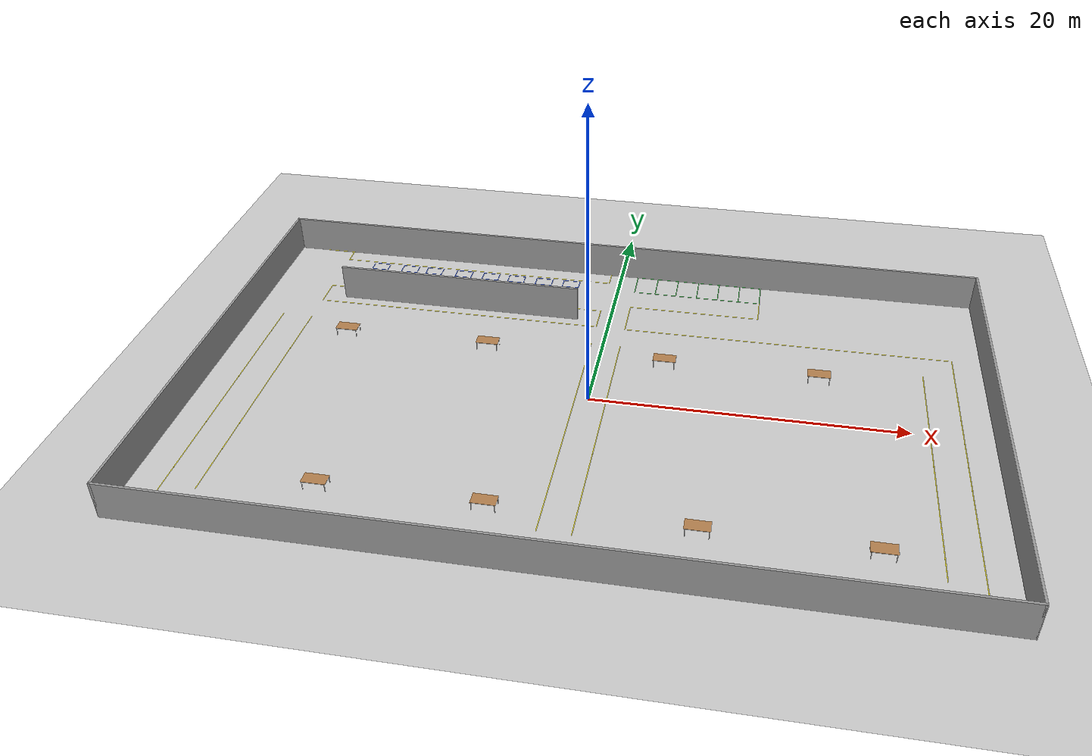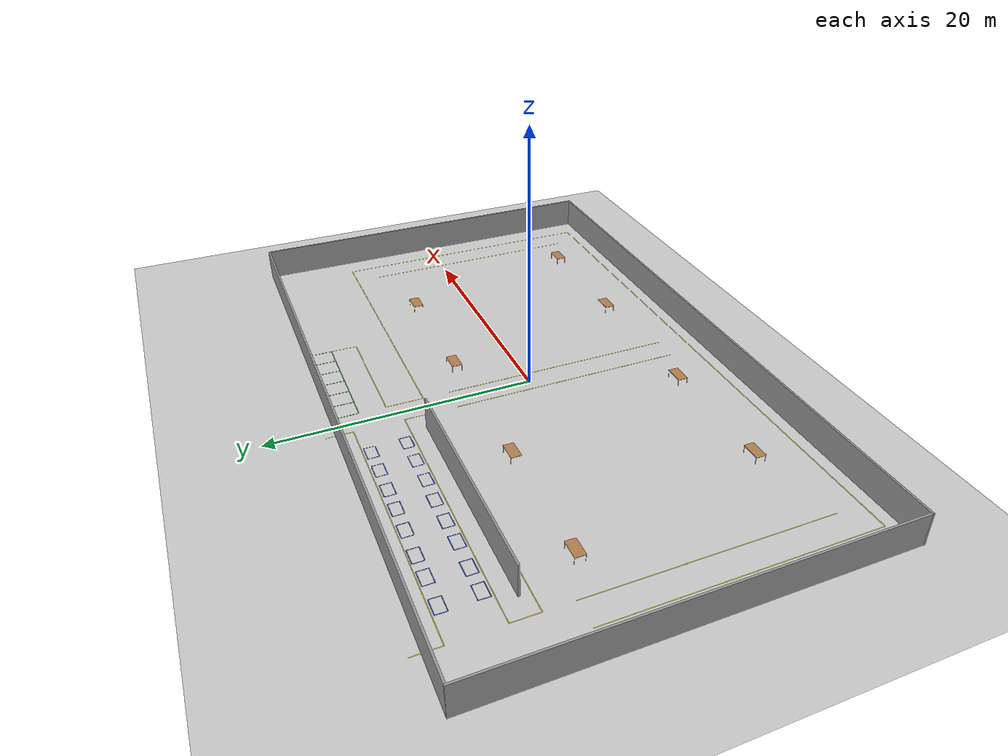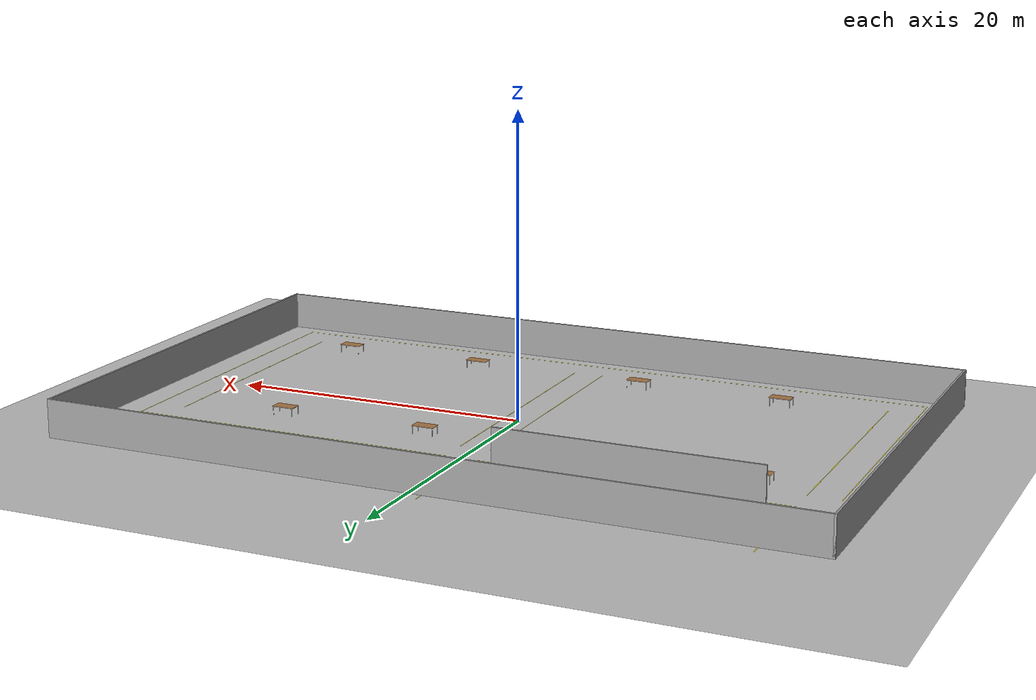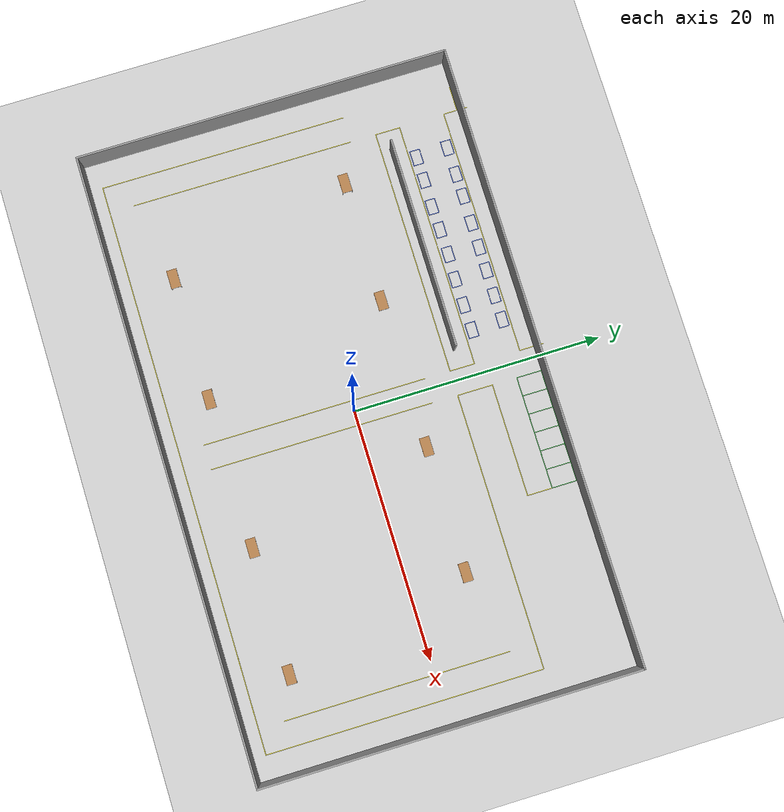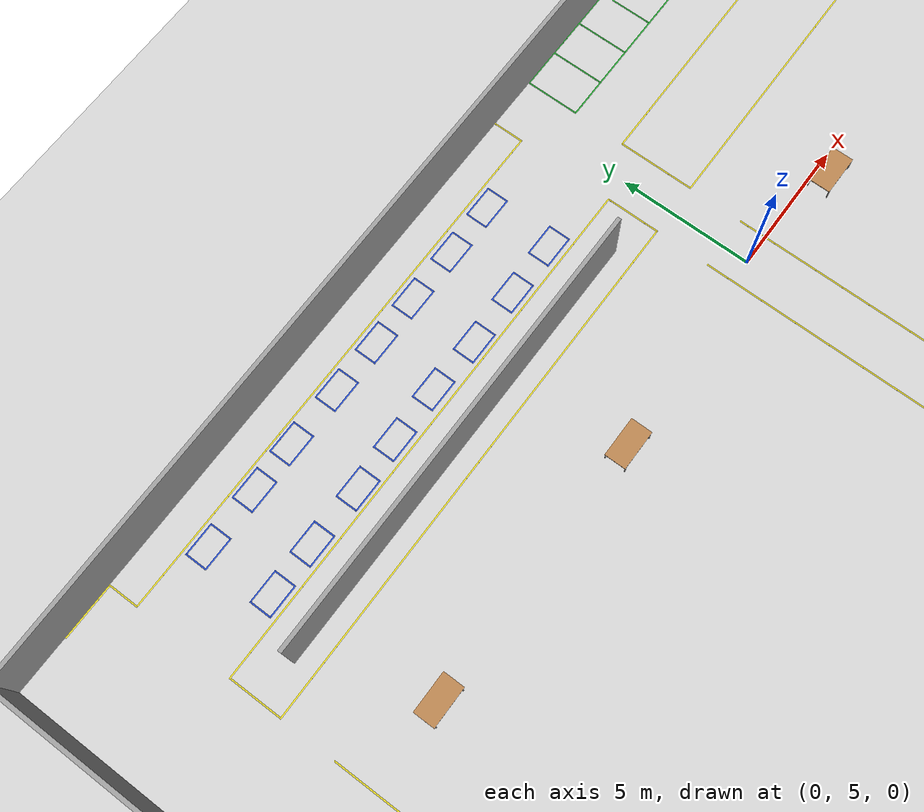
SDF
<sdf version="1.6">
 <world name="default">
  <light name="sun" type="directional">
   <pose>0 0 10 0 -0 0</pose>
   <diffuse>0.8 0.8 0.8 1</diffuse>
   <specular>0.2 0.2 0.2 1</specular>
   <attenuation>
    <range>1000</range>
    <constant>0.9</constant>
    <linear>0.01</linear>
    <quadratic>0.001</quadratic>
   </attenuation>
   <direction>-0.5 0.1 -0.9</direction>
  </light>
  <model name="ground_plane">
   <static>1</static>
   <link name="link">
    <collision name="collision">
     <geometry><plane><normal>0 0 1</normal><size>100 100</size></plane></geometry>
     <surface><friction><ode><mu>100</mu><mu2>50</mu2></ode></friction></surface>
    </collision>
    <visual name="visual">
     <cast_shadows>0</cast_shadows>
     <geometry><plane><normal>0 0 1</normal><size>100 100</size></plane></geometry>
     <material>
      <script><uri>file://media/materials/scripts/gazebo.material</uri><name>Gazebo/Grey</name></script>
     </material>
    </visual>
   </link>
  </model>
  <gravity>0 0 -9.8</gravity>
  <magnetic_field>6e-06 2.3e-05 -4.2e-05</magnetic_field>
  <atmosphere type="adiabatic"/>
  <physics name="default_physics" default="0" type="ode">
   <max_step_size>0.001</max_step_size>
   <real_time_factor>1</real_time_factor>
   <real_time_update_rate>1000</real_time_update_rate>
  </physics>
  <scene><ambient>0.4 0.4 0.4 1</ambient><background>0.7 0.7 0.7 1</background><shadows>1</shadows></scene>
  <spherical_coordinates>
   <surface_model>EARTH_WGS84</surface_model>
   <latitude_deg>0</latitude_deg>
   <longitude_deg>0</longitude_deg>
   <elevation>0</elevation>
   <heading_deg>0</heading_deg>
  </spherical_coordinates>
  <model name="factoryWall">
   <link name="Wall_0">
    <collision name="Wall_0_Collision">
     <geometry><box><size>30.15 0.15 2.5</size></box></geometry>
     <pose>0 0 1.25 0 -0 0</pose>
    </collision>
    <visual name="Wall_0_Visual">
     <pose>0 0 1.25 0 -0 0</pose>
     <geometry><box><size>30.15 0.15 2.5</size></box></geometry>
     <material>
      <script><uri>file://media/materials/scripts/gazebo.material</uri><name>Gazebo/Grey</name></script>
      <ambient>1 1 1 1</ambient>
     </material>
     <meta><layer>0</layer></meta>
    </visual>
    <pose>25 0 0 0 -0 1.5708</pose>
   </link>
   <link name="Wall_2">
    <collision name="Wall_2_Collision">
     <geometry><box><size>30.15 0.15 2.5</size></box></geometry>
     <pose>0 0 1.25 0 -0 0</pose>
    </collision>
    <visual name="Wall_2_Visual">
     <pose>0 0 1.25 0 -0 0</pose>
     <geometry><box><size>30.15 0.15 2.5</size></box></geometry>
     <material>
      <script><uri>file://media/materials/scripts/gazebo.material</uri><name>Gazebo/Grey</name></script>
      <ambient>1 1 1 1</ambient>
     </material>
     <meta><layer>0</layer></meta>
    </visual>
    <pose>-25 0 0 0 -0 1.5708</pose>
   </link>
   <link name="Wall_4">
    <collision name="Wall_4_Collision">
     <geometry><box><size>50.15 0.15 2.5</size></box></geometry>
     <pose>0 0 1.25 0 -0 0</pose>
    </collision>
    <visual name="Wall_4_Visual">
     <pose>0 0 1.25 0 -0 0</pose>
     <geometry><box><size>50.15 0.15 2.5</size></box></geometry>
     <material>
      <script><uri>file://media/materials/scripts/gazebo.material</uri><name>Gazebo/Grey</name></script>
      <ambient>1 1 1 1</ambient>
     </material>
     <meta><layer>0</layer></meta>
    </visual>
    <pose>0 15 0 0 -0 0</pose>
   </link>
   <link name="Wall_6">
    <collision name="Wall_6_Collision">
     <geometry><box><size>50.15 0.15 2.5</size></box></geometry>
     <pose>0 0 1.25 0 -0 0</pose>
    </collision>
    <visual name="Wall_6_Visual">
     <pose>0 0 1.25 0 -0 0</pose>
     <geometry><box><size>50.15 0.15 2.5</size></box></geometry>
     <material>
      <script><uri>file://media/materials/scripts/gazebo.material</uri><name>Gazebo/Grey</name></script>
      <ambient>1 1 1 1</ambient>
     </material>
     <meta><layer>0</layer></meta>
    </visual>
    <pose>0 -15 0 0 -0 0</pose>
   </link>
   <static>1</static>
  </model>
  <model name="factoryWall_1">
   <pose>-10.8 8.85 0 0 -0 1.570796</pose>
   <link name="Wall_0">
    <collision name="Wall1_0_Collision">
     <geometry><box><size>17 0.15 2.5</size></box></geometry>
     <pose>0 0 1.25 0 -0 0</pose>
    </collision>
    <visual name="Wall1_0_Visual">
     <pose>0 0 1.25 0 -0 0</pose>
     <geometry><box><size>17 0.15 2.5</size></box></geometry>
     <material>
      <script><uri>file://media/materials/scripts/gazebo.material</uri><name>Gazebo/Grey</name></script>
      <ambient>1 1 1 1</ambient>
     </material>
     <meta><layer>0</layer></meta>
    </visual>
    <pose>0 0 0 0 -0 1.570796</pose>
   </link>
   <static>1</static>
  </model>
  <model name="line20m">
   <link name="link_0">
    <inertial>
     <mass>1</mass>
     <inertia>
      <ixx>0.166667</ixx>
      <ixy>0</ixy>
      <ixz>0</ixz>
      <iyy>0.166667</iyy>
      <iyz>0</iyz>
      <izz>0.166667</izz>
     </inertia>
    </inertial>
    <visual name="visual">
     <geometry><box><size>0.05 20 0.001</size></box></geometry>
     <material>
      <lighting>1</lighting>
      <script><uri>file://media/materials/scripts/gazebo.material</uri><name>Gazebo/Yellow</name></script>
     </material>
    </visual>
    <collision name="collision">
     <geometry><box><size>0.05 20 0.001</size></box></geometry>
     <surface>
      <friction>
       <ode><mu>1</mu><mu2>1</mu2><fdir1>0 0 0</fdir1><slip1>0</slip1><slip2>0</slip2></ode>
       <torsional>
        <coefficient>1</coefficient>
        <patch_radius>0</patch_radius>
        <surface_radius>0</surface_radius>
        <use_patch_radius>1</use_patch_radius>
        <ode><slip>0</slip></ode>
       </torsional>
      </friction>
      <bounce><restitution_coefficient>0</restitution_coefficient><threshold>1e+06</threshold></bounce>
      <contact>
       <collide_without_contact>0</collide_without_contact>
       <collide_without_contact_bitmask>1</collide_without_contact_bitmask>
       <collide_bitmask>1</collide_bitmask>
       <ode>
        <soft_cfm>0</soft_cfm>
        <soft_erp>0.2</soft_erp>
        <kp>1e+13</kp>
        <kd>1</kd>
        <max_vel>0.01</max_vel>
        <min_depth>0</min_depth>
       </ode>
       <bullet>
        <split_impulse>1</split_impulse>
        <split_impulse_penetration_threshold>-0.01</split_impulse_penetration_threshold>
        <soft_cfm>0</soft_cfm>
        <soft_erp>0.2</soft_erp>
        <kp>1e+13</kp>
        <kd>1</kd>
       </bullet>
      </contact>
     </surface>
    </collision>
   </link>
   <static>1</static>
   <pose>-22.9002 -3.99821 0 0 -0 0</pose>
  </model>
  <model name="line2m">
   <link name="link_0">
    <inertial>
     <mass>1</mass>
     <inertia>
      <ixx>0.166667</ixx>
      <ixy>0</ixy>
      <ixz>0</ixz>
      <iyy>0.166667</iyy>
      <iyz>0</iyz>
      <izz>0.166667</izz>
     </inertia>
    </inertial>
    <visual name="visual">
     <geometry><box><size>2 0.05 0.001</size></box></geometry>
     <material>
      <lighting>1</lighting>
      <script><uri>file://media/materials/scripts/gazebo.material</uri><name>Gazebo/Yellow</name></script>
     </material>
    </visual>
    <collision name="collision">
     <geometry><box><size>2 0.05 0.001</size></box></geometry>
     <surface>
      <friction>
       <ode><mu>1</mu><mu2>1</mu2><fdir1>0 0 0</fdir1><slip1>0</slip1><slip2>0</slip2></ode>
       <torsional>
        <coefficient>1</coefficient>
        <patch_radius>0</patch_radius>
        <surface_radius>0</surface_radius>
        <use_patch_radius>1</use_patch_radius>
        <ode><slip>0</slip></ode>
       </torsional>
      </friction>
      <bounce><restitution_coefficient>0</restitution_coefficient><threshold>1e+06</threshold></bounce>
      <contact>
       <collide_without_contact>0</collide_without_contact>
       <collide_without_contact_bitmask>1</collide_without_contact_bitmask>
       <collide_bitmask>1</collide_bitmask>
       <ode>
        <soft_cfm>0</soft_cfm>
        <soft_erp>0.2</soft_erp>
        <kp>1e+13</kp>
        <kd>1</kd>
        <max_vel>0.01</max_vel>
        <min_depth>0</min_depth>
       </ode>
       <bullet>
        <split_impulse>1</split_impulse>
        <split_impulse_penetration_threshold>-0.01</split_impulse_penetration_threshold>
        <soft_cfm>0</soft_cfm>
        <soft_erp>0.2</soft_erp>
        <kp>1e+13</kp>
        <kd>1</kd>
       </bullet>
      </contact>
     </surface>
    </collision>
   </link>
   <static>1</static>
   <pose>-21.8772 14.9028 0 0 -0 0</pose>
  </model>
  <model name="line2m_0">
   <link name="link_0">
    <inertial>
     <mass>1</mass>
     <inertia>
      <ixx>0.166667</ixx>
      <ixy>0</ixy>
      <ixz>0</ixz>
      <iyy>0.166667</iyy>
      <iyz>0</iyz>
      <izz>0.166667</izz>
     </inertia>
    </inertial>
    <visual name="visual">
     <geometry><box><size>2 0.05 0.001</size></box></geometry>
     <material>
      <lighting>1</lighting>
      <script><uri>file://media/materials/scripts/gazebo.material</uri><name>Gazebo/Yellow</name></script>
     </material>
    </visual>
    <collision name="collision">
     <geometry><box><size>2 0.05 0.001</size></box></geometry>
     <surface>
      <friction>
       <ode><mu>1</mu><mu2>1</mu2><fdir1>0 0 0</fdir1><slip1>0</slip1><slip2>0</slip2></ode>
       <torsional>
        <coefficient>1</coefficient>
        <patch_radius>0</patch_radius>
        <surface_radius>0</surface_radius>
        <use_patch_radius>1</use_patch_radius>
        <ode><slip>0</slip></ode>
       </torsional>
      </friction>
      <bounce><restitution_coefficient>0</restitution_coefficient><threshold>1e+06</threshold></bounce>
      <contact>
       <collide_without_contact>0</collide_without_contact>
       <collide_without_contact_bitmask>1</collide_without_contact_bitmask>
       <collide_bitmask>1</collide_bitmask>
       <ode>
        <soft_cfm>0</soft_cfm>
        <soft_erp>0.2</soft_erp>
        <kp>1e+13</kp>
        <kd>1</kd>
        <max_vel>0.01</max_vel>
        <min_depth>0</min_depth>
       </ode>
       <bullet>
        <split_impulse>1</split_impulse>
        <split_impulse_penetration_threshold>-0.01</split_impulse_penetration_threshold>
        <soft_cfm>0</soft_cfm>
        <soft_erp>0.2</soft_erp>
        <kp>1e+13</kp>
        <kd>1</kd>
       </bullet>
      </contact>
     </surface>
    </collision>
   </link>
   <static>1</static>
   <pose>-20.8518 14.7675 0 0 -0 1.5708</pose>
  </model>
  <model name="line20m_0">
   <link name="link_0">
    <inertial>
     <mass>1</mass>
     <inertia>
      <ixx>0.166667</ixx>
      <ixy>0</ixy>
      <ixz>0</ixz>
      <iyy>0.166667</iyy>
      <iyz>0</iyz>
      <izz>0.166667</izz>
     </inertia>
    </inertial>
    <visual name="visual">
     <geometry><box><size>0.05 20 0.001</size></box></geometry>
     <material>
      <lighting>1</lighting>
      <script><uri>file://media/materials/scripts/gazebo.material</uri><name>Gazebo/Yellow</name></script>
     </material>
    </visual>
    <collision name="collision">
     <geometry><box><size>0.05 20 0.001</size></box></geometry>
     <surface>
      <friction>
       <ode><mu>1</mu><mu2>1</mu2><fdir1>0 0 0</fdir1><slip1>0</slip1><slip2>0</slip2></ode>
       <torsional>
        <coefficient>1</coefficient>
        <patch_radius>0</patch_radius>
        <surface_radius>0</surface_radius>
        <use_patch_radius>1</use_patch_radius>
        <ode><slip>0</slip></ode>
       </torsional>
      </friction>
      <bounce><restitution_coefficient>0</restitution_coefficient><threshold>1e+06</threshold></bounce>
      <contact>
       <collide_without_contact>0</collide_without_contact>
       <collide_without_contact_bitmask>1</collide_without_contact_bitmask>
       <collide_bitmask>1</collide_bitmask>
       <ode>
        <soft_cfm>0</soft_cfm>
        <soft_erp>0.2</soft_erp>
        <kp>1e+13</kp>
        <kd>1</kd>
        <max_vel>0.01</max_vel>
        <min_depth>0</min_depth>
       </ode>
       <bullet>
        <split_impulse>1</split_impulse>
        <split_impulse_penetration_threshold>-0.01</split_impulse_penetration_threshold>
        <soft_cfm>0</soft_cfm>
        <soft_erp>0.2</soft_erp>
        <kp>1e+13</kp>
        <kd>1</kd>
       </bullet>
      </contact>
     </surface>
    </collision>
   </link>
   <static>1</static>
   <pose>-10.8441 13.7915 0 0 -0 1.5708</pose>
  </model>
  <model name="line2m_1">
   <link name="link_0">
    <inertial>
     <mass>1</mass>
     <inertia>
      <ixx>0.166667</ixx>
      <ixy>0</ixy>
      <ixz>0</ixz>
      <iyy>0.166667</iyy>
      <iyz>0</iyz>
      <izz>0.166667</izz>
     </inertia>
    </inertial>
    <visual name="visual">
     <geometry><box><size>2 0.05 0.001</size></box></geometry>
     <material>
      <lighting>1</lighting>
      <script><uri>file://media/materials/scripts/gazebo.material</uri><name>Gazebo/Yellow</name></script>
     </material>
    </visual>
    <collision name="collision">
     <geometry><box><size>2 0.05 0.001</size></box></geometry>
     <surface>
      <friction>
       <ode><mu>1</mu><mu2>1</mu2><fdir1>0 0 0</fdir1><slip1>0</slip1><slip2>0</slip2></ode>
       <torsional>
        <coefficient>1</coefficient>
        <patch_radius>0</patch_radius>
        <surface_radius>0</surface_radius>
        <use_patch_radius>1</use_patch_radius>
        <ode><slip>0</slip></ode>
       </torsional>
      </friction>
      <bounce><restitution_coefficient>0</restitution_coefficient><threshold>1e+06</threshold></bounce>
      <contact>
       <collide_without_contact>0</collide_without_contact>
       <collide_without_contact_bitmask>1</collide_without_contact_bitmask>
       <collide_bitmask>1</collide_bitmask>
       <ode>
        <soft_cfm>0</soft_cfm>
        <soft_erp>0.2</soft_erp>
        <kp>1e+13</kp>
        <kd>1</kd>
        <max_vel>0.01</max_vel>
        <min_depth>0</min_depth>
       </ode>
       <bullet>
        <split_impulse>1</split_impulse>
        <split_impulse_penetration_threshold>-0.01</split_impulse_penetration_threshold>
        <soft_cfm>0</soft_cfm>
        <soft_erp>0.2</soft_erp>
        <kp>1e+13</kp>
        <kd>1</kd>
       </bullet>
      </contact>
     </surface>
    </collision>
   </link>
   <static>1</static>
   <pose>-0.829144 14.7665 0 0 -0 1.5708</pose>
  </model>
  <model name="line20m_1">
   <link name="link_0">
    <inertial>
     <mass>1</mass>
     <inertia>
      <ixx>0.166667</ixx>
      <ixy>0</ixy>
      <ixz>0</ixz>
      <iyy>0.166667</iyy>
      <iyz>0</iyz>
      <izz>0.166667</izz>
     </inertia>
    </inertial>
    <visual name="visual">
     <geometry><box><size>0.05 20 0.001</size></box></geometry>
     <material>
      <lighting>1</lighting>
      <script><uri>file://media/materials/scripts/gazebo.material</uri><name>Gazebo/Yellow</name></script>
     </material>
    </visual>
    <collision name="collision">
     <geometry><box><size>0.05 20 0.001</size></box></geometry>
     <surface>
      <friction>
       <ode><mu>1</mu><mu2>1</mu2><fdir1>0 0 0</fdir1><slip1>0</slip1><slip2>0</slip2></ode>
       <torsional>
        <coefficient>1</coefficient>
        <patch_radius>0</patch_radius>
        <surface_radius>0</surface_radius>
        <use_patch_radius>1</use_patch_radius>
        <ode><slip>0</slip></ode>
       </torsional>
      </friction>
      <bounce><restitution_coefficient>0</restitution_coefficient><threshold>1e+06</threshold></bounce>
      <contact>
       <collide_without_contact>0</collide_without_contact>
       <collide_without_contact_bitmask>1</collide_without_contact_bitmask>
       <collide_bitmask>1</collide_bitmask>
       <ode>
        <soft_cfm>0</soft_cfm>
        <soft_erp>0.2</soft_erp>
        <kp>1e+13</kp>
        <kd>1</kd>
        <max_vel>0.01</max_vel>
        <min_depth>0</min_depth>
       </ode>
       <bullet>
        <split_impulse>1</split_impulse>
        <split_impulse_penetration_threshold>-0.01</split_impulse_penetration_threshold>
        <soft_cfm>0</soft_cfm>
        <soft_erp>0.2</soft_erp>
        <kp>1e+13</kp>
        <kd>1</kd>
       </bullet>
      </contact>
     </surface>
    </collision>
   </link>
   <static>1</static>
   <pose>-10.83 10.0802 0 0 -0 1.5708</pose>
  </model>
  <model name="line2m_2">
   <link name="link_0">
    <inertial>
     <mass>1</mass>
     <inertia>
      <ixx>0.166667</ixx>
      <ixy>0</ixy>
      <ixz>0</ixz>
      <iyy>0.166667</iyy>
      <iyz>0</iyz>
      <izz>0.166667</izz>
     </inertia>
    </inertial>
    <visual name="visual">
     <geometry><box><size>2 0.05 0.001</size></box></geometry>
     <material>
      <lighting>1</lighting>
      <script><uri>file://media/materials/scripts/gazebo.material</uri><name>Gazebo/Yellow</name></script>
     </material>
    </visual>
    <collision name="collision">
     <geometry><box><size>2 0.05 0.001</size></box></geometry>
     <surface>
      <friction>
       <ode><mu>1</mu><mu2>1</mu2><fdir1>0 0 0</fdir1><slip1>0</slip1><slip2>0</slip2></ode>
       <torsional>
        <coefficient>1</coefficient>
        <patch_radius>0</patch_radius>
        <surface_radius>0</surface_radius>
        <use_patch_radius>1</use_patch_radius>
        <ode><slip>0</slip></ode>
       </torsional>
      </friction>
      <bounce><restitution_coefficient>0</restitution_coefficient><threshold>1e+06</threshold></bounce>
      <contact>
       <collide_without_contact>0</collide_without_contact>
       <collide_without_contact_bitmask>1</collide_without_contact_bitmask>
       <collide_bitmask>1</collide_bitmask>
       <ode>
        <soft_cfm>0</soft_cfm>
        <soft_erp>0.2</soft_erp>
        <kp>1e+13</kp>
        <kd>1</kd>
        <max_vel>0.01</max_vel>
        <min_depth>0</min_depth>
       </ode>
       <bullet>
        <split_impulse>1</split_impulse>
        <split_impulse_penetration_threshold>-0.01</split_impulse_penetration_threshold>
        <soft_cfm>0</soft_cfm>
        <soft_erp>0.2</soft_erp>
        <kp>1e+13</kp>
        <kd>1</kd>
       </bullet>
      </contact>
     </surface>
    </collision>
   </link>
   <static>1</static>
   <pose>-20.805 9.06119 0 0 -0 1.5708</pose>
  </model>
  <model name="line20m_2">
   <link name="link_0">
    <inertial>
     <mass>1</mass>
     <inertia>
      <ixx>0.166667</ixx>
      <ixy>0</ixy>
      <ixz>0</ixz>
      <iyy>0.166667</iyy>
      <iyz>0</iyz>
      <izz>0.166667</izz>
     </inertia>
    </inertial>
    <visual name="visual">
     <geometry><box><size>0.05 20 0.001</size></box></geometry>
     <material>
      <lighting>1</lighting>
      <script><uri>file://media/materials/scripts/gazebo.material</uri><name>Gazebo/Yellow</name></script>
     </material>
    </visual>
    <collision name="collision">
     <geometry><box><size>0.05 20 0.001</size></box></geometry>
     <surface>
      <friction>
       <ode><mu>1</mu><mu2>1</mu2><fdir1>0 0 0</fdir1><slip1>0</slip1><slip2>0</slip2></ode>
       <torsional>
        <coefficient>1</coefficient>
        <patch_radius>0</patch_radius>
        <surface_radius>0</surface_radius>
        <use_patch_radius>1</use_patch_radius>
        <ode><slip>0</slip></ode>
       </torsional>
      </friction>
      <bounce><restitution_coefficient>0</restitution_coefficient><threshold>1e+06</threshold></bounce>
      <contact>
       <collide_without_contact>0</collide_without_contact>
       <collide_without_contact_bitmask>1</collide_without_contact_bitmask>
       <collide_bitmask>1</collide_bitmask>
       <ode>
        <soft_cfm>0</soft_cfm>
        <soft_erp>0.2</soft_erp>
        <kp>1e+13</kp>
        <kd>1</kd>
        <max_vel>0.01</max_vel>
        <min_depth>0</min_depth>
       </ode>
       <bullet>
        <split_impulse>1</split_impulse>
        <split_impulse_penetration_threshold>-0.01</split_impulse_penetration_threshold>
        <soft_cfm>0</soft_cfm>
        <soft_erp>0.2</soft_erp>
        <kp>1e+13</kp>
        <kd>1</kd>
       </bullet>
      </contact>
     </surface>
    </collision>
   </link>
   <static>1</static>
   <pose>-10.83 8.0802 0 0 -0 1.5708</pose>
  </model>
  <model name="line2m_3">
   <link name="link_0">
    <inertial>
     <mass>1</mass>
     <inertia>
      <ixx>0.166667</ixx>
      <ixy>0</ixy>
      <ixz>0</ixz>
      <iyy>0.166667</iyy>
      <iyz>0</iyz>
      <izz>0.166667</izz>
     </inertia>
    </inertial>
    <visual name="visual">
     <geometry><box><size>2 0.05 0.001</size></box></geometry>
     <material>
      <lighting>1</lighting>
      <script><uri>file://media/materials/scripts/gazebo.material</uri><name>Gazebo/Yellow</name></script>
     </material>
    </visual>
    <collision name="collision">
     <geometry><box><size>2 0.05 0.001</size></box></geometry>
     <surface>
      <friction>
       <ode><mu>1</mu><mu2>1</mu2><fdir1>0 0 0</fdir1><slip1>0</slip1><slip2>0</slip2></ode>
       <torsional>
        <coefficient>1</coefficient>
        <patch_radius>0</patch_radius>
        <surface_radius>0</surface_radius>
        <use_patch_radius>1</use_patch_radius>
        <ode><slip>0</slip></ode>
       </torsional>
      </friction>
      <bounce><restitution_coefficient>0</restitution_coefficient><threshold>1e+06</threshold></bounce>
      <contact>
       <collide_without_contact>0</collide_without_contact>
       <collide_without_contact_bitmask>1</collide_without_contact_bitmask>
       <collide_bitmask>1</collide_bitmask>
       <ode>
        <soft_cfm>0</soft_cfm>
        <soft_erp>0.2</soft_erp>
        <kp>1e+13</kp>
        <kd>1</kd>
        <max_vel>0.01</max_vel>
        <min_depth>0</min_depth>
       </ode>
       <bullet>
        <split_impulse>1</split_impulse>
        <split_impulse_penetration_threshold>-0.01</split_impulse_penetration_threshold>
        <soft_cfm>0</soft_cfm>
        <soft_erp>0.2</soft_erp>
        <kp>1e+13</kp>
        <kd>1</kd>
       </bullet>
      </contact>
     </surface>
    </collision>
   </link>
   <static>1</static>
   <pose>-0.854942 9.06995 0 0 -0 1.5708</pose>
  </model>
  <model name="line18m">
   <link name="link_1">
    <inertial>
     <mass>1</mass>
     <inertia>
      <ixx>0.166667</ixx>
      <ixy>0</ixy>
      <ixz>0</ixz>
      <iyy>0.166667</iyy>
      <iyz>0</iyz>
      <izz>0.166667</izz>
     </inertia>
    </inertial>
    <visual name="visual">
     <geometry><box><size>0.05 18 0.001</size></box></geometry>
     <material>
      <lighting>1</lighting>
      <script><uri>file://media/materials/scripts/gazebo.material</uri><name>Gazebo/Yellow</name></script>
     </material>
    </visual>
    <collision name="collision">
     <geometry><box><size>0.05 18 0.001</size></box></geometry>
     <surface>
      <friction>
       <ode><mu>1</mu><mu2>1</mu2><fdir1>0 0 0</fdir1><slip1>0</slip1><slip2>0</slip2></ode>
       <torsional>
        <coefficient>1</coefficient>
        <patch_radius>0</patch_radius>
        <surface_radius>0</surface_radius>
        <use_patch_radius>1</use_patch_radius>
        <ode><slip>0</slip></ode>
       </torsional>
      </friction>
      <bounce><restitution_coefficient>0</restitution_coefficient><threshold>1e+06</threshold></bounce>
      <contact>
       <collide_without_contact>0</collide_without_contact>
       <collide_without_contact_bitmask>1</collide_without_contact_bitmask>
       <collide_bitmask>1</collide_bitmask>
       <ode>
        <soft_cfm>0</soft_cfm>
        <soft_erp>0.2</soft_erp>
        <kp>1e+13</kp>
        <kd>1</kd>
        <max_vel>0.01</max_vel>
        <min_depth>0</min_depth>
       </ode>
       <bullet>
        <split_impulse>1</split_impulse>
        <split_impulse_penetration_threshold>-0.01</split_impulse_penetration_threshold>
        <soft_cfm>0</soft_cfm>
        <soft_erp>0.2</soft_erp>
        <kp>1e+13</kp>
        <kd>1</kd>
       </bullet>
      </contact>
     </surface>
    </collision>
   </link>
   <static>1</static>
   <pose>-20.8079 -2.99039 0 0 -0 0</pose>
  </model>
  <model name="line18m_0">
   <link name="link_1">
    <inertial>
     <mass>1</mass>
     <inertia>
      <ixx>0.166667</ixx>
      <ixy>0</ixy>
      <ixz>0</ixz>
      <iyy>0.166667</iyy>
      <iyz>0</iyz>
      <izz>0.166667</izz>
     </inertia>
    </inertial>
    <visual name="visual">
     <geometry><box><size>0.05 18 0.001</size></box></geometry>
     <material>
      <lighting>1</lighting>
      <script><uri>file://media/materials/scripts/gazebo.material</uri><name>Gazebo/Yellow</name></script>
     </material>
    </visual>
    <collision name="collision">
     <geometry><box><size>0.05 18 0.001</size></box></geometry>
     <surface>
      <friction>
       <ode><mu>1</mu><mu2>1</mu2><fdir1>0 0 0</fdir1><slip1>0</slip1><slip2>0</slip2></ode>
       <torsional>
        <coefficient>1</coefficient>
        <patch_radius>0</patch_radius>
        <surface_radius>0</surface_radius>
        <use_patch_radius>1</use_patch_radius>
        <ode><slip>0</slip></ode>
       </torsional>
      </friction>
      <bounce><restitution_coefficient>0</restitution_coefficient><threshold>1e+06</threshold></bounce>
      <contact>
       <collide_without_contact>0</collide_without_contact>
       <collide_without_contact_bitmask>1</collide_without_contact_bitmask>
       <collide_bitmask>1</collide_bitmask>
       <ode>
        <soft_cfm>0</soft_cfm>
        <soft_erp>0.2</soft_erp>
        <kp>1e+13</kp>
        <kd>1</kd>
        <max_vel>0.01</max_vel>
        <min_depth>0</min_depth>
       </ode>
       <bullet>
        <split_impulse>1</split_impulse>
        <split_impulse_penetration_threshold>-0.01</split_impulse_penetration_threshold>
        <soft_cfm>0</soft_cfm>
        <soft_erp>0.2</soft_erp>
        <kp>1e+13</kp>
        <kd>1</kd>
       </bullet>
      </contact>
     </surface>
    </collision>
   </link>
   <static>1</static>
   <pose>-0.857987 -2.97176 0 0 -0 0</pose>
  </model>
  <model name="line18m_1">
   <link name="link_1">
    <inertial>
     <mass>1</mass>
     <inertia>
      <ixx>0.166667</ixx>
      <ixy>0</ixy>
      <ixz>0</ixz>
      <iyy>0.166667</iyy>
      <iyz>0</iyz>
      <izz>0.166667</izz>
     </inertia>
    </inertial>
    <visual name="visual">
     <geometry><box><size>0.05 18 0.001</size></box></geometry>
     <material>
      <lighting>1</lighting>
      <script><uri>file://media/materials/scripts/gazebo.material</uri><name>Gazebo/Yellow</name></script>
     </material>
    </visual>
    <collision name="collision">
     <geometry><box><size>0.05 18 0.001</size></box></geometry>
     <surface>
      <friction>
       <ode><mu>1</mu><mu2>1</mu2><fdir1>0 0 0</fdir1><slip1>0</slip1><slip2>0</slip2></ode>
       <torsional>
        <coefficient>1</coefficient>
        <patch_radius>0</patch_radius>
        <surface_radius>0</surface_radius>
        <use_patch_radius>1</use_patch_radius>
        <ode><slip>0</slip></ode>
       </torsional>
      </friction>
      <bounce><restitution_coefficient>0</restitution_coefficient><threshold>1e+06</threshold></bounce>
      <contact>
       <collide_without_contact>0</collide_without_contact>
       <collide_without_contact_bitmask>1</collide_without_contact_bitmask>
       <collide_bitmask>1</collide_bitmask>
       <ode>
        <soft_cfm>0</soft_cfm>
        <soft_erp>0.2</soft_erp>
        <kp>1e+13</kp>
        <kd>1</kd>
        <max_vel>0.01</max_vel>
        <min_depth>0</min_depth>
       </ode>
       <bullet>
        <split_impulse>1</split_impulse>
        <split_impulse_penetration_threshold>-0.01</split_impulse_penetration_threshold>
        <soft_cfm>0</soft_cfm>
        <soft_erp>0.2</soft_erp>
        <kp>1e+13</kp>
        <kd>1</kd>
       </bullet>
      </contact>
     </surface>
    </collision>
   </link>
   <static>1</static>
   <pose>1.13446 -2.97176 0 0 -0 0</pose>
  </model>
  <model name="line18m_2">
   <link name="link_1">
    <inertial>
     <mass>1</mass>
     <inertia>
      <ixx>0.166667</ixx>
      <ixy>0</ixy>
      <ixz>0</ixz>
      <iyy>0.166667</iyy>
      <iyz>0</iyz>
      <izz>0.166667</izz>
     </inertia>
    </inertial>
    <visual name="visual">
     <geometry><box><size>0.05 18 0.001</size></box></geometry>
     <material>
      <lighting>1</lighting>
      <script><uri>file://media/materials/scripts/gazebo.material</uri><name>Gazebo/Yellow</name></script>
     </material>
    </visual>
    <collision name="collision">
     <geometry><box><size>0.05 18 0.001</size></box></geometry>
     <surface>
      <friction>
       <ode><mu>1</mu><mu2>1</mu2><fdir1>0 0 0</fdir1><slip1>0</slip1><slip2>0</slip2></ode>
       <torsional>
        <coefficient>1</coefficient>
        <patch_radius>0</patch_radius>
        <surface_radius>0</surface_radius>
        <use_patch_radius>1</use_patch_radius>
        <ode><slip>0</slip></ode>
       </torsional>
      </friction>
      <bounce><restitution_coefficient>0</restitution_coefficient><threshold>1e+06</threshold></bounce>
      <contact>
       <collide_without_contact>0</collide_without_contact>
       <collide_without_contact_bitmask>1</collide_without_contact_bitmask>
       <collide_bitmask>1</collide_bitmask>
       <ode>
        <soft_cfm>0</soft_cfm>
        <soft_erp>0.2</soft_erp>
        <kp>1e+13</kp>
        <kd>1</kd>
        <max_vel>0.01</max_vel>
        <min_depth>0</min_depth>
       </ode>
       <bullet>
        <split_impulse>1</split_impulse>
        <split_impulse_penetration_threshold>-0.01</split_impulse_penetration_threshold>
        <soft_cfm>0</soft_cfm>
        <soft_erp>0.2</soft_erp>
        <kp>1e+13</kp>
        <kd>1</kd>
       </bullet>
      </contact>
     </surface>
    </collision>
   </link>
   <static>1</static>
   <pose>21.0899 -2.96828 0 0 -0 0</pose>
  </model>
  <model name="line22m">
   <link name="link_2">
    <inertial>
     <mass>1</mass>
     <inertia>
      <ixx>0.166667</ixx>
      <ixy>0</ixy>
      <ixz>0</ixz>
      <iyy>0.166667</iyy>
      <iyz>0</iyz>
      <izz>0.166667</izz>
     </inertia>
    </inertial>
    <visual name="visual">
     <geometry><box><size>0.05 22 0.001</size></box></geometry>
     <material>
      <lighting>1</lighting>
      <script><uri>file://media/materials/scripts/gazebo.material</uri><name>Gazebo/Yellow</name></script>
     </material>
    </visual>
    <collision name="collision">
     <geometry><box><size>0.05 22 0.001</size></box></geometry>
     <surface>
      <friction>
       <ode><mu>1</mu><mu2>1</mu2><fdir1>0 0 0</fdir1><slip1>0</slip1><slip2>0</slip2></ode>
       <torsional>
        <coefficient>1</coefficient>
        <patch_radius>0</patch_radius>
        <surface_radius>0</surface_radius>
        <use_patch_radius>1</use_patch_radius>
        <ode><slip>0</slip></ode>
       </torsional>
      </friction>
      <bounce><restitution_coefficient>0</restitution_coefficient><threshold>1e+06</threshold></bounce>
      <contact>
       <collide_without_contact>0</collide_without_contact>
       <collide_without_contact_bitmask>1</collide_without_contact_bitmask>
       <collide_bitmask>1</collide_bitmask>
       <ode>
        <soft_cfm>0</soft_cfm>
        <soft_erp>0.2</soft_erp>
        <kp>1e+13</kp>
        <kd>1</kd>
        <max_vel>0.01</max_vel>
        <min_depth>0</min_depth>
       </ode>
       <bullet>
        <split_impulse>1</split_impulse>
        <split_impulse_penetration_threshold>-0.01</split_impulse_penetration_threshold>
        <soft_cfm>0</soft_cfm>
        <soft_erp>0.2</soft_erp>
        <kp>1e+13</kp>
        <kd>1</kd>
       </bullet>
      </contact>
     </surface>
    </collision>
   </link>
   <static>1</static>
   <pose>-11.8751 -13.9732 0 0 -0 1.5708</pose>
  </model>
  <model name="line2m_4">
   <link name="link_0">
    <inertial>
     <mass>1</mass>
     <inertia>
      <ixx>0.166667</ixx>
      <ixy>0</ixy>
      <ixz>0</ixz>
      <iyy>0.166667</iyy>
      <iyz>0</iyz>
      <izz>0.166667</izz>
     </inertia>
    </inertial>
    <visual name="visual">
     <geometry><box><size>2 0.05 0.001</size></box></geometry>
     <material>
      <lighting>1</lighting>
      <script><uri>file://media/materials/scripts/gazebo.material</uri><name>Gazebo/Yellow</name></script>
     </material>
    </visual>
    <collision name="collision">
     <geometry><box><size>2 0.05 0.001</size></box></geometry>
     <surface>
      <friction>
       <ode><mu>1</mu><mu2>1</mu2><fdir1>0 0 0</fdir1><slip1>0</slip1><slip2>0</slip2></ode>
       <torsional>
        <coefficient>1</coefficient>
        <patch_radius>0</patch_radius>
        <surface_radius>0</surface_radius>
        <use_patch_radius>1</use_patch_radius>
        <ode><slip>0</slip></ode>
       </torsional>
      </friction>
      <bounce><restitution_coefficient>0</restitution_coefficient><threshold>1e+06</threshold></bounce>
      <contact>
       <collide_without_contact>0</collide_without_contact>
       <collide_without_contact_bitmask>1</collide_without_contact_bitmask>
       <collide_bitmask>1</collide_bitmask>
       <ode>
        <soft_cfm>0</soft_cfm>
        <soft_erp>0.2</soft_erp>
        <kp>1e+13</kp>
        <kd>1</kd>
        <max_vel>0.01</max_vel>
        <min_depth>0</min_depth>
       </ode>
       <bullet>
        <split_impulse>1</split_impulse>
        <split_impulse_penetration_threshold>-0.01</split_impulse_penetration_threshold>
        <soft_cfm>0</soft_cfm>
        <soft_erp>0.2</soft_erp>
        <kp>1e+13</kp>
        <kd>1</kd>
       </bullet>
      </contact>
     </surface>
    </collision>
   </link>
   <static>1</static>
   <pose>0.123613 -13.9727 0 0 -0 0</pose>
  </model>
  <model name="line22m_0">
   <link name="link_2">
    <inertial>
     <mass>1</mass>
     <inertia>
      <ixx>0.166667</ixx>
      <ixy>0</ixy>
      <ixz>0</ixz>
      <iyy>0.166667</iyy>
      <iyz>0</iyz>
      <izz>0.166667</izz>
     </inertia>
    </inertial>
    <visual name="visual">
     <geometry><box><size>0.05 22 0.001</size></box></geometry>
     <material>
      <lighting>1</lighting>
      <script><uri>file://media/materials/scripts/gazebo.material</uri><name>Gazebo/Yellow</name></script>
     </material>
    </visual>
    <collision name="collision">
     <geometry><box><size>0.05 22 0.001</size></box></geometry>
     <surface>
      <friction>
       <ode><mu>1</mu><mu2>1</mu2><fdir1>0 0 0</fdir1><slip1>0</slip1><slip2>0</slip2></ode>
       <torsional>
        <coefficient>1</coefficient>
        <patch_radius>0</patch_radius>
        <surface_radius>0</surface_radius>
        <use_patch_radius>1</use_patch_radius>
        <ode><slip>0</slip></ode>
       </torsional>
      </friction>
      <bounce><restitution_coefficient>0</restitution_coefficient><threshold>1e+06</threshold></bounce>
      <contact>
       <collide_without_contact>0</collide_without_contact>
       <collide_without_contact_bitmask>1</collide_without_contact_bitmask>
       <collide_bitmask>1</collide_bitmask>
       <ode>
        <soft_cfm>0</soft_cfm>
        <soft_erp>0.2</soft_erp>
        <kp>1e+13</kp>
        <kd>1</kd>
        <max_vel>0.01</max_vel>
        <min_depth>0</min_depth>
       </ode>
       <bullet>
        <split_impulse>1</split_impulse>
        <split_impulse_penetration_threshold>-0.01</split_impulse_penetration_threshold>
        <soft_cfm>0</soft_cfm>
        <soft_erp>0.2</soft_erp>
        <kp>1e+13</kp>
        <kd>1</kd>
       </bullet>
      </contact>
     </surface>
    </collision>
   </link>
   <static>1</static>
   <pose>12.1233 -13.9726 0 0 -0 1.5708</pose>
  </model>
  <model name="line22m_1">
   <link name="link_2">
    <inertial>
     <mass>1</mass>
     <inertia>
      <ixx>0.166667</ixx>
      <ixy>0</ixy>
      <ixz>0</ixz>
      <iyy>0.166667</iyy>
      <iyz>0</iyz>
      <izz>0.166667</izz>
     </inertia>
    </inertial>
    <visual name="visual">
     <geometry><box><size>0.05 22 0.001</size></box></geometry>
     <material>
      <lighting>1</lighting>
      <script><uri>file://media/materials/scripts/gazebo.material</uri><name>Gazebo/Yellow</name></script>
     </material>
    </visual>
    <collision name="collision">
     <geometry><box><size>0.05 22 0.001</size></box></geometry>
     <surface>
      <friction>
       <ode><mu>1</mu><mu2>1</mu2><fdir1>0 0 0</fdir1><slip1>0</slip1><slip2>0</slip2></ode>
       <torsional>
        <coefficient>1</coefficient>
        <patch_radius>0</patch_radius>
        <surface_radius>0</surface_radius>
        <use_patch_radius>1</use_patch_radius>
        <ode><slip>0</slip></ode>
       </torsional>
      </friction>
      <bounce><restitution_coefficient>0</restitution_coefficient><threshold>1e+06</threshold></bounce>
      <contact>
       <collide_without_contact>0</collide_without_contact>
       <collide_without_contact_bitmask>1</collide_without_contact_bitmask>
       <collide_bitmask>1</collide_bitmask>
       <ode>
        <soft_cfm>0</soft_cfm>
        <soft_erp>0.2</soft_erp>
        <kp>1e+13</kp>
        <kd>1</kd>
        <max_vel>0.01</max_vel>
        <min_depth>0</min_depth>
       </ode>
       <bullet>
        <split_impulse>1</split_impulse>
        <split_impulse_penetration_threshold>-0.01</split_impulse_penetration_threshold>
        <soft_cfm>0</soft_cfm>
        <soft_erp>0.2</soft_erp>
        <kp>1e+13</kp>
        <kd>1</kd>
       </bullet>
      </contact>
     </surface>
    </collision>
   </link>
   <static>1</static>
   <pose>23.0982 -2.94755 0 0 -0 0</pose>
  </model>
  <model name="line22m_2">
   <link name="link_2">
    <inertial>
     <mass>1</mass>
     <inertia>
      <ixx>0.166667</ixx>
      <ixy>0</ixy>
      <ixz>0</ixz>
      <iyy>0.166667</iyy>
      <iyz>0</iyz>
      <izz>0.166667</izz>
     </inertia>
    </inertial>
    <visual name="visual">
     <geometry><box><size>0.05 22 0.001</size></box></geometry>
     <material>
      <lighting>1</lighting>
      <script><uri>file://media/materials/scripts/gazebo.material</uri><name>Gazebo/Yellow</name></script>
     </material>
    </visual>
    <collision name="collision">
     <geometry><box><size>0.05 22 0.001</size></box></geometry>
     <surface>
      <friction>
       <ode><mu>1</mu><mu2>1</mu2><fdir1>0 0 0</fdir1><slip1>0</slip1><slip2>0</slip2></ode>
       <torsional>
        <coefficient>1</coefficient>
        <patch_radius>0</patch_radius>
        <surface_radius>0</surface_radius>
        <use_patch_radius>1</use_patch_radius>
        <ode><slip>0</slip></ode>
       </torsional>
      </friction>
      <bounce><restitution_coefficient>0</restitution_coefficient><threshold>1e+06</threshold></bounce>
      <contact>
       <collide_without_contact>0</collide_without_contact>
       <collide_without_contact_bitmask>1</collide_without_contact_bitmask>
       <collide_bitmask>1</collide_bitmask>
       <ode>
        <soft_cfm>0</soft_cfm>
        <soft_erp>0.2</soft_erp>
        <kp>1e+13</kp>
        <kd>1</kd>
        <max_vel>0.01</max_vel>
        <min_depth>0</min_depth>
       </ode>
       <bullet>
        <split_impulse>1</split_impulse>
        <split_impulse_penetration_threshold>-0.01</split_impulse_penetration_threshold>
        <soft_cfm>0</soft_cfm>
        <soft_erp>0.2</soft_erp>
        <kp>1e+13</kp>
        <kd>1</kd>
       </bullet>
      </contact>
     </surface>
    </collision>
   </link>
   <static>1</static>
   <pose>12.1232 8.07731 0 0 -0 1.5708</pose>
  </model>
  <model name="batteryStation">
   <link name="link_3">
    <inertial>
     <mass>1</mass>
     <inertia>
      <ixx>0.166667</ixx>
      <ixy>0</ixy>
      <ixz>0</ixz>
      <iyy>0.166667</iyy>
      <iyz>0</iyz>
      <izz>0.166667</izz>
     </inertia>
    </inertial>
    <visual name="visual">
     <pose>1 0 0 0 -0 0</pose>
     <geometry><box><size>0.05 9.05 0.001</size></box></geometry>
     <material>
      <lighting>1</lighting>
      <script><uri>file://media/materials/scripts/gazebo.material</uri><name>Gazebo/Green</name></script>
     </material>
    </visual>
    <visual name="ModelPreview_6::link_3::visual_1">
     <pose>-1 0 0 0 -0 0</pose>
     <geometry><box><size>0.05 9.05 0.001</size></box></geometry>
     <material>
      <lighting>1</lighting>
      <script><uri>file://media/materials/scripts/gazebo.material</uri><name>Gazebo/Green</name></script>
     </material>
    </visual>
    <visual name="ModelPreview_6::link_3::visual_2">
     <pose>0 4.5 0 0 -0 0</pose>
     <geometry><box><size>2 0.05 0.001</size></box></geometry>
     <material>
      <lighting>1</lighting>
      <script><uri>file://media/materials/scripts/gazebo.material</uri><name>Gazebo/Green</name></script>
     </material>
    </visual>
    <visual name="ModelPreview_6::link_3::visual_3">
     <pose>0 -4.5 0 0 -0 0</pose>
     <geometry><box><size>2 0.05 0.001</size></box></geometry>
     <material>
      <lighting>1</lighting>
      <script><uri>file://media/materials/scripts/gazebo.material</uri><name>Gazebo/Green</name></script>
     </material>
    </visual>
    <visual name="ModelPreview_6::link_3::visual_4">
     <pose>0 -3 0 0 -0 0</pose>
     <geometry><box><size>2 0.05 0.001</size></box></geometry>
     <material>
      <lighting>1</lighting>
      <script><uri>file://media/materials/scripts/gazebo.material</uri><name>Gazebo/Green</name></script>
     </material>
    </visual>
    <visual name="ModelPreview_6::link_3::visual_5">
     <pose>0 -1.5 0 0 -0 0</pose>
     <geometry><box><size>2 0.05 0.001</size></box></geometry>
     <material>
      <lighting>1</lighting>
      <script><uri>file://media/materials/scripts/gazebo.material</uri><name>Gazebo/Green</name></script>
     </material>
    </visual>
    <visual name="ModelPreview_6::link_3::visual_6">
     <geometry><box><size>2 0.05 0.001</size></box></geometry>
     <material>
      <lighting>1</lighting>
      <script><uri>file://media/materials/scripts/gazebo.material</uri><name>Gazebo/Green</name></script>
     </material>
    </visual>
    <visual name="ModelPreview_6::link_3::visual_7">
     <pose>0 1.5 0 0 -0 0</pose>
     <geometry><box><size>2 0.05 0.001</size></box></geometry>
     <material>
      <lighting>1</lighting>
      <script><uri>file://media/materials/scripts/gazebo.material</uri><name>Gazebo/Green</name></script>
     </material>
    </visual>
    <visual name="ModelPreview_6::link_3::visual_8">
     <pose>0 3 0 0 -0 0</pose>
     <geometry><box><size>2 0.05 0.001</size></box></geometry>
     <material>
      <lighting>1</lighting>
      <script><uri>file://media/materials/scripts/gazebo.material</uri><name>Gazebo/Green</name></script>
     </material>
    </visual>
    <collision name="collision">
     <pose>1 0 0 0 -0 0</pose>
     <geometry><box><size>0.05 9 0.001</size></box></geometry>
     <surface>
      <friction>
       <ode><mu>1</mu><mu2>1</mu2><fdir1>0 0 0</fdir1><slip1>0</slip1><slip2>0</slip2></ode>
       <torsional>
        <coefficient>1</coefficient>
        <patch_radius>0</patch_radius>
        <surface_radius>0</surface_radius>
        <use_patch_radius>1</use_patch_radius>
        <ode><slip>0</slip></ode>
       </torsional>
      </friction>
      <bounce><restitution_coefficient>0</restitution_coefficient><threshold>1e+06</threshold></bounce>
      <contact>
       <collide_without_contact>0</collide_without_contact>
       <collide_without_contact_bitmask>1</collide_without_contact_bitmask>
       <collide_bitmask>1</collide_bitmask>
       <ode>
        <soft_cfm>0</soft_cfm>
        <soft_erp>0.2</soft_erp>
        <kp>1e+13</kp>
        <kd>1</kd>
        <max_vel>0.01</max_vel>
        <min_depth>0</min_depth>
       </ode>
       <bullet>
        <split_impulse>1</split_impulse>
        <split_impulse_penetration_threshold>-0.01</split_impulse_penetration_threshold>
        <soft_cfm>0</soft_cfm>
        <soft_erp>0.2</soft_erp>
        <kp>1e+13</kp>
        <kd>1</kd>
       </bullet>
      </contact>
     </surface>
    </collision>
    <collision name="collision_1">
     <pose>-1 0 0 0 -0 0</pose>
     <geometry><box><size>0.05 9 0.001</size></box></geometry>
     <surface>
      <friction>
       <ode><mu>1</mu><mu2>1</mu2><fdir1>0 0 0</fdir1><slip1>0</slip1><slip2>0</slip2></ode>
       <torsional>
        <coefficient>1</coefficient>
        <patch_radius>0</patch_radius>
        <surface_radius>0</surface_radius>
        <use_patch_radius>1</use_patch_radius>
        <ode><slip>0</slip></ode>
       </torsional>
      </friction>
      <bounce><restitution_coefficient>0</restitution_coefficient><threshold>1e+06</threshold></bounce>
      <contact>
       <collide_without_contact>0</collide_without_contact>
       <collide_without_contact_bitmask>1</collide_without_contact_bitmask>
       <collide_bitmask>1</collide_bitmask>
       <ode>
        <soft_cfm>0</soft_cfm>
        <soft_erp>0.2</soft_erp>
        <kp>1e+13</kp>
        <kd>1</kd>
        <max_vel>0.01</max_vel>
        <min_depth>0</min_depth>
       </ode>
       <bullet>
        <split_impulse>1</split_impulse>
        <split_impulse_penetration_threshold>-0.01</split_impulse_penetration_threshold>
        <soft_cfm>0</soft_cfm>
        <soft_erp>0.2</soft_erp>
        <kp>1e+13</kp>
        <kd>1</kd>
       </bullet>
      </contact>
     </surface>
    </collision>
    <collision name="collision_2">
     <pose>0 4.5 0 0 -0 0</pose>
     <geometry><box><size>2 0.05 0.001</size></box></geometry>
     <surface>
      <friction>
       <ode><mu>1</mu><mu2>1</mu2><fdir1>0 0 0</fdir1><slip1>0</slip1><slip2>0</slip2></ode>
       <torsional>
        <coefficient>1</coefficient>
        <patch_radius>0</patch_radius>
        <surface_radius>0</surface_radius>
        <use_patch_radius>1</use_patch_radius>
        <ode><slip>0</slip></ode>
       </torsional>
      </friction>
      <bounce><restitution_coefficient>0</restitution_coefficient><threshold>1e+06</threshold></bounce>
      <contact>
       <collide_without_contact>0</collide_without_contact>
       <collide_without_contact_bitmask>1</collide_without_contact_bitmask>
       <collide_bitmask>1</collide_bitmask>
       <ode>
        <soft_cfm>0</soft_cfm>
        <soft_erp>0.2</soft_erp>
        <kp>1e+13</kp>
        <kd>1</kd>
        <max_vel>0.01</max_vel>
        <min_depth>0</min_depth>
       </ode>
       <bullet>
        <split_impulse>1</split_impulse>
        <split_impulse_penetration_threshold>-0.01</split_impulse_penetration_threshold>
        <soft_cfm>0</soft_cfm>
        <soft_erp>0.2</soft_erp>
        <kp>1e+13</kp>
        <kd>1</kd>
       </bullet>
      </contact>
     </surface>
    </collision>
    <collision name="collision_3">
     <pose>0 3 0 0 -0 0</pose>
     <geometry><box><size>2 0.05 0.001</size></box></geometry>
     <surface>
      <friction>
       <ode><mu>1</mu><mu2>1</mu2><fdir1>0 0 0</fdir1><slip1>0</slip1><slip2>0</slip2></ode>
       <torsional>
        <coefficient>1</coefficient>
        <patch_radius>0</patch_radius>
        <surface_radius>0</surface_radius>
        <use_patch_radius>1</use_patch_radius>
        <ode><slip>0</slip></ode>
       </torsional>
      </friction>
      <bounce><restitution_coefficient>0</restitution_coefficient><threshold>1e+06</threshold></bounce>
      <contact>
       <collide_without_contact>0</collide_without_contact>
       <collide_without_contact_bitmask>1</collide_without_contact_bitmask>
       <collide_bitmask>1</collide_bitmask>
       <ode>
        <soft_cfm>0</soft_cfm>
        <soft_erp>0.2</soft_erp>
        <kp>1e+13</kp>
        <kd>1</kd>
        <max_vel>0.01</max_vel>
        <min_depth>0</min_depth>
       </ode>
       <bullet>
        <split_impulse>1</split_impulse>
        <split_impulse_penetration_threshold>-0.01</split_impulse_penetration_threshold>
        <soft_cfm>0</soft_cfm>
        <soft_erp>0.2</soft_erp>
        <kp>1e+13</kp>
        <kd>1</kd>
       </bullet>
      </contact>
     </surface>
    </collision>
    <collision name="collision_4">
     <pose>0 1.5 0 0 -0 0</pose>
     <geometry><box><size>2 0.05 0.001</size></box></geometry>
     <surface>
      <friction>
       <ode><mu>1</mu><mu2>1</mu2><fdir1>0 0 0</fdir1><slip1>0</slip1><slip2>0</slip2></ode>
       <torsional>
        <coefficient>1</coefficient>
        <patch_radius>0</patch_radius>
        <surface_radius>0</surface_radius>
        <use_patch_radius>1</use_patch_radius>
        <ode><slip>0</slip></ode>
       </torsional>
      </friction>
      <bounce><restitution_coefficient>0</restitution_coefficient><threshold>1e+06</threshold></bounce>
      <contact>
       <collide_without_contact>0</collide_without_contact>
       <collide_without_contact_bitmask>1</collide_without_contact_bitmask>
       <collide_bitmask>1</collide_bitmask>
       <ode>
        <soft_cfm>0</soft_cfm>
        <soft_erp>0.2</soft_erp>
        <kp>1e+13</kp>
        <kd>1</kd>
        <max_vel>0.01</max_vel>
        <min_depth>0</min_depth>
       </ode>
       <bullet>
        <split_impulse>1</split_impulse>
        <split_impulse_penetration_threshold>-0.01</split_impulse_penetration_threshold>
        <soft_cfm>0</soft_cfm>
        <soft_erp>0.2</soft_erp>
        <kp>1e+13</kp>
        <kd>1</kd>
       </bullet>
      </contact>
     </surface>
    </collision>
    <collision name="collision_5">
     <geometry><box><size>2 0.05 0.001</size></box></geometry>
     <surface>
      <friction>
       <ode><mu>1</mu><mu2>1</mu2><fdir1>0 0 0</fdir1><slip1>0</slip1><slip2>0</slip2></ode>
       <torsional>
        <coefficient>1</coefficient>
        <patch_radius>0</patch_radius>
        <surface_radius>0</surface_radius>
        <use_patch_radius>1</use_patch_radius>
        <ode><slip>0</slip></ode>
       </torsional>
      </friction>
      <bounce><restitution_coefficient>0</restitution_coefficient><threshold>1e+06</threshold></bounce>
      <contact>
       <collide_without_contact>0</collide_without_contact>
       <collide_without_contact_bitmask>1</collide_without_contact_bitmask>
       <collide_bitmask>1</collide_bitmask>
       <ode>
        <soft_cfm>0</soft_cfm>
        <soft_erp>0.2</soft_erp>
        <kp>1e+13</kp>
        <kd>1</kd>
        <max_vel>0.01</max_vel>
        <min_depth>0</min_depth>
       </ode>
       <bullet>
        <split_impulse>1</split_impulse>
        <split_impulse_penetration_threshold>-0.01</split_impulse_penetration_threshold>
        <soft_cfm>0</soft_cfm>
        <soft_erp>0.2</soft_erp>
        <kp>1e+13</kp>
        <kd>1</kd>
       </bullet>
      </contact>
     </surface>
    </collision>
    <collision name="collision_6">
     <pose>0 -1.5 0 0 -0 0</pose>
     <geometry><box><size>2 0.05 0.001</size></box></geometry>
     <surface>
      <friction>
       <ode><mu>1</mu><mu2>1</mu2><fdir1>0 0 0</fdir1><slip1>0</slip1><slip2>0</slip2></ode>
       <torsional>
        <coefficient>1</coefficient>
        <patch_radius>0</patch_radius>
        <surface_radius>0</surface_radius>
        <use_patch_radius>1</use_patch_radius>
        <ode><slip>0</slip></ode>
       </torsional>
      </friction>
      <bounce><restitution_coefficient>0</restitution_coefficient><threshold>1e+06</threshold></bounce>
      <contact>
       <collide_without_contact>0</collide_without_contact>
       <collide_without_contact_bitmask>1</collide_without_contact_bitmask>
       <collide_bitmask>1</collide_bitmask>
       <ode>
        <soft_cfm>0</soft_cfm>
        <soft_erp>0.2</soft_erp>
        <kp>1e+13</kp>
        <kd>1</kd>
        <max_vel>0.01</max_vel>
        <min_depth>0</min_depth>
       </ode>
       <bullet>
        <split_impulse>1</split_impulse>
        <split_impulse_penetration_threshold>-0.01</split_impulse_penetration_threshold>
        <soft_cfm>0</soft_cfm>
        <soft_erp>0.2</soft_erp>
        <kp>1e+13</kp>
        <kd>1</kd>
       </bullet>
      </contact>
     </surface>
    </collision>
    <collision name="collision_7">
     <pose>0 -3 0 0 -0 0</pose>
     <geometry><box><size>2 0.05 0.001</size></box></geometry>
     <surface>
      <friction>
       <ode><mu>1</mu><mu2>1</mu2><fdir1>0 0 0</fdir1><slip1>0</slip1><slip2>0</slip2></ode>
       <torsional>
        <coefficient>1</coefficient>
        <patch_radius>0</patch_radius>
        <surface_radius>0</surface_radius>
        <use_patch_radius>1</use_patch_radius>
        <ode><slip>0</slip></ode>
       </torsional>
      </friction>
      <bounce><restitution_coefficient>0</restitution_coefficient><threshold>1e+06</threshold></bounce>
      <contact>
       <collide_without_contact>0</collide_without_contact>
       <collide_without_contact_bitmask>1</collide_without_contact_bitmask>
       <collide_bitmask>1</collide_bitmask>
       <ode>
        <soft_cfm>0</soft_cfm>
        <soft_erp>0.2</soft_erp>
        <kp>1e+13</kp>
        <kd>1</kd>
        <max_vel>0.01</max_vel>
        <min_depth>0</min_depth>
       </ode>
       <bullet>
        <split_impulse>1</split_impulse>
        <split_impulse_penetration_threshold>-0.01</split_impulse_penetration_threshold>
        <soft_cfm>0</soft_cfm>
        <soft_erp>0.2</soft_erp>
        <kp>1e+13</kp>
        <kd>1</kd>
       </bullet>
      </contact>
     </surface>
    </collision>
    <collision name="collision_8">
     <pose>0 -4.5 0 0 -0 0</pose>
     <geometry><box><size>2 0.05 0.001</size></box></geometry>
     <surface>
      <friction>
       <ode><mu>1</mu><mu2>1</mu2><fdir1>0 0 0</fdir1><slip1>0</slip1><slip2>0</slip2></ode>
       <torsional>
        <coefficient>1</coefficient>
        <patch_radius>0</patch_radius>
        <surface_radius>0</surface_radius>
        <use_patch_radius>1</use_patch_radius>
        <ode><slip>0</slip></ode>
       </torsional>
      </friction>
      <bounce><restitution_coefficient>0</restitution_coefficient><threshold>1e+06</threshold></bounce>
      <contact>
       <collide_without_contact>0</collide_without_contact>
       <collide_without_contact_bitmask>1</collide_without_contact_bitmask>
       <collide_bitmask>1</collide_bitmask>
       <ode>
        <soft_cfm>0</soft_cfm>
        <soft_erp>0.2</soft_erp>
        <kp>1e+13</kp>
        <kd>1</kd>
        <max_vel>0.01</max_vel>
        <min_depth>0</min_depth>
       </ode>
       <bullet>
        <split_impulse>1</split_impulse>
        <split_impulse_penetration_threshold>-0.01</split_impulse_penetration_threshold>
        <soft_cfm>0</soft_cfm>
        <soft_erp>0.2</soft_erp>
        <kp>1e+13</kp>
        <kd>1</kd>
       </bullet>
      </contact>
     </surface>
    </collision>
   </link>
   <static>1</static>
   <pose>5.67091 13.9137 0 0 -0 1.5708</pose>
  </model>
  <model name="line2m_5">
   <link name="link_0">
    <inertial>
     <mass>1</mass>
     <inertia>
      <ixx>0.166667</ixx>
      <ixy>0</ixy>
      <ixz>0</ixz>
      <iyy>0.166667</iyy>
      <iyz>0</iyz>
      <izz>0.166667</izz>
     </inertia>
    </inertial>
    <visual name="visual">
     <geometry><box><size>2 0.05 0.001</size></box></geometry>
     <material>
      <lighting>1</lighting>
      <script><uri>file://media/materials/scripts/gazebo.material</uri><name>Gazebo/Yellow</name></script>
     </material>
    </visual>
    <collision name="collision">
     <geometry><box><size>2 0.05 0.001</size></box></geometry>
     <surface>
      <friction>
       <ode><mu>1</mu><mu2>1</mu2><fdir1>0 0 0</fdir1><slip1>0</slip1><slip2>0</slip2></ode>
       <torsional>
        <coefficient>1</coefficient>
        <patch_radius>0</patch_radius>
        <surface_radius>0</surface_radius>
        <use_patch_radius>1</use_patch_radius>
        <ode><slip>0</slip></ode>
       </torsional>
      </friction>
      <bounce><restitution_coefficient>0</restitution_coefficient><threshold>1e+06</threshold></bounce>
      <contact>
       <collide_without_contact>0</collide_without_contact>
       <collide_without_contact_bitmask>1</collide_without_contact_bitmask>
       <collide_bitmask>1</collide_bitmask>
       <ode>
        <soft_cfm>0</soft_cfm>
        <soft_erp>0.2</soft_erp>
        <kp>1e+13</kp>
        <kd>1</kd>
        <max_vel>0.01</max_vel>
        <min_depth>0</min_depth>
       </ode>
       <bullet>
        <split_impulse>1</split_impulse>
        <split_impulse_penetration_threshold>-0.01</split_impulse_penetration_threshold>
        <soft_cfm>0</soft_cfm>
        <soft_erp>0.2</soft_erp>
        <kp>1e+13</kp>
        <kd>1</kd>
       </bullet>
      </contact>
     </surface>
    </collision>
   </link>
   <static>1</static>
   <pose>1.1489 9.0996 0 0 -0 1.5708</pose>
  </model>
  <model name="line9m">
   <link name="link_1">
    <inertial>
     <mass>1</mass>
     <inertia>
      <ixx>0.166667</ixx>
      <ixy>0</ixy>
      <ixz>0</ixz>
      <iyy>0.166667</iyy>
      <iyz>0</iyz>
      <izz>0.166667</izz>
     </inertia>
    </inertial>
    <visual name="visual">
     <geometry><box><size>9 0.05 0.001</size></box></geometry>
     <material>
      <lighting>1</lighting>
      <script><uri>file://media/materials/scripts/gazebo.material</uri><name>Gazebo/Yellow</name></script>
     </material>
    </visual>
    <collision name="collision">
     <geometry><box><size>9 0.05 0.001</size></box></geometry>
     <surface>
      <friction>
       <ode><mu>1</mu><mu2>1</mu2><fdir1>0 0 0</fdir1><slip1>0</slip1><slip2>0</slip2></ode>
       <torsional>
        <coefficient>1</coefficient>
        <patch_radius>0</patch_radius>
        <surface_radius>0</surface_radius>
        <use_patch_radius>1</use_patch_radius>
        <ode><slip>0</slip></ode>
       </torsional>
      </friction>
      <bounce><restitution_coefficient>0</restitution_coefficient><threshold>1e+06</threshold></bounce>
      <contact>
       <collide_without_contact>0</collide_without_contact>
       <collide_without_contact_bitmask>1</collide_without_contact_bitmask>
       <collide_bitmask>1</collide_bitmask>
       <ode>
        <soft_cfm>0</soft_cfm>
        <soft_erp>0.2</soft_erp>
        <kp>1e+13</kp>
        <kd>1</kd>
        <max_vel>0.01</max_vel>
        <min_depth>0</min_depth>
       </ode>
       <bullet>
        <split_impulse>1</split_impulse>
        <split_impulse_penetration_threshold>-0.01</split_impulse_penetration_threshold>
        <soft_cfm>0</soft_cfm>
        <soft_erp>0.2</soft_erp>
        <kp>1e+13</kp>
        <kd>1</kd>
       </bullet>
      </contact>
     </surface>
    </collision>
   </link>
   <static>1</static>
   <pose>5.67091 10.9169 0 0 -0 0</pose>
  </model>
  <model name="line2m_6">
   <link name="link_0">
    <inertial>
     <mass>1</mass>
     <inertia>
      <ixx>0.166667</ixx>
      <ixy>0</ixy>
      <ixz>0</ixz>
      <iyy>0.166667</iyy>
      <iyz>0</iyz>
      <izz>0.166667</izz>
     </inertia>
    </inertial>
    <visual name="visual">
     <geometry><box><size>2 0.05 0.001</size></box></geometry>
     <material>
      <lighting>1</lighting>
      <script><uri>file://media/materials/scripts/gazebo.material</uri><name>Gazebo/Yellow</name></script>
     </material>
    </visual>
    <collision name="collision">
     <geometry><box><size>2 0.05 0.001</size></box></geometry>
     <surface>
      <friction>
       <ode><mu>1</mu><mu2>1</mu2><fdir1>0 0 0</fdir1><slip1>0</slip1><slip2>0</slip2></ode>
       <torsional>
        <coefficient>1</coefficient>
        <patch_radius>0</patch_radius>
        <surface_radius>0</surface_radius>
        <use_patch_radius>1</use_patch_radius>
        <ode><slip>0</slip></ode>
       </torsional>
      </friction>
      <bounce><restitution_coefficient>0</restitution_coefficient><threshold>1e+06</threshold></bounce>
      <contact>
       <collide_without_contact>0</collide_without_contact>
       <collide_without_contact_bitmask>1</collide_without_contact_bitmask>
       <collide_bitmask>1</collide_bitmask>
       <ode>
        <soft_cfm>0</soft_cfm>
        <soft_erp>0.2</soft_erp>
        <kp>1e+13</kp>
        <kd>1</kd>
        <max_vel>0.01</max_vel>
        <min_depth>0</min_depth>
       </ode>
       <bullet>
        <split_impulse>1</split_impulse>
        <split_impulse_penetration_threshold>-0.01</split_impulse_penetration_threshold>
        <soft_cfm>0</soft_cfm>
        <soft_erp>0.2</soft_erp>
        <kp>1e+13</kp>
        <kd>1</kd>
       </bullet>
      </contact>
     </surface>
    </collision>
   </link>
   <static>1</static>
   <pose>1.14872 9.94185 0 0 -0 1.5708</pose>
  </model>
  <model name="line2m_7">
   <link name="link_0">
    <inertial>
     <mass>1</mass>
     <inertia>
      <ixx>0.166667</ixx>
      <ixy>0</ixy>
      <ixz>0</ixz>
      <iyy>0.166667</iyy>
      <iyz>0</iyz>
      <izz>0.166667</izz>
     </inertia>
    </inertial>
    <visual name="visual">
     <geometry><box><size>2 0.05 0.001</size></box></geometry>
     <material>
      <lighting>1</lighting>
      <script><uri>file://media/materials/scripts/gazebo.material</uri><name>Gazebo/Yellow</name></script>
     </material>
    </visual>
    <collision name="collision">
     <geometry><box><size>2 0.05 0.001</size></box></geometry>
     <surface>
      <friction>
       <ode><mu>1</mu><mu2>1</mu2><fdir1>0 0 0</fdir1><slip1>0</slip1><slip2>0</slip2></ode>
       <torsional>
        <coefficient>1</coefficient>
        <patch_radius>0</patch_radius>
        <surface_radius>0</surface_radius>
        <use_patch_radius>1</use_patch_radius>
        <ode><slip>0</slip></ode>
       </torsional>
      </friction>
      <bounce><restitution_coefficient>0</restitution_coefficient><threshold>1e+06</threshold></bounce>
      <contact>
       <collide_without_contact>0</collide_without_contact>
       <collide_without_contact_bitmask>1</collide_without_contact_bitmask>
       <collide_bitmask>1</collide_bitmask>
       <ode>
        <soft_cfm>0</soft_cfm>
        <soft_erp>0.2</soft_erp>
        <kp>1e+13</kp>
        <kd>1</kd>
        <max_vel>0.01</max_vel>
        <min_depth>0</min_depth>
       </ode>
       <bullet>
        <split_impulse>1</split_impulse>
        <split_impulse_penetration_threshold>-0.01</split_impulse_penetration_threshold>
        <soft_cfm>0</soft_cfm>
        <soft_erp>0.2</soft_erp>
        <kp>1e+13</kp>
        <kd>1</kd>
       </bullet>
      </contact>
     </surface>
    </collision>
   </link>
   <static>1</static>
   <pose>10.1717 11.8912 0 0 -0 1.5708</pose>
  </model>
  <model name="table">
   <static>1</static>
   <link name="link">
    <collision name="surface">
     <pose>0 0 1 0 -0 0</pose>
     <geometry><box><size>1.5 0.8 0.03</size></box></geometry>
     <surface><friction><ode><mu>0.6</mu><mu2>0.6</mu2></ode></friction></surface>
    </collision>
    <visual name="visual1">
     <pose>0 0 1 0 -0 0</pose>
     <geometry><box><size>1.5 0.8 0.03</size></box></geometry>
     <material>
      <script><uri>file://media/materials/scripts/gazebo.material</uri><name>Gazebo/Wood</name></script>
     </material>
    </visual>
    <collision name="front_left_leg">
     <pose>0.68 0.38 0.5 0 -0 0</pose>
     <geometry><cylinder><radius>0.02</radius><length>1</length></cylinder></geometry>
    </collision>
    <visual name="front_left_leg">
     <pose>0.68 0.38 0.5 0 -0 0</pose>
     <geometry><cylinder><radius>0.02</radius><length>1</length></cylinder></geometry>
     <material>
      <script><uri>file://media/materials/scripts/gazebo.material</uri><name>Gazebo/Grey</name></script>
     </material>
    </visual>
    <collision name="front_right_leg">
     <pose>0.68 -0.38 0.5 0 -0 0</pose>
     <geometry><cylinder><radius>0.02</radius><length>1</length></cylinder></geometry>
    </collision>
    <visual name="front_right_leg">
     <pose>0.68 -0.38 0.5 0 -0 0</pose>
     <geometry><cylinder><radius>0.02</radius><length>1</length></cylinder></geometry>
     <material>
      <script><uri>file://media/materials/scripts/gazebo.material</uri><name>Gazebo/Grey</name></script>
     </material>
    </visual>
    <collision name="back_right_leg">
     <pose>-0.68 -0.38 0.5 0 -0 0</pose>
     <geometry><cylinder><radius>0.02</radius><length>1</length></cylinder></geometry>
    </collision>
    <visual name="back_right_leg">
     <pose>-0.68 -0.38 0.5 0 -0 0</pose>
     <geometry><cylinder><radius>0.02</radius><length>1</length></cylinder></geometry>
     <material>
      <script><uri>file://media/materials/scripts/gazebo.material</uri><name>Gazebo/Grey</name></script>
     </material>
    </visual>
    <collision name="back_left_leg">
     <pose>-0.68 0.38 0.5 0 -0 0</pose>
     <geometry><cylinder><radius>0.02</radius><length>1</length></cylinder></geometry>
    </collision>
    <visual name="back_left_leg">
     <pose>-0.68 0.38 0.5 0 -0 0</pose>
     <geometry><cylinder><radius>0.02</radius><length>1</length></cylinder></geometry>
     <material>
      <script><uri>file://media/materials/scripts/gazebo.material</uri><name>Gazebo/Grey</name></script>
     </material>
    </visual>
   </link>
   <pose>-17.5582 4.54 -0.5 0 -0 0</pose>
  </model>
  <model name="table_0">
   <static>1</static>
   <link name="link">
    <collision name="surface">
     <pose>0 0 1 0 -0 0</pose>
     <geometry><box><size>1.5 0.8 0.03</size></box></geometry>
     <surface><friction><ode><mu>0.6</mu><mu2>0.6</mu2></ode></friction></surface>
    </collision>
    <visual name="visual1">
     <pose>0 0 1 0 -0 0</pose>
     <geometry><box><size>1.5 0.8 0.03</size></box></geometry>
     <material>
      <script><uri>file://media/materials/scripts/gazebo.material</uri><name>Gazebo/Wood</name></script>
     </material>
    </visual>
    <collision name="front_left_leg">
     <pose>0.68 0.38 0.5 0 -0 0</pose>
     <geometry><cylinder><radius>0.02</radius><length>1</length></cylinder></geometry>
    </collision>
    <visual name="front_left_leg">
     <pose>0.68 0.38 0.5 0 -0 0</pose>
     <geometry><cylinder><radius>0.02</radius><length>1</length></cylinder></geometry>
     <material>
      <script><uri>file://media/materials/scripts/gazebo.material</uri><name>Gazebo/Grey</name></script>
     </material>
    </visual>
    <collision name="front_right_leg">
     <pose>0.68 -0.38 0.5 0 -0 0</pose>
     <geometry><cylinder><radius>0.02</radius><length>1</length></cylinder></geometry>
    </collision>
    <visual name="front_right_leg">
     <pose>0.68 -0.38 0.5 0 -0 0</pose>
     <geometry><cylinder><radius>0.02</radius><length>1</length></cylinder></geometry>
     <material>
      <script><uri>file://media/materials/scripts/gazebo.material</uri><name>Gazebo/Grey</name></script>
     </material>
    </visual>
    <collision name="back_right_leg">
     <pose>-0.68 -0.38 0.5 0 -0 0</pose>
     <geometry><cylinder><radius>0.02</radius><length>1</length></cylinder></geometry>
    </collision>
    <visual name="back_right_leg">
     <pose>-0.68 -0.38 0.5 0 -0 0</pose>
     <geometry><cylinder><radius>0.02</radius><length>1</length></cylinder></geometry>
     <material>
      <script><uri>file://media/materials/scripts/gazebo.material</uri><name>Gazebo/Grey</name></script>
     </material>
    </visual>
    <collision name="back_left_leg">
     <pose>-0.68 0.38 0.5 0 -0 0</pose>
     <geometry><cylinder><radius>0.02</radius><length>1</length></cylinder></geometry>
    </collision>
    <visual name="back_left_leg">
     <pose>-0.68 0.38 0.5 0 -0 0</pose>
     <geometry><cylinder><radius>0.02</radius><length>1</length></cylinder></geometry>
     <material>
      <script><uri>file://media/materials/scripts/gazebo.material</uri><name>Gazebo/Grey</name></script>
     </material>
    </visual>
   </link>
   <pose>-7.68152 4.54 -0.5 0 -0 0</pose>
  </model>
  <model name="table_1">
   <static>1</static>
   <link name="link">
    <collision name="surface">
     <pose>0 0 1 0 -0 0</pose>
     <geometry><box><size>1.5 0.8 0.03</size></box></geometry>
     <surface><friction><ode><mu>0.6</mu><mu2>0.6</mu2></ode></friction></surface>
    </collision>
    <visual name="visual1">
     <pose>0 0 1 0 -0 0</pose>
     <geometry><box><size>1.5 0.8 0.03</size></box></geometry>
     <material>
      <script><uri>file://media/materials/scripts/gazebo.material</uri><name>Gazebo/Wood</name></script>
     </material>
    </visual>
    <collision name="front_left_leg">
     <pose>0.68 0.38 0.5 0 -0 0</pose>
     <geometry><cylinder><radius>0.02</radius><length>1</length></cylinder></geometry>
    </collision>
    <visual name="front_left_leg">
     <pose>0.68 0.38 0.5 0 -0 0</pose>
     <geometry><cylinder><radius>0.02</radius><length>1</length></cylinder></geometry>
     <material>
      <script><uri>file://media/materials/scripts/gazebo.material</uri><name>Gazebo/Grey</name></script>
     </material>
    </visual>
    <collision name="front_right_leg">
     <pose>0.68 -0.38 0.5 0 -0 0</pose>
     <geometry><cylinder><radius>0.02</radius><length>1</length></cylinder></geometry>
    </collision>
    <visual name="front_right_leg">
     <pose>0.68 -0.38 0.5 0 -0 0</pose>
     <geometry><cylinder><radius>0.02</radius><length>1</length></cylinder></geometry>
     <material>
      <script><uri>file://media/materials/scripts/gazebo.material</uri><name>Gazebo/Grey</name></script>
     </material>
    </visual>
    <collision name="back_right_leg">
     <pose>-0.68 -0.38 0.5 0 -0 0</pose>
     <geometry><cylinder><radius>0.02</radius><length>1</length></cylinder></geometry>
    </collision>
    <visual name="back_right_leg">
     <pose>-0.68 -0.38 0.5 0 -0 0</pose>
     <geometry><cylinder><radius>0.02</radius><length>1</length></cylinder></geometry>
     <material>
      <script><uri>file://media/materials/scripts/gazebo.material</uri><name>Gazebo/Grey</name></script>
     </material>
    </visual>
    <collision name="back_left_leg">
     <pose>-0.68 0.38 0.5 0 -0 0</pose>
     <geometry><cylinder><radius>0.02</radius><length>1</length></cylinder></geometry>
    </collision>
    <visual name="back_left_leg">
     <pose>-0.68 0.38 0.5 0 -0 0</pose>
     <geometry><cylinder><radius>0.02</radius><length>1</length></cylinder></geometry>
     <material>
      <script><uri>file://media/materials/scripts/gazebo.material</uri><name>Gazebo/Grey</name></script>
     </material>
    </visual>
   </link>
   <pose>4.31162 4.54 -0.5 0 -0 0</pose>
  </model>
  <model name="table_2">
   <static>1</static>
   <link name="link">
    <collision name="surface">
     <pose>0 0 1 0 -0 0</pose>
     <geometry><box><size>1.5 0.8 0.03</size></box></geometry>
     <surface><friction><ode><mu>0.6</mu><mu2>0.6</mu2></ode></friction></surface>
    </collision>
    <visual name="visual1">
     <pose>0 0 1 0 -0 0</pose>
     <geometry><box><size>1.5 0.8 0.03</size></box></geometry>
     <material>
      <script><uri>file://media/materials/scripts/gazebo.material</uri><name>Gazebo/Wood</name></script>
     </material>
    </visual>
    <collision name="front_left_leg">
     <pose>0.68 0.38 0.5 0 -0 0</pose>
     <geometry><cylinder><radius>0.02</radius><length>1</length></cylinder></geometry>
    </collision>
    <visual name="front_left_leg">
     <pose>0.68 0.38 0.5 0 -0 0</pose>
     <geometry><cylinder><radius>0.02</radius><length>1</length></cylinder></geometry>
     <material>
      <script><uri>file://media/materials/scripts/gazebo.material</uri><name>Gazebo/Grey</name></script>
     </material>
    </visual>
    <collision name="front_right_leg">
     <pose>0.68 -0.38 0.5 0 -0 0</pose>
     <geometry><cylinder><radius>0.02</radius><length>1</length></cylinder></geometry>
    </collision>
    <visual name="front_right_leg">
     <pose>0.68 -0.38 0.5 0 -0 0</pose>
     <geometry><cylinder><radius>0.02</radius><length>1</length></cylinder></geometry>
     <material>
      <script><uri>file://media/materials/scripts/gazebo.material</uri><name>Gazebo/Grey</name></script>
     </material>
    </visual>
    <collision name="back_right_leg">
     <pose>-0.68 -0.38 0.5 0 -0 0</pose>
     <geometry><cylinder><radius>0.02</radius><length>1</length></cylinder></geometry>
    </collision>
    <visual name="back_right_leg">
     <pose>-0.68 -0.38 0.5 0 -0 0</pose>
     <geometry><cylinder><radius>0.02</radius><length>1</length></cylinder></geometry>
     <material>
      <script><uri>file://media/materials/scripts/gazebo.material</uri><name>Gazebo/Grey</name></script>
     </material>
    </visual>
    <collision name="back_left_leg">
     <pose>-0.68 0.38 0.5 0 -0 0</pose>
     <geometry><cylinder><radius>0.02</radius><length>1</length></cylinder></geometry>
    </collision>
    <visual name="back_left_leg">
     <pose>-0.68 0.38 0.5 0 -0 0</pose>
     <geometry><cylinder><radius>0.02</radius><length>1</length></cylinder></geometry>
     <material>
      <script><uri>file://media/materials/scripts/gazebo.material</uri><name>Gazebo/Grey</name></script>
     </material>
    </visual>
   </link>
   <pose>14.3765 4.54 -0.5 0 -0 0</pose>
  </model>
  <model name="table_3">
   <static>1</static>
   <link name="link">
    <collision name="surface">
     <pose>0 0 1 0 -0 0</pose>
     <geometry><box><size>1.5 0.8 0.03</size></box></geometry>
     <surface><friction><ode><mu>0.6</mu><mu2>0.6</mu2></ode></friction></surface>
    </collision>
    <visual name="visual1">
     <pose>0 0 1 0 -0 0</pose>
     <geometry><box><size>1.5 0.8 0.03</size></box></geometry>
     <material>
      <script><uri>file://media/materials/scripts/gazebo.material</uri><name>Gazebo/Wood</name></script>
     </material>
    </visual>
    <collision name="front_left_leg">
     <pose>0.68 0.38 0.5 0 -0 0</pose>
     <geometry><cylinder><radius>0.02</radius><length>1</length></cylinder></geometry>
    </collision>
    <visual name="front_left_leg">
     <pose>0.68 0.38 0.5 0 -0 0</pose>
     <geometry><cylinder><radius>0.02</radius><length>1</length></cylinder></geometry>
     <material>
      <script><uri>file://media/materials/scripts/gazebo.material</uri><name>Gazebo/Grey</name></script>
     </material>
    </visual>
    <collision name="front_right_leg">
     <pose>0.68 -0.38 0.5 0 -0 0</pose>
     <geometry><cylinder><radius>0.02</radius><length>1</length></cylinder></geometry>
    </collision>
    <visual name="front_right_leg">
     <pose>0.68 -0.38 0.5 0 -0 0</pose>
     <geometry><cylinder><radius>0.02</radius><length>1</length></cylinder></geometry>
     <material>
      <script><uri>file://media/materials/scripts/gazebo.material</uri><name>Gazebo/Grey</name></script>
     </material>
    </visual>
    <collision name="back_right_leg">
     <pose>-0.68 -0.38 0.5 0 -0 0</pose>
     <geometry><cylinder><radius>0.02</radius><length>1</length></cylinder></geometry>
    </collision>
    <visual name="back_right_leg">
     <pose>-0.68 -0.38 0.5 0 -0 0</pose>
     <geometry><cylinder><radius>0.02</radius><length>1</length></cylinder></geometry>
     <material>
      <script><uri>file://media/materials/scripts/gazebo.material</uri><name>Gazebo/Grey</name></script>
     </material>
    </visual>
    <collision name="back_left_leg">
     <pose>-0.68 0.38 0.5 0 -0 0</pose>
     <geometry><cylinder><radius>0.02</radius><length>1</length></cylinder></geometry>
    </collision>
    <visual name="back_left_leg">
     <pose>-0.68 0.38 0.5 0 -0 0</pose>
     <geometry><cylinder><radius>0.02</radius><length>1</length></cylinder></geometry>
     <material>
      <script><uri>file://media/materials/scripts/gazebo.material</uri><name>Gazebo/Grey</name></script>
     </material>
    </visual>
   </link>
   <pose>-14.0793 -10.54 -0.5 0 -0 0</pose>
  </model>
  <model name="table_4">
   <static>1</static>
   <link name="link">
    <collision name="surface">
     <pose>0 0 1 0 -0 0</pose>
     <geometry><box><size>1.5 0.8 0.03</size></box></geometry>
     <surface><friction><ode><mu>0.6</mu><mu2>0.6</mu2></ode></friction></surface>
    </collision>
    <visual name="visual1">
     <pose>0 0 1 0 -0 0</pose>
     <geometry><box><size>1.5 0.8 0.03</size></box></geometry>
     <material>
      <script><uri>file://media/materials/scripts/gazebo.material</uri><name>Gazebo/Wood</name></script>
     </material>
    </visual>
    <collision name="front_left_leg">
     <pose>0.68 0.38 0.5 0 -0 0</pose>
     <geometry><cylinder><radius>0.02</radius><length>1</length></cylinder></geometry>
    </collision>
    <visual name="front_left_leg">
     <pose>0.68 0.38 0.5 0 -0 0</pose>
     <geometry><cylinder><radius>0.02</radius><length>1</length></cylinder></geometry>
     <material>
      <script><uri>file://media/materials/scripts/gazebo.material</uri><name>Gazebo/Grey</name></script>
     </material>
    </visual>
    <collision name="front_right_leg">
     <pose>0.68 -0.38 0.5 0 -0 0</pose>
     <geometry><cylinder><radius>0.02</radius><length>1</length></cylinder></geometry>
    </collision>
    <visual name="front_right_leg">
     <pose>0.68 -0.38 0.5 0 -0 0</pose>
     <geometry><cylinder><radius>0.02</radius><length>1</length></cylinder></geometry>
     <material>
      <script><uri>file://media/materials/scripts/gazebo.material</uri><name>Gazebo/Grey</name></script>
     </material>
    </visual>
    <collision name="back_right_leg">
     <pose>-0.68 -0.38 0.5 0 -0 0</pose>
     <geometry><cylinder><radius>0.02</radius><length>1</length></cylinder></geometry>
    </collision>
    <visual name="back_right_leg">
     <pose>-0.68 -0.38 0.5 0 -0 0</pose>
     <geometry><cylinder><radius>0.02</radius><length>1</length></cylinder></geometry>
     <material>
      <script><uri>file://media/materials/scripts/gazebo.material</uri><name>Gazebo/Grey</name></script>
     </material>
    </visual>
    <collision name="back_left_leg">
     <pose>-0.68 0.38 0.5 0 -0 0</pose>
     <geometry><cylinder><radius>0.02</radius><length>1</length></cylinder></geometry>
    </collision>
    <visual name="back_left_leg">
     <pose>-0.68 0.38 0.5 0 -0 0</pose>
     <geometry><cylinder><radius>0.02</radius><length>1</length></cylinder></geometry>
     <material>
      <script><uri>file://media/materials/scripts/gazebo.material</uri><name>Gazebo/Grey</name></script>
     </material>
    </visual>
   </link>
   <pose>-4.10578 -10.54 -0.5 0 -0 0</pose>
  </model>
  <model name="table_5">
   <static>1</static>
   <link name="link">
    <collision name="surface">
     <pose>0 0 1 0 -0 0</pose>
     <geometry><box><size>1.5 0.8 0.03</size></box></geometry>
     <surface><friction><ode><mu>0.6</mu><mu2>0.6</mu2></ode></friction></surface>
    </collision>
    <visual name="visual1">
     <pose>0 0 1 0 -0 0</pose>
     <geometry><box><size>1.5 0.8 0.03</size></box></geometry>
     <material>
      <script><uri>file://media/materials/scripts/gazebo.material</uri><name>Gazebo/Wood</name></script>
     </material>
    </visual>
    <collision name="front_left_leg">
     <pose>0.68 0.38 0.5 0 -0 0</pose>
     <geometry><cylinder><radius>0.02</radius><length>1</length></cylinder></geometry>
    </collision>
    <visual name="front_left_leg">
     <pose>0.68 0.38 0.5 0 -0 0</pose>
     <geometry><cylinder><radius>0.02</radius><length>1</length></cylinder></geometry>
     <material>
      <script><uri>file://media/materials/scripts/gazebo.material</uri><name>Gazebo/Grey</name></script>
     </material>
    </visual>
    <collision name="front_right_leg">
     <pose>0.68 -0.38 0.5 0 -0 0</pose>
     <geometry><cylinder><radius>0.02</radius><length>1</length></cylinder></geometry>
    </collision>
    <visual name="front_right_leg">
     <pose>0.68 -0.38 0.5 0 -0 0</pose>
     <geometry><cylinder><radius>0.02</radius><length>1</length></cylinder></geometry>
     <material>
      <script><uri>file://media/materials/scripts/gazebo.material</uri><name>Gazebo/Grey</name></script>
     </material>
    </visual>
    <collision name="back_right_leg">
     <pose>-0.68 -0.38 0.5 0 -0 0</pose>
     <geometry><cylinder><radius>0.02</radius><length>1</length></cylinder></geometry>
    </collision>
    <visual name="back_right_leg">
     <pose>-0.68 -0.38 0.5 0 -0 0</pose>
     <geometry><cylinder><radius>0.02</radius><length>1</length></cylinder></geometry>
     <material>
      <script><uri>file://media/materials/scripts/gazebo.material</uri><name>Gazebo/Grey</name></script>
     </material>
    </visual>
    <collision name="back_left_leg">
     <pose>-0.68 0.38 0.5 0 -0 0</pose>
     <geometry><cylinder><radius>0.02</radius><length>1</length></cylinder></geometry>
    </collision>
    <visual name="back_left_leg">
     <pose>-0.68 0.38 0.5 0 -0 0</pose>
     <geometry><cylinder><radius>0.02</radius><length>1</length></cylinder></geometry>
     <material>
      <script><uri>file://media/materials/scripts/gazebo.material</uri><name>Gazebo/Grey</name></script>
     </material>
    </visual>
   </link>
   <pose>7.87455 -10.54 -0.5 0 -0 0</pose>
  </model>
  <model name="table_6">
   <static>1</static>
   <link name="link">
    <collision name="surface">
     <pose>0 0 1 0 -0 0</pose>
     <geometry><box><size>1.5 0.8 0.03</size></box></geometry>
     <surface><friction><ode><mu>0.6</mu><mu2>0.6</mu2></ode></friction></surface>
    </collision>
    <visual name="visual1">
     <pose>0 0 1 0 -0 0</pose>
     <geometry><box><size>1.5 0.8 0.03</size></box></geometry>
     <material>
      <script><uri>file://media/materials/scripts/gazebo.material</uri><name>Gazebo/Wood</name></script>
     </material>
    </visual>
    <collision name="front_left_leg">
     <pose>0.68 0.38 0.5 0 -0 0</pose>
     <geometry><cylinder><radius>0.02</radius><length>1</length></cylinder></geometry>
    </collision>
    <visual name="front_left_leg">
     <pose>0.68 0.38 0.5 0 -0 0</pose>
     <geometry><cylinder><radius>0.02</radius><length>1</length></cylinder></geometry>
     <material>
      <script><uri>file://media/materials/scripts/gazebo.material</uri><name>Gazebo/Grey</name></script>
     </material>
    </visual>
    <collision name="front_right_leg">
     <pose>0.68 -0.38 0.5 0 -0 0</pose>
     <geometry><cylinder><radius>0.02</radius><length>1</length></cylinder></geometry>
    </collision>
    <visual name="front_right_leg">
     <pose>0.68 -0.38 0.5 0 -0 0</pose>
     <geometry><cylinder><radius>0.02</radius><length>1</length></cylinder></geometry>
     <material>
      <script><uri>file://media/materials/scripts/gazebo.material</uri><name>Gazebo/Grey</name></script>
     </material>
    </visual>
    <collision name="back_right_leg">
     <pose>-0.68 -0.38 0.5 0 -0 0</pose>
     <geometry><cylinder><radius>0.02</radius><length>1</length></cylinder></geometry>
    </collision>
    <visual name="back_right_leg">
     <pose>-0.68 -0.38 0.5 0 -0 0</pose>
     <geometry><cylinder><radius>0.02</radius><length>1</length></cylinder></geometry>
     <material>
      <script><uri>file://media/materials/scripts/gazebo.material</uri><name>Gazebo/Grey</name></script>
     </material>
    </visual>
    <collision name="back_left_leg">
     <pose>-0.68 0.38 0.5 0 -0 0</pose>
     <geometry><cylinder><radius>0.02</radius><length>1</length></cylinder></geometry>
    </collision>
    <visual name="back_left_leg">
     <pose>-0.68 0.38 0.5 0 -0 0</pose>
     <geometry><cylinder><radius>0.02</radius><length>1</length></cylinder></geometry>
     <material>
      <script><uri>file://media/materials/scripts/gazebo.material</uri><name>Gazebo/Grey</name></script>
     </material>
    </visual>
   </link>
   <pose>17.8503 -10.54 -0.5 0 -0 0</pose>
  </model>
  <model name="waitSpot_0">
   <link name="link_4">
    <inertial>
     <mass>1</mass>
     <inertia>
      <ixx>0.166667</ixx>
      <ixy>0</ixy>
      <ixz>0</ixz>
      <iyy>0.166667</iyy>
      <iyz>0</iyz>
      <izz>0.166667</izz>
     </inertia>
    </inertial>
    <visual name="ModelPreview_8::link_4::visual_3">
     <pose>-0.6 0 0 0 -0 0</pose>
     <geometry><box><size>0.05 0.8 0.0001</size></box></geometry>
     <material>
      <lighting>1</lighting>
      <script><uri>file://media/materials/scripts/gazebo.material</uri><name>Gazebo/Blue</name></script>
     </material>
    </visual>
    <visual name="ModelPreview_8::link_4::visual_1">
     <pose>0 -0.4 0 0 -0 0</pose>
     <geometry><box><size>1.25 0.05 0.0001</size></box></geometry>
     <material>
      <lighting>1</lighting>
      <script><uri>file://media/materials/scripts/gazebo.material</uri><name>Gazebo/Blue</name></script>
     </material>
    </visual>
    <visual name="ModelPreview_8::link_4::visual_2">
     <pose>0.6 0 0 0 -0 0</pose>
     <geometry><box><size>0.05 0.8 0.0001</size></box></geometry>
     <material>
      <lighting>1</lighting>
      <script><uri>file://media/materials/scripts/gazebo.material</uri><name>Gazebo/Blue</name></script>
     </material>
    </visual>
    <visual name="visual">
     <pose>0 0.4 0 0 -0 0</pose>
     <geometry><box><size>1.25 0.05 0.0001</size></box></geometry>
     <material>
      <lighting>1</lighting>
      <script><uri>file://media/materials/scripts/gazebo.material</uri><name>Gazebo/Blue</name></script>
     </material>
    </visual>
    <collision name="collision_2">
     <pose>0.6 0 0 0 -0 0</pose>
     <geometry><box><size>0.05 0.8 0.0001</size></box></geometry>
     <surface>
      <friction>
       <ode><mu>1</mu><mu2>1</mu2><fdir1>0 0 0</fdir1><slip1>0</slip1><slip2>0</slip2></ode>
       <torsional>
        <coefficient>1</coefficient>
        <patch_radius>0</patch_radius>
        <surface_radius>0</surface_radius>
        <use_patch_radius>1</use_patch_radius>
        <ode><slip>0</slip></ode>
       </torsional>
      </friction>
      <bounce><restitution_coefficient>0</restitution_coefficient><threshold>1e+06</threshold></bounce>
      <contact>
       <collide_without_contact>0</collide_without_contact>
       <collide_without_contact_bitmask>1</collide_without_contact_bitmask>
       <collide_bitmask>1</collide_bitmask>
       <ode>
        <soft_cfm>0</soft_cfm>
        <soft_erp>0.2</soft_erp>
        <kp>1e+13</kp>
        <kd>1</kd>
        <max_vel>0.01</max_vel>
        <min_depth>0</min_depth>
       </ode>
       <bullet>
        <split_impulse>1</split_impulse>
        <split_impulse_penetration_threshold>-0.01</split_impulse_penetration_threshold>
        <soft_cfm>0</soft_cfm>
        <soft_erp>0.2</soft_erp>
        <kp>1e+13</kp>
        <kd>1</kd>
       </bullet>
      </contact>
     </surface>
    </collision>
    <collision name="collision">
     <pose>0 0.4 0 0 -0 0</pose>
     <geometry><box><size>1.25 0.05 0.0001</size></box></geometry>
     <surface>
      <friction>
       <ode><mu>1</mu><mu2>1</mu2><fdir1>0 0 0</fdir1><slip1>0</slip1><slip2>0</slip2></ode>
       <torsional>
        <coefficient>1</coefficient>
        <patch_radius>0</patch_radius>
        <surface_radius>0</surface_radius>
        <use_patch_radius>1</use_patch_radius>
        <ode><slip>0</slip></ode>
       </torsional>
      </friction>
      <bounce><restitution_coefficient>0</restitution_coefficient><threshold>1e+06</threshold></bounce>
      <contact>
       <collide_without_contact>0</collide_without_contact>
       <collide_without_contact_bitmask>1</collide_without_contact_bitmask>
       <collide_bitmask>1</collide_bitmask>
       <ode>
        <soft_cfm>0</soft_cfm>
        <soft_erp>0.2</soft_erp>
        <kp>1e+13</kp>
        <kd>1</kd>
        <max_vel>0.01</max_vel>
        <min_depth>0</min_depth>
       </ode>
       <bullet>
        <split_impulse>1</split_impulse>
        <split_impulse_penetration_threshold>-0.01</split_impulse_penetration_threshold>
        <soft_cfm>0</soft_cfm>
        <soft_erp>0.2</soft_erp>
        <kp>1e+13</kp>
        <kd>1</kd>
       </bullet>
      </contact>
     </surface>
    </collision>
    <collision name="collision_1">
     <pose>0 -0.4 0 0 -0 0</pose>
     <geometry><box><size>1.25 0.05 0.0001</size></box></geometry>
     <surface>
      <friction>
       <ode><mu>1</mu><mu2>1</mu2><fdir1>0 0 0</fdir1><slip1>0</slip1><slip2>0</slip2></ode>
       <torsional>
        <coefficient>1</coefficient>
        <patch_radius>0</patch_radius>
        <surface_radius>0</surface_radius>
        <use_patch_radius>1</use_patch_radius>
        <ode><slip>0</slip></ode>
       </torsional>
      </friction>
      <bounce><restitution_coefficient>0</restitution_coefficient><threshold>1e+06</threshold></bounce>
      <contact>
       <collide_without_contact>0</collide_without_contact>
       <collide_without_contact_bitmask>1</collide_without_contact_bitmask>
       <collide_bitmask>1</collide_bitmask>
       <ode>
        <soft_cfm>0</soft_cfm>
        <soft_erp>0.2</soft_erp>
        <kp>1e+13</kp>
        <kd>1</kd>
        <max_vel>0.01</max_vel>
        <min_depth>0</min_depth>
       </ode>
       <bullet>
        <split_impulse>1</split_impulse>
        <split_impulse_penetration_threshold>-0.01</split_impulse_penetration_threshold>
        <soft_cfm>0</soft_cfm>
        <soft_erp>0.2</soft_erp>
        <kp>1e+13</kp>
        <kd>1</kd>
       </bullet>
      </contact>
     </surface>
    </collision>
    <collision name="collision_3">
     <pose>-0.6 0 0 0 -0 0</pose>
     <geometry><box><size>0.05 0.8 0.0001</size></box></geometry>
     <surface>
      <friction>
       <ode><mu>1</mu><mu2>1</mu2><fdir1>0 0 0</fdir1><slip1>0</slip1><slip2>0</slip2></ode>
       <torsional>
        <coefficient>1</coefficient>
        <patch_radius>0</patch_radius>
        <surface_radius>0</surface_radius>
        <use_patch_radius>1</use_patch_radius>
        <ode><slip>0</slip></ode>
       </torsional>
      </friction>
      <bounce><restitution_coefficient>0</restitution_coefficient><threshold>1e+06</threshold></bounce>
      <contact>
       <collide_without_contact>0</collide_without_contact>
       <collide_without_contact_bitmask>1</collide_without_contact_bitmask>
       <collide_bitmask>1</collide_bitmask>
       <ode>
        <soft_cfm>0</soft_cfm>
        <soft_erp>0.2</soft_erp>
        <kp>1e+13</kp>
        <kd>1</kd>
        <max_vel>0.01</max_vel>
        <min_depth>0</min_depth>
       </ode>
       <bullet>
        <split_impulse>1</split_impulse>
        <split_impulse_penetration_threshold>-0.01</split_impulse_penetration_threshold>
        <soft_cfm>0</soft_cfm>
        <soft_erp>0.2</soft_erp>
        <kp>1e+13</kp>
        <kd>1</kd>
       </bullet>
      </contact>
     </surface>
    </collision>
   </link>
   <static>1</static>
   <pose>-18.1068 13.237 0 0 -0 0</pose>
  </model>
  <model name="waitSpot_1">
   <link name="link_4">
    <inertial>
     <mass>1</mass>
     <inertia>
      <ixx>0.166667</ixx>
      <ixy>0</ixy>
      <ixz>0</ixz>
      <iyy>0.166667</iyy>
      <iyz>0</iyz>
      <izz>0.166667</izz>
     </inertia>
    </inertial>
    <visual name="ModelPreview_8::link_4::visual_3">
     <pose>-0.6 0 0 0 -0 0</pose>
     <geometry><box><size>0.05 0.8 0.0001</size></box></geometry>
     <material>
      <lighting>1</lighting>
      <script><uri>file://media/materials/scripts/gazebo.material</uri><name>Gazebo/Blue</name></script>
     </material>
    </visual>
    <visual name="ModelPreview_8::link_4::visual_1">
     <pose>0 -0.4 0 0 -0 0</pose>
     <geometry><box><size>1.25 0.05 0.0001</size></box></geometry>
     <material>
      <lighting>1</lighting>
      <script><uri>file://media/materials/scripts/gazebo.material</uri><name>Gazebo/Blue</name></script>
     </material>
    </visual>
    <visual name="ModelPreview_8::link_4::visual_2">
     <pose>0.6 0 0 0 -0 0</pose>
     <geometry><box><size>0.05 0.8 0.0001</size></box></geometry>
     <material>
      <lighting>1</lighting>
      <script><uri>file://media/materials/scripts/gazebo.material</uri><name>Gazebo/Blue</name></script>
     </material>
    </visual>
    <visual name="visual">
     <pose>0 0.4 0 0 -0 0</pose>
     <geometry><box><size>1.25 0.05 0.0001</size></box></geometry>
     <material>
      <lighting>1</lighting>
      <script><uri>file://media/materials/scripts/gazebo.material</uri><name>Gazebo/Blue</name></script>
     </material>
    </visual>
    <collision name="collision_2">
     <pose>0.6 0 0 0 -0 0</pose>
     <geometry><box><size>0.05 0.8 0.0001</size></box></geometry>
     <surface>
      <friction>
       <ode><mu>1</mu><mu2>1</mu2><fdir1>0 0 0</fdir1><slip1>0</slip1><slip2>0</slip2></ode>
       <torsional>
        <coefficient>1</coefficient>
        <patch_radius>0</patch_radius>
        <surface_radius>0</surface_radius>
        <use_patch_radius>1</use_patch_radius>
        <ode><slip>0</slip></ode>
       </torsional>
      </friction>
      <bounce><restitution_coefficient>0</restitution_coefficient><threshold>1e+06</threshold></bounce>
      <contact>
       <collide_without_contact>0</collide_without_contact>
       <collide_without_contact_bitmask>1</collide_without_contact_bitmask>
       <collide_bitmask>1</collide_bitmask>
       <ode>
        <soft_cfm>0</soft_cfm>
        <soft_erp>0.2</soft_erp>
        <kp>1e+13</kp>
        <kd>1</kd>
        <max_vel>0.01</max_vel>
        <min_depth>0</min_depth>
       </ode>
       <bullet>
        <split_impulse>1</split_impulse>
        <split_impulse_penetration_threshold>-0.01</split_impulse_penetration_threshold>
        <soft_cfm>0</soft_cfm>
        <soft_erp>0.2</soft_erp>
        <kp>1e+13</kp>
        <kd>1</kd>
       </bullet>
      </contact>
     </surface>
    </collision>
    <collision name="collision">
     <pose>0 0.4 0 0 -0 0</pose>
     <geometry><box><size>1.25 0.05 0.0001</size></box></geometry>
     <surface>
      <friction>
       <ode><mu>1</mu><mu2>1</mu2><fdir1>0 0 0</fdir1><slip1>0</slip1><slip2>0</slip2></ode>
       <torsional>
        <coefficient>1</coefficient>
        <patch_radius>0</patch_radius>
        <surface_radius>0</surface_radius>
        <use_patch_radius>1</use_patch_radius>
        <ode><slip>0</slip></ode>
       </torsional>
      </friction>
      <bounce><restitution_coefficient>0</restitution_coefficient><threshold>1e+06</threshold></bounce>
      <contact>
       <collide_without_contact>0</collide_without_contact>
       <collide_without_contact_bitmask>1</collide_without_contact_bitmask>
       <collide_bitmask>1</collide_bitmask>
       <ode>
        <soft_cfm>0</soft_cfm>
        <soft_erp>0.2</soft_erp>
        <kp>1e+13</kp>
        <kd>1</kd>
        <max_vel>0.01</max_vel>
        <min_depth>0</min_depth>
       </ode>
       <bullet>
        <split_impulse>1</split_impulse>
        <split_impulse_penetration_threshold>-0.01</split_impulse_penetration_threshold>
        <soft_cfm>0</soft_cfm>
        <soft_erp>0.2</soft_erp>
        <kp>1e+13</kp>
        <kd>1</kd>
       </bullet>
      </contact>
     </surface>
    </collision>
    <collision name="collision_1">
     <pose>0 -0.4 0 0 -0 0</pose>
     <geometry><box><size>1.25 0.05 0.0001</size></box></geometry>
     <surface>
      <friction>
       <ode><mu>1</mu><mu2>1</mu2><fdir1>0 0 0</fdir1><slip1>0</slip1><slip2>0</slip2></ode>
       <torsional>
        <coefficient>1</coefficient>
        <patch_radius>0</patch_radius>
        <surface_radius>0</surface_radius>
        <use_patch_radius>1</use_patch_radius>
        <ode><slip>0</slip></ode>
       </torsional>
      </friction>
      <bounce><restitution_coefficient>0</restitution_coefficient><threshold>1e+06</threshold></bounce>
      <contact>
       <collide_without_contact>0</collide_without_contact>
       <collide_without_contact_bitmask>1</collide_without_contact_bitmask>
       <collide_bitmask>1</collide_bitmask>
       <ode>
        <soft_cfm>0</soft_cfm>
        <soft_erp>0.2</soft_erp>
        <kp>1e+13</kp>
        <kd>1</kd>
        <max_vel>0.01</max_vel>
        <min_depth>0</min_depth>
       </ode>
       <bullet>
        <split_impulse>1</split_impulse>
        <split_impulse_penetration_threshold>-0.01</split_impulse_penetration_threshold>
        <soft_cfm>0</soft_cfm>
        <soft_erp>0.2</soft_erp>
        <kp>1e+13</kp>
        <kd>1</kd>
       </bullet>
      </contact>
     </surface>
    </collision>
    <collision name="collision_3">
     <pose>-0.6 0 0 0 -0 0</pose>
     <geometry><box><size>0.05 0.8 0.0001</size></box></geometry>
     <surface>
      <friction>
       <ode><mu>1</mu><mu2>1</mu2><fdir1>0 0 0</fdir1><slip1>0</slip1><slip2>0</slip2></ode>
       <torsional>
        <coefficient>1</coefficient>
        <patch_radius>0</patch_radius>
        <surface_radius>0</surface_radius>
        <use_patch_radius>1</use_patch_radius>
        <ode><slip>0</slip></ode>
       </torsional>
      </friction>
      <bounce><restitution_coefficient>0</restitution_coefficient><threshold>1e+06</threshold></bounce>
      <contact>
       <collide_without_contact>0</collide_without_contact>
       <collide_without_contact_bitmask>1</collide_without_contact_bitmask>
       <collide_bitmask>1</collide_bitmask>
       <ode>
        <soft_cfm>0</soft_cfm>
        <soft_erp>0.2</soft_erp>
        <kp>1e+13</kp>
        <kd>1</kd>
        <max_vel>0.01</max_vel>
        <min_depth>0</min_depth>
       </ode>
       <bullet>
        <split_impulse>1</split_impulse>
        <split_impulse_penetration_threshold>-0.01</split_impulse_penetration_threshold>
        <soft_cfm>0</soft_cfm>
        <soft_erp>0.2</soft_erp>
        <kp>1e+13</kp>
        <kd>1</kd>
       </bullet>
      </contact>
     </surface>
    </collision>
   </link>
   <static>1</static>
   <pose>-15.8425 13.2467 0 0 -0 0</pose>
  </model>
  <model name="waitSpot_2">
   <link name="link_4">
    <inertial>
     <mass>1</mass>
     <inertia>
      <ixx>0.166667</ixx>
      <ixy>0</ixy>
      <ixz>0</ixz>
      <iyy>0.166667</iyy>
      <iyz>0</iyz>
      <izz>0.166667</izz>
     </inertia>
    </inertial>
    <visual name="ModelPreview_8::link_4::visual_3">
     <pose>-0.6 0 0 0 -0 0</pose>
     <geometry><box><size>0.05 0.8 0.0001</size></box></geometry>
     <material>
      <lighting>1</lighting>
      <script><uri>file://media/materials/scripts/gazebo.material</uri><name>Gazebo/Blue</name></script>
     </material>
    </visual>
    <visual name="ModelPreview_8::link_4::visual_1">
     <pose>0 -0.4 0 0 -0 0</pose>
     <geometry><box><size>1.25 0.05 0.0001</size></box></geometry>
     <material>
      <lighting>1</lighting>
      <script><uri>file://media/materials/scripts/gazebo.material</uri><name>Gazebo/Blue</name></script>
     </material>
    </visual>
    <visual name="ModelPreview_8::link_4::visual_2">
     <pose>0.6 0 0 0 -0 0</pose>
     <geometry><box><size>0.05 0.8 0.0001</size></box></geometry>
     <material>
      <lighting>1</lighting>
      <script><uri>file://media/materials/scripts/gazebo.material</uri><name>Gazebo/Blue</name></script>
     </material>
    </visual>
    <visual name="visual">
     <pose>0 0.4 0 0 -0 0</pose>
     <geometry><box><size>1.25 0.05 0.0001</size></box></geometry>
     <material>
      <lighting>1</lighting>
      <script><uri>file://media/materials/scripts/gazebo.material</uri><name>Gazebo/Blue</name></script>
     </material>
    </visual>
    <collision name="collision_2">
     <pose>0.6 0 0 0 -0 0</pose>
     <geometry><box><size>0.05 0.8 0.0001</size></box></geometry>
     <surface>
      <friction>
       <ode><mu>1</mu><mu2>1</mu2><fdir1>0 0 0</fdir1><slip1>0</slip1><slip2>0</slip2></ode>
       <torsional>
        <coefficient>1</coefficient>
        <patch_radius>0</patch_radius>
        <surface_radius>0</surface_radius>
        <use_patch_radius>1</use_patch_radius>
        <ode><slip>0</slip></ode>
       </torsional>
      </friction>
      <bounce><restitution_coefficient>0</restitution_coefficient><threshold>1e+06</threshold></bounce>
      <contact>
       <collide_without_contact>0</collide_without_contact>
       <collide_without_contact_bitmask>1</collide_without_contact_bitmask>
       <collide_bitmask>1</collide_bitmask>
       <ode>
        <soft_cfm>0</soft_cfm>
        <soft_erp>0.2</soft_erp>
        <kp>1e+13</kp>
        <kd>1</kd>
        <max_vel>0.01</max_vel>
        <min_depth>0</min_depth>
       </ode>
       <bullet>
        <split_impulse>1</split_impulse>
        <split_impulse_penetration_threshold>-0.01</split_impulse_penetration_threshold>
        <soft_cfm>0</soft_cfm>
        <soft_erp>0.2</soft_erp>
        <kp>1e+13</kp>
        <kd>1</kd>
       </bullet>
      </contact>
     </surface>
    </collision>
    <collision name="collision">
     <pose>0 0.4 0 0 -0 0</pose>
     <geometry><box><size>1.25 0.05 0.0001</size></box></geometry>
     <surface>
      <friction>
       <ode><mu>1</mu><mu2>1</mu2><fdir1>0 0 0</fdir1><slip1>0</slip1><slip2>0</slip2></ode>
       <torsional>
        <coefficient>1</coefficient>
        <patch_radius>0</patch_radius>
        <surface_radius>0</surface_radius>
        <use_patch_radius>1</use_patch_radius>
        <ode><slip>0</slip></ode>
       </torsional>
      </friction>
      <bounce><restitution_coefficient>0</restitution_coefficient><threshold>1e+06</threshold></bounce>
      <contact>
       <collide_without_contact>0</collide_without_contact>
       <collide_without_contact_bitmask>1</collide_without_contact_bitmask>
       <collide_bitmask>1</collide_bitmask>
       <ode>
        <soft_cfm>0</soft_cfm>
        <soft_erp>0.2</soft_erp>
        <kp>1e+13</kp>
        <kd>1</kd>
        <max_vel>0.01</max_vel>
        <min_depth>0</min_depth>
       </ode>
       <bullet>
        <split_impulse>1</split_impulse>
        <split_impulse_penetration_threshold>-0.01</split_impulse_penetration_threshold>
        <soft_cfm>0</soft_cfm>
        <soft_erp>0.2</soft_erp>
        <kp>1e+13</kp>
        <kd>1</kd>
       </bullet>
      </contact>
     </surface>
    </collision>
    <collision name="collision_1">
     <pose>0 -0.4 0 0 -0 0</pose>
     <geometry><box><size>1.25 0.05 0.0001</size></box></geometry>
     <surface>
      <friction>
       <ode><mu>1</mu><mu2>1</mu2><fdir1>0 0 0</fdir1><slip1>0</slip1><slip2>0</slip2></ode>
       <torsional>
        <coefficient>1</coefficient>
        <patch_radius>0</patch_radius>
        <surface_radius>0</surface_radius>
        <use_patch_radius>1</use_patch_radius>
        <ode><slip>0</slip></ode>
       </torsional>
      </friction>
      <bounce><restitution_coefficient>0</restitution_coefficient><threshold>1e+06</threshold></bounce>
      <contact>
       <collide_without_contact>0</collide_without_contact>
       <collide_without_contact_bitmask>1</collide_without_contact_bitmask>
       <collide_bitmask>1</collide_bitmask>
       <ode>
        <soft_cfm>0</soft_cfm>
        <soft_erp>0.2</soft_erp>
        <kp>1e+13</kp>
        <kd>1</kd>
        <max_vel>0.01</max_vel>
        <min_depth>0</min_depth>
       </ode>
       <bullet>
        <split_impulse>1</split_impulse>
        <split_impulse_penetration_threshold>-0.01</split_impulse_penetration_threshold>
        <soft_cfm>0</soft_cfm>
        <soft_erp>0.2</soft_erp>
        <kp>1e+13</kp>
        <kd>1</kd>
       </bullet>
      </contact>
     </surface>
    </collision>
    <collision name="collision_3">
     <pose>-0.6 0 0 0 -0 0</pose>
     <geometry><box><size>0.05 0.8 0.0001</size></box></geometry>
     <surface>
      <friction>
       <ode><mu>1</mu><mu2>1</mu2><fdir1>0 0 0</fdir1><slip1>0</slip1><slip2>0</slip2></ode>
       <torsional>
        <coefficient>1</coefficient>
        <patch_radius>0</patch_radius>
        <surface_radius>0</surface_radius>
        <use_patch_radius>1</use_patch_radius>
        <ode><slip>0</slip></ode>
       </torsional>
      </friction>
      <bounce><restitution_coefficient>0</restitution_coefficient><threshold>1e+06</threshold></bounce>
      <contact>
       <collide_without_contact>0</collide_without_contact>
       <collide_without_contact_bitmask>1</collide_without_contact_bitmask>
       <collide_bitmask>1</collide_bitmask>
       <ode>
        <soft_cfm>0</soft_cfm>
        <soft_erp>0.2</soft_erp>
        <kp>1e+13</kp>
        <kd>1</kd>
        <max_vel>0.01</max_vel>
        <min_depth>0</min_depth>
       </ode>
       <bullet>
        <split_impulse>1</split_impulse>
        <split_impulse_penetration_threshold>-0.01</split_impulse_penetration_threshold>
        <soft_cfm>0</soft_cfm>
        <soft_erp>0.2</soft_erp>
        <kp>1e+13</kp>
        <kd>1</kd>
       </bullet>
      </contact>
     </surface>
    </collision>
   </link>
   <static>1</static>
   <pose>-13.968 13.2651 0 0 -0 0</pose>
  </model>
  <model name="waitSpot_3">
   <link name="link_4">
    <inertial>
     <mass>1</mass>
     <inertia>
      <ixx>0.166667</ixx>
      <ixy>0</ixy>
      <ixz>0</ixz>
      <iyy>0.166667</iyy>
      <iyz>0</iyz>
      <izz>0.166667</izz>
     </inertia>
    </inertial>
    <visual name="ModelPreview_8::link_4::visual_3">
     <pose>-0.6 0 0 0 -0 0</pose>
     <geometry><box><size>0.05 0.8 0.0001</size></box></geometry>
     <material>
      <lighting>1</lighting>
      <script><uri>file://media/materials/scripts/gazebo.material</uri><name>Gazebo/Blue</name></script>
     </material>
    </visual>
    <visual name="ModelPreview_8::link_4::visual_1">
     <pose>0 -0.4 0 0 -0 0</pose>
     <geometry><box><size>1.25 0.05 0.0001</size></box></geometry>
     <material>
      <lighting>1</lighting>
      <script><uri>file://media/materials/scripts/gazebo.material</uri><name>Gazebo/Blue</name></script>
     </material>
    </visual>
    <visual name="ModelPreview_8::link_4::visual_2">
     <pose>0.6 0 0 0 -0 0</pose>
     <geometry><box><size>0.05 0.8 0.0001</size></box></geometry>
     <material>
      <lighting>1</lighting>
      <script><uri>file://media/materials/scripts/gazebo.material</uri><name>Gazebo/Blue</name></script>
     </material>
    </visual>
    <visual name="visual">
     <pose>0 0.4 0 0 -0 0</pose>
     <geometry><box><size>1.25 0.05 0.0001</size></box></geometry>
     <material>
      <lighting>1</lighting>
      <script><uri>file://media/materials/scripts/gazebo.material</uri><name>Gazebo/Blue</name></script>
     </material>
    </visual>
    <collision name="collision_2">
     <pose>0.6 0 0 0 -0 0</pose>
     <geometry><box><size>0.05 0.8 0.0001</size></box></geometry>
     <surface>
      <friction>
       <ode><mu>1</mu><mu2>1</mu2><fdir1>0 0 0</fdir1><slip1>0</slip1><slip2>0</slip2></ode>
       <torsional>
        <coefficient>1</coefficient>
        <patch_radius>0</patch_radius>
        <surface_radius>0</surface_radius>
        <use_patch_radius>1</use_patch_radius>
        <ode><slip>0</slip></ode>
       </torsional>
      </friction>
      <bounce><restitution_coefficient>0</restitution_coefficient><threshold>1e+06</threshold></bounce>
      <contact>
       <collide_without_contact>0</collide_without_contact>
       <collide_without_contact_bitmask>1</collide_without_contact_bitmask>
       <collide_bitmask>1</collide_bitmask>
       <ode>
        <soft_cfm>0</soft_cfm>
        <soft_erp>0.2</soft_erp>
        <kp>1e+13</kp>
        <kd>1</kd>
        <max_vel>0.01</max_vel>
        <min_depth>0</min_depth>
       </ode>
       <bullet>
        <split_impulse>1</split_impulse>
        <split_impulse_penetration_threshold>-0.01</split_impulse_penetration_threshold>
        <soft_cfm>0</soft_cfm>
        <soft_erp>0.2</soft_erp>
        <kp>1e+13</kp>
        <kd>1</kd>
       </bullet>
      </contact>
     </surface>
    </collision>
    <collision name="collision">
     <pose>0 0.4 0 0 -0 0</pose>
     <geometry><box><size>1.25 0.05 0.0001</size></box></geometry>
     <surface>
      <friction>
       <ode><mu>1</mu><mu2>1</mu2><fdir1>0 0 0</fdir1><slip1>0</slip1><slip2>0</slip2></ode>
       <torsional>
        <coefficient>1</coefficient>
        <patch_radius>0</patch_radius>
        <surface_radius>0</surface_radius>
        <use_patch_radius>1</use_patch_radius>
        <ode><slip>0</slip></ode>
       </torsional>
      </friction>
      <bounce><restitution_coefficient>0</restitution_coefficient><threshold>1e+06</threshold></bounce>
      <contact>
       <collide_without_contact>0</collide_without_contact>
       <collide_without_contact_bitmask>1</collide_without_contact_bitmask>
       <collide_bitmask>1</collide_bitmask>
       <ode>
        <soft_cfm>0</soft_cfm>
        <soft_erp>0.2</soft_erp>
        <kp>1e+13</kp>
        <kd>1</kd>
        <max_vel>0.01</max_vel>
        <min_depth>0</min_depth>
       </ode>
       <bullet>
        <split_impulse>1</split_impulse>
        <split_impulse_penetration_threshold>-0.01</split_impulse_penetration_threshold>
        <soft_cfm>0</soft_cfm>
        <soft_erp>0.2</soft_erp>
        <kp>1e+13</kp>
        <kd>1</kd>
       </bullet>
      </contact>
     </surface>
    </collision>
    <collision name="collision_1">
     <pose>0 -0.4 0 0 -0 0</pose>
     <geometry><box><size>1.25 0.05 0.0001</size></box></geometry>
     <surface>
      <friction>
       <ode><mu>1</mu><mu2>1</mu2><fdir1>0 0 0</fdir1><slip1>0</slip1><slip2>0</slip2></ode>
       <torsional>
        <coefficient>1</coefficient>
        <patch_radius>0</patch_radius>
        <surface_radius>0</surface_radius>
        <use_patch_radius>1</use_patch_radius>
        <ode><slip>0</slip></ode>
       </torsional>
      </friction>
      <bounce><restitution_coefficient>0</restitution_coefficient><threshold>1e+06</threshold></bounce>
      <contact>
       <collide_without_contact>0</collide_without_contact>
       <collide_without_contact_bitmask>1</collide_without_contact_bitmask>
       <collide_bitmask>1</collide_bitmask>
       <ode>
        <soft_cfm>0</soft_cfm>
        <soft_erp>0.2</soft_erp>
        <kp>1e+13</kp>
        <kd>1</kd>
        <max_vel>0.01</max_vel>
        <min_depth>0</min_depth>
       </ode>
       <bullet>
        <split_impulse>1</split_impulse>
        <split_impulse_penetration_threshold>-0.01</split_impulse_penetration_threshold>
        <soft_cfm>0</soft_cfm>
        <soft_erp>0.2</soft_erp>
        <kp>1e+13</kp>
        <kd>1</kd>
       </bullet>
      </contact>
     </surface>
    </collision>
    <collision name="collision_3">
     <pose>-0.6 0 0 0 -0 0</pose>
     <geometry><box><size>0.05 0.8 0.0001</size></box></geometry>
     <surface>
      <friction>
       <ode><mu>1</mu><mu2>1</mu2><fdir1>0 0 0</fdir1><slip1>0</slip1><slip2>0</slip2></ode>
       <torsional>
        <coefficient>1</coefficient>
        <patch_radius>0</patch_radius>
        <surface_radius>0</surface_radius>
        <use_patch_radius>1</use_patch_radius>
        <ode><slip>0</slip></ode>
       </torsional>
      </friction>
      <bounce><restitution_coefficient>0</restitution_coefficient><threshold>1e+06</threshold></bounce>
      <contact>
       <collide_without_contact>0</collide_without_contact>
       <collide_without_contact_bitmask>1</collide_without_contact_bitmask>
       <collide_bitmask>1</collide_bitmask>
       <ode>
        <soft_cfm>0</soft_cfm>
        <soft_erp>0.2</soft_erp>
        <kp>1e+13</kp>
        <kd>1</kd>
        <max_vel>0.01</max_vel>
        <min_depth>0</min_depth>
       </ode>
       <bullet>
        <split_impulse>1</split_impulse>
        <split_impulse_penetration_threshold>-0.01</split_impulse_penetration_threshold>
        <soft_cfm>0</soft_cfm>
        <soft_erp>0.2</soft_erp>
        <kp>1e+13</kp>
        <kd>1</kd>
       </bullet>
      </contact>
     </surface>
    </collision>
   </link>
   <static>1</static>
   <pose>-11.6907 13.2366 0 0 -0 0</pose>
  </model>
  <model name="waitSpot_4">
   <link name="link_4">
    <inertial>
     <mass>1</mass>
     <inertia>
      <ixx>0.166667</ixx>
      <ixy>0</ixy>
      <ixz>0</ixz>
      <iyy>0.166667</iyy>
      <iyz>0</iyz>
      <izz>0.166667</izz>
     </inertia>
    </inertial>
    <visual name="ModelPreview_8::link_4::visual_3">
     <pose>-0.6 0 0 0 -0 0</pose>
     <geometry><box><size>0.05 0.8 0.0001</size></box></geometry>
     <material>
      <lighting>1</lighting>
      <script><uri>file://media/materials/scripts/gazebo.material</uri><name>Gazebo/Blue</name></script>
     </material>
    </visual>
    <visual name="ModelPreview_8::link_4::visual_1">
     <pose>0 -0.4 0 0 -0 0</pose>
     <geometry><box><size>1.25 0.05 0.0001</size></box></geometry>
     <material>
      <lighting>1</lighting>
      <script><uri>file://media/materials/scripts/gazebo.material</uri><name>Gazebo/Blue</name></script>
     </material>
    </visual>
    <visual name="ModelPreview_8::link_4::visual_2">
     <pose>0.6 0 0 0 -0 0</pose>
     <geometry><box><size>0.05 0.8 0.0001</size></box></geometry>
     <material>
      <lighting>1</lighting>
      <script><uri>file://media/materials/scripts/gazebo.material</uri><name>Gazebo/Blue</name></script>
     </material>
    </visual>
    <visual name="visual">
     <pose>0 0.4 0 0 -0 0</pose>
     <geometry><box><size>1.25 0.05 0.0001</size></box></geometry>
     <material>
      <lighting>1</lighting>
      <script><uri>file://media/materials/scripts/gazebo.material</uri><name>Gazebo/Blue</name></script>
     </material>
    </visual>
    <collision name="collision_2">
     <pose>0.6 0 0 0 -0 0</pose>
     <geometry><box><size>0.05 0.8 0.0001</size></box></geometry>
     <surface>
      <friction>
       <ode><mu>1</mu><mu2>1</mu2><fdir1>0 0 0</fdir1><slip1>0</slip1><slip2>0</slip2></ode>
       <torsional>
        <coefficient>1</coefficient>
        <patch_radius>0</patch_radius>
        <surface_radius>0</surface_radius>
        <use_patch_radius>1</use_patch_radius>
        <ode><slip>0</slip></ode>
       </torsional>
      </friction>
      <bounce><restitution_coefficient>0</restitution_coefficient><threshold>1e+06</threshold></bounce>
      <contact>
       <collide_without_contact>0</collide_without_contact>
       <collide_without_contact_bitmask>1</collide_without_contact_bitmask>
       <collide_bitmask>1</collide_bitmask>
       <ode>
        <soft_cfm>0</soft_cfm>
        <soft_erp>0.2</soft_erp>
        <kp>1e+13</kp>
        <kd>1</kd>
        <max_vel>0.01</max_vel>
        <min_depth>0</min_depth>
       </ode>
       <bullet>
        <split_impulse>1</split_impulse>
        <split_impulse_penetration_threshold>-0.01</split_impulse_penetration_threshold>
        <soft_cfm>0</soft_cfm>
        <soft_erp>0.2</soft_erp>
        <kp>1e+13</kp>
        <kd>1</kd>
       </bullet>
      </contact>
     </surface>
    </collision>
    <collision name="collision">
     <pose>0 0.4 0 0 -0 0</pose>
     <geometry><box><size>1.25 0.05 0.0001</size></box></geometry>
     <surface>
      <friction>
       <ode><mu>1</mu><mu2>1</mu2><fdir1>0 0 0</fdir1><slip1>0</slip1><slip2>0</slip2></ode>
       <torsional>
        <coefficient>1</coefficient>
        <patch_radius>0</patch_radius>
        <surface_radius>0</surface_radius>
        <use_patch_radius>1</use_patch_radius>
        <ode><slip>0</slip></ode>
       </torsional>
      </friction>
      <bounce><restitution_coefficient>0</restitution_coefficient><threshold>1e+06</threshold></bounce>
      <contact>
       <collide_without_contact>0</collide_without_contact>
       <collide_without_contact_bitmask>1</collide_without_contact_bitmask>
       <collide_bitmask>1</collide_bitmask>
       <ode>
        <soft_cfm>0</soft_cfm>
        <soft_erp>0.2</soft_erp>
        <kp>1e+13</kp>
        <kd>1</kd>
        <max_vel>0.01</max_vel>
        <min_depth>0</min_depth>
       </ode>
       <bullet>
        <split_impulse>1</split_impulse>
        <split_impulse_penetration_threshold>-0.01</split_impulse_penetration_threshold>
        <soft_cfm>0</soft_cfm>
        <soft_erp>0.2</soft_erp>
        <kp>1e+13</kp>
        <kd>1</kd>
       </bullet>
      </contact>
     </surface>
    </collision>
    <collision name="collision_1">
     <pose>0 -0.4 0 0 -0 0</pose>
     <geometry><box><size>1.25 0.05 0.0001</size></box></geometry>
     <surface>
      <friction>
       <ode><mu>1</mu><mu2>1</mu2><fdir1>0 0 0</fdir1><slip1>0</slip1><slip2>0</slip2></ode>
       <torsional>
        <coefficient>1</coefficient>
        <patch_radius>0</patch_radius>
        <surface_radius>0</surface_radius>
        <use_patch_radius>1</use_patch_radius>
        <ode><slip>0</slip></ode>
       </torsional>
      </friction>
      <bounce><restitution_coefficient>0</restitution_coefficient><threshold>1e+06</threshold></bounce>
      <contact>
       <collide_without_contact>0</collide_without_contact>
       <collide_without_contact_bitmask>1</collide_without_contact_bitmask>
       <collide_bitmask>1</collide_bitmask>
       <ode>
        <soft_cfm>0</soft_cfm>
        <soft_erp>0.2</soft_erp>
        <kp>1e+13</kp>
        <kd>1</kd>
        <max_vel>0.01</max_vel>
        <min_depth>0</min_depth>
       </ode>
       <bullet>
        <split_impulse>1</split_impulse>
        <split_impulse_penetration_threshold>-0.01</split_impulse_penetration_threshold>
        <soft_cfm>0</soft_cfm>
        <soft_erp>0.2</soft_erp>
        <kp>1e+13</kp>
        <kd>1</kd>
       </bullet>
      </contact>
     </surface>
    </collision>
    <collision name="collision_3">
     <pose>-0.6 0 0 0 -0 0</pose>
     <geometry><box><size>0.05 0.8 0.0001</size></box></geometry>
     <surface>
      <friction>
       <ode><mu>1</mu><mu2>1</mu2><fdir1>0 0 0</fdir1><slip1>0</slip1><slip2>0</slip2></ode>
       <torsional>
        <coefficient>1</coefficient>
        <patch_radius>0</patch_radius>
        <surface_radius>0</surface_radius>
        <use_patch_radius>1</use_patch_radius>
        <ode><slip>0</slip></ode>
       </torsional>
      </friction>
      <bounce><restitution_coefficient>0</restitution_coefficient><threshold>1e+06</threshold></bounce>
      <contact>
       <collide_without_contact>0</collide_without_contact>
       <collide_without_contact_bitmask>1</collide_without_contact_bitmask>
       <collide_bitmask>1</collide_bitmask>
       <ode>
        <soft_cfm>0</soft_cfm>
        <soft_erp>0.2</soft_erp>
        <kp>1e+13</kp>
        <kd>1</kd>
        <max_vel>0.01</max_vel>
        <min_depth>0</min_depth>
       </ode>
       <bullet>
        <split_impulse>1</split_impulse>
        <split_impulse_penetration_threshold>-0.01</split_impulse_penetration_threshold>
        <soft_cfm>0</soft_cfm>
        <soft_erp>0.2</soft_erp>
        <kp>1e+13</kp>
        <kd>1</kd>
       </bullet>
      </contact>
     </surface>
    </collision>
   </link>
   <static>1</static>
   <pose>-9.63708 13.2192 0 0 -0 0</pose>
  </model>
  <model name="waitSpot_5">
   <link name="link_4">
    <inertial>
     <mass>1</mass>
     <inertia>
      <ixx>0.166667</ixx>
      <ixy>0</ixy>
      <ixz>0</ixz>
      <iyy>0.166667</iyy>
      <iyz>0</iyz>
      <izz>0.166667</izz>
     </inertia>
    </inertial>
    <visual name="ModelPreview_8::link_4::visual_3">
     <pose>-0.6 0 0 0 -0 0</pose>
     <geometry><box><size>0.05 0.8 0.0001</size></box></geometry>
     <material>
      <lighting>1</lighting>
      <script><uri>file://media/materials/scripts/gazebo.material</uri><name>Gazebo/Blue</name></script>
     </material>
    </visual>
    <visual name="ModelPreview_8::link_4::visual_1">
     <pose>0 -0.4 0 0 -0 0</pose>
     <geometry><box><size>1.25 0.05 0.0001</size></box></geometry>
     <material>
      <lighting>1</lighting>
      <script><uri>file://media/materials/scripts/gazebo.material</uri><name>Gazebo/Blue</name></script>
     </material>
    </visual>
    <visual name="ModelPreview_8::link_4::visual_2">
     <pose>0.6 0 0 0 -0 0</pose>
     <geometry><box><size>0.05 0.8 0.0001</size></box></geometry>
     <material>
      <lighting>1</lighting>
      <script><uri>file://media/materials/scripts/gazebo.material</uri><name>Gazebo/Blue</name></script>
     </material>
    </visual>
    <visual name="visual">
     <pose>0 0.4 0 0 -0 0</pose>
     <geometry><box><size>1.25 0.05 0.0001</size></box></geometry>
     <material>
      <lighting>1</lighting>
      <script><uri>file://media/materials/scripts/gazebo.material</uri><name>Gazebo/Blue</name></script>
     </material>
    </visual>
    <collision name="collision_2">
     <pose>0.6 0 0 0 -0 0</pose>
     <geometry><box><size>0.05 0.8 0.0001</size></box></geometry>
     <surface>
      <friction>
       <ode><mu>1</mu><mu2>1</mu2><fdir1>0 0 0</fdir1><slip1>0</slip1><slip2>0</slip2></ode>
       <torsional>
        <coefficient>1</coefficient>
        <patch_radius>0</patch_radius>
        <surface_radius>0</surface_radius>
        <use_patch_radius>1</use_patch_radius>
        <ode><slip>0</slip></ode>
       </torsional>
      </friction>
      <bounce><restitution_coefficient>0</restitution_coefficient><threshold>1e+06</threshold></bounce>
      <contact>
       <collide_without_contact>0</collide_without_contact>
       <collide_without_contact_bitmask>1</collide_without_contact_bitmask>
       <collide_bitmask>1</collide_bitmask>
       <ode>
        <soft_cfm>0</soft_cfm>
        <soft_erp>0.2</soft_erp>
        <kp>1e+13</kp>
        <kd>1</kd>
        <max_vel>0.01</max_vel>
        <min_depth>0</min_depth>
       </ode>
       <bullet>
        <split_impulse>1</split_impulse>
        <split_impulse_penetration_threshold>-0.01</split_impulse_penetration_threshold>
        <soft_cfm>0</soft_cfm>
        <soft_erp>0.2</soft_erp>
        <kp>1e+13</kp>
        <kd>1</kd>
       </bullet>
      </contact>
     </surface>
    </collision>
    <collision name="collision">
     <pose>0 0.4 0 0 -0 0</pose>
     <geometry><box><size>1.25 0.05 0.0001</size></box></geometry>
     <surface>
      <friction>
       <ode><mu>1</mu><mu2>1</mu2><fdir1>0 0 0</fdir1><slip1>0</slip1><slip2>0</slip2></ode>
       <torsional>
        <coefficient>1</coefficient>
        <patch_radius>0</patch_radius>
        <surface_radius>0</surface_radius>
        <use_patch_radius>1</use_patch_radius>
        <ode><slip>0</slip></ode>
       </torsional>
      </friction>
      <bounce><restitution_coefficient>0</restitution_coefficient><threshold>1e+06</threshold></bounce>
      <contact>
       <collide_without_contact>0</collide_without_contact>
       <collide_without_contact_bitmask>1</collide_without_contact_bitmask>
       <collide_bitmask>1</collide_bitmask>
       <ode>
        <soft_cfm>0</soft_cfm>
        <soft_erp>0.2</soft_erp>
        <kp>1e+13</kp>
        <kd>1</kd>
        <max_vel>0.01</max_vel>
        <min_depth>0</min_depth>
       </ode>
       <bullet>
        <split_impulse>1</split_impulse>
        <split_impulse_penetration_threshold>-0.01</split_impulse_penetration_threshold>
        <soft_cfm>0</soft_cfm>
        <soft_erp>0.2</soft_erp>
        <kp>1e+13</kp>
        <kd>1</kd>
       </bullet>
      </contact>
     </surface>
    </collision>
    <collision name="collision_1">
     <pose>0 -0.4 0 0 -0 0</pose>
     <geometry><box><size>1.25 0.05 0.0001</size></box></geometry>
     <surface>
      <friction>
       <ode><mu>1</mu><mu2>1</mu2><fdir1>0 0 0</fdir1><slip1>0</slip1><slip2>0</slip2></ode>
       <torsional>
        <coefficient>1</coefficient>
        <patch_radius>0</patch_radius>
        <surface_radius>0</surface_radius>
        <use_patch_radius>1</use_patch_radius>
        <ode><slip>0</slip></ode>
       </torsional>
      </friction>
      <bounce><restitution_coefficient>0</restitution_coefficient><threshold>1e+06</threshold></bounce>
      <contact>
       <collide_without_contact>0</collide_without_contact>
       <collide_without_contact_bitmask>1</collide_without_contact_bitmask>
       <collide_bitmask>1</collide_bitmask>
       <ode>
        <soft_cfm>0</soft_cfm>
        <soft_erp>0.2</soft_erp>
        <kp>1e+13</kp>
        <kd>1</kd>
        <max_vel>0.01</max_vel>
        <min_depth>0</min_depth>
       </ode>
       <bullet>
        <split_impulse>1</split_impulse>
        <split_impulse_penetration_threshold>-0.01</split_impulse_penetration_threshold>
        <soft_cfm>0</soft_cfm>
        <soft_erp>0.2</soft_erp>
        <kp>1e+13</kp>
        <kd>1</kd>
       </bullet>
      </contact>
     </surface>
    </collision>
    <collision name="collision_3">
     <pose>-0.6 0 0 0 -0 0</pose>
     <geometry><box><size>0.05 0.8 0.0001</size></box></geometry>
     <surface>
      <friction>
       <ode><mu>1</mu><mu2>1</mu2><fdir1>0 0 0</fdir1><slip1>0</slip1><slip2>0</slip2></ode>
       <torsional>
        <coefficient>1</coefficient>
        <patch_radius>0</patch_radius>
        <surface_radius>0</surface_radius>
        <use_patch_radius>1</use_patch_radius>
        <ode><slip>0</slip></ode>
       </torsional>
      </friction>
      <bounce><restitution_coefficient>0</restitution_coefficient><threshold>1e+06</threshold></bounce>
      <contact>
       <collide_without_contact>0</collide_without_contact>
       <collide_without_contact_bitmask>1</collide_without_contact_bitmask>
       <collide_bitmask>1</collide_bitmask>
       <ode>
        <soft_cfm>0</soft_cfm>
        <soft_erp>0.2</soft_erp>
        <kp>1e+13</kp>
        <kd>1</kd>
        <max_vel>0.01</max_vel>
        <min_depth>0</min_depth>
       </ode>
       <bullet>
        <split_impulse>1</split_impulse>
        <split_impulse_penetration_threshold>-0.01</split_impulse_penetration_threshold>
        <soft_cfm>0</soft_cfm>
        <soft_erp>0.2</soft_erp>
        <kp>1e+13</kp>
        <kd>1</kd>
       </bullet>
      </contact>
     </surface>
    </collision>
   </link>
   <static>1</static>
   <pose>-7.68777 13.2092 0 0 -0 0</pose>
  </model>
  <model name="waitSpot_6">
   <link name="link_4">
    <inertial>
     <mass>1</mass>
     <inertia>
      <ixx>0.166667</ixx>
      <ixy>0</ixy>
      <ixz>0</ixz>
      <iyy>0.166667</iyy>
      <iyz>0</iyz>
      <izz>0.166667</izz>
     </inertia>
    </inertial>
    <visual name="ModelPreview_8::link_4::visual_3">
     <pose>-0.6 0 0 0 -0 0</pose>
     <geometry><box><size>0.05 0.8 0.0001</size></box></geometry>
     <material>
      <lighting>1</lighting>
      <script><uri>file://media/materials/scripts/gazebo.material</uri><name>Gazebo/Blue</name></script>
     </material>
    </visual>
    <visual name="ModelPreview_8::link_4::visual_1">
     <pose>0 -0.4 0 0 -0 0</pose>
     <geometry><box><size>1.25 0.05 0.0001</size></box></geometry>
     <material>
      <lighting>1</lighting>
      <script><uri>file://media/materials/scripts/gazebo.material</uri><name>Gazebo/Blue</name></script>
     </material>
    </visual>
    <visual name="ModelPreview_8::link_4::visual_2">
     <pose>0.6 0 0 0 -0 0</pose>
     <geometry><box><size>0.05 0.8 0.0001</size></box></geometry>
     <material>
      <lighting>1</lighting>
      <script><uri>file://media/materials/scripts/gazebo.material</uri><name>Gazebo/Blue</name></script>
     </material>
    </visual>
    <visual name="visual">
     <pose>0 0.4 0 0 -0 0</pose>
     <geometry><box><size>1.25 0.05 0.0001</size></box></geometry>
     <material>
      <lighting>1</lighting>
      <script><uri>file://media/materials/scripts/gazebo.material</uri><name>Gazebo/Blue</name></script>
     </material>
    </visual>
    <collision name="collision_2">
     <pose>0.6 0 0 0 -0 0</pose>
     <geometry><box><size>0.05 0.8 0.0001</size></box></geometry>
     <surface>
      <friction>
       <ode><mu>1</mu><mu2>1</mu2><fdir1>0 0 0</fdir1><slip1>0</slip1><slip2>0</slip2></ode>
       <torsional>
        <coefficient>1</coefficient>
        <patch_radius>0</patch_radius>
        <surface_radius>0</surface_radius>
        <use_patch_radius>1</use_patch_radius>
        <ode><slip>0</slip></ode>
       </torsional>
      </friction>
      <bounce><restitution_coefficient>0</restitution_coefficient><threshold>1e+06</threshold></bounce>
      <contact>
       <collide_without_contact>0</collide_without_contact>
       <collide_without_contact_bitmask>1</collide_without_contact_bitmask>
       <collide_bitmask>1</collide_bitmask>
       <ode>
        <soft_cfm>0</soft_cfm>
        <soft_erp>0.2</soft_erp>
        <kp>1e+13</kp>
        <kd>1</kd>
        <max_vel>0.01</max_vel>
        <min_depth>0</min_depth>
       </ode>
       <bullet>
        <split_impulse>1</split_impulse>
        <split_impulse_penetration_threshold>-0.01</split_impulse_penetration_threshold>
        <soft_cfm>0</soft_cfm>
        <soft_erp>0.2</soft_erp>
        <kp>1e+13</kp>
        <kd>1</kd>
       </bullet>
      </contact>
     </surface>
    </collision>
    <collision name="collision">
     <pose>0 0.4 0 0 -0 0</pose>
     <geometry><box><size>1.25 0.05 0.0001</size></box></geometry>
     <surface>
      <friction>
       <ode><mu>1</mu><mu2>1</mu2><fdir1>0 0 0</fdir1><slip1>0</slip1><slip2>0</slip2></ode>
       <torsional>
        <coefficient>1</coefficient>
        <patch_radius>0</patch_radius>
        <surface_radius>0</surface_radius>
        <use_patch_radius>1</use_patch_radius>
        <ode><slip>0</slip></ode>
       </torsional>
      </friction>
      <bounce><restitution_coefficient>0</restitution_coefficient><threshold>1e+06</threshold></bounce>
      <contact>
       <collide_without_contact>0</collide_without_contact>
       <collide_without_contact_bitmask>1</collide_without_contact_bitmask>
       <collide_bitmask>1</collide_bitmask>
       <ode>
        <soft_cfm>0</soft_cfm>
        <soft_erp>0.2</soft_erp>
        <kp>1e+13</kp>
        <kd>1</kd>
        <max_vel>0.01</max_vel>
        <min_depth>0</min_depth>
       </ode>
       <bullet>
        <split_impulse>1</split_impulse>
        <split_impulse_penetration_threshold>-0.01</split_impulse_penetration_threshold>
        <soft_cfm>0</soft_cfm>
        <soft_erp>0.2</soft_erp>
        <kp>1e+13</kp>
        <kd>1</kd>
       </bullet>
      </contact>
     </surface>
    </collision>
    <collision name="collision_1">
     <pose>0 -0.4 0 0 -0 0</pose>
     <geometry><box><size>1.25 0.05 0.0001</size></box></geometry>
     <surface>
      <friction>
       <ode><mu>1</mu><mu2>1</mu2><fdir1>0 0 0</fdir1><slip1>0</slip1><slip2>0</slip2></ode>
       <torsional>
        <coefficient>1</coefficient>
        <patch_radius>0</patch_radius>
        <surface_radius>0</surface_radius>
        <use_patch_radius>1</use_patch_radius>
        <ode><slip>0</slip></ode>
       </torsional>
      </friction>
      <bounce><restitution_coefficient>0</restitution_coefficient><threshold>1e+06</threshold></bounce>
      <contact>
       <collide_without_contact>0</collide_without_contact>
       <collide_without_contact_bitmask>1</collide_without_contact_bitmask>
       <collide_bitmask>1</collide_bitmask>
       <ode>
        <soft_cfm>0</soft_cfm>
        <soft_erp>0.2</soft_erp>
        <kp>1e+13</kp>
        <kd>1</kd>
        <max_vel>0.01</max_vel>
        <min_depth>0</min_depth>
       </ode>
       <bullet>
        <split_impulse>1</split_impulse>
        <split_impulse_penetration_threshold>-0.01</split_impulse_penetration_threshold>
        <soft_cfm>0</soft_cfm>
        <soft_erp>0.2</soft_erp>
        <kp>1e+13</kp>
        <kd>1</kd>
       </bullet>
      </contact>
     </surface>
    </collision>
    <collision name="collision_3">
     <pose>-0.6 0 0 0 -0 0</pose>
     <geometry><box><size>0.05 0.8 0.0001</size></box></geometry>
     <surface>
      <friction>
       <ode><mu>1</mu><mu2>1</mu2><fdir1>0 0 0</fdir1><slip1>0</slip1><slip2>0</slip2></ode>
       <torsional>
        <coefficient>1</coefficient>
        <patch_radius>0</patch_radius>
        <surface_radius>0</surface_radius>
        <use_patch_radius>1</use_patch_radius>
        <ode><slip>0</slip></ode>
       </torsional>
      </friction>
      <bounce><restitution_coefficient>0</restitution_coefficient><threshold>1e+06</threshold></bounce>
      <contact>
       <collide_without_contact>0</collide_without_contact>
       <collide_without_contact_bitmask>1</collide_without_contact_bitmask>
       <collide_bitmask>1</collide_bitmask>
       <ode>
        <soft_cfm>0</soft_cfm>
        <soft_erp>0.2</soft_erp>
        <kp>1e+13</kp>
        <kd>1</kd>
        <max_vel>0.01</max_vel>
        <min_depth>0</min_depth>
       </ode>
       <bullet>
        <split_impulse>1</split_impulse>
        <split_impulse_penetration_threshold>-0.01</split_impulse_penetration_threshold>
        <soft_cfm>0</soft_cfm>
        <soft_erp>0.2</soft_erp>
        <kp>1e+13</kp>
        <kd>1</kd>
       </bullet>
      </contact>
     </surface>
    </collision>
   </link>
   <static>1</static>
   <pose>-5.596 13.1985 0 0 -0 0</pose>
  </model>
  <model name="waitSpot_7">
   <link name="link_4">
    <inertial>
     <mass>1</mass>
     <inertia>
      <ixx>0.166667</ixx>
      <ixy>0</ixy>
      <ixz>0</ixz>
      <iyy>0.166667</iyy>
      <iyz>0</iyz>
      <izz>0.166667</izz>
     </inertia>
    </inertial>
    <visual name="ModelPreview_8::link_4::visual_3">
     <pose>-0.6 0 0 0 -0 0</pose>
     <geometry><box><size>0.05 0.8 0.0001</size></box></geometry>
     <material>
      <lighting>1</lighting>
      <script><uri>file://media/materials/scripts/gazebo.material</uri><name>Gazebo/Blue</name></script>
     </material>
    </visual>
    <visual name="ModelPreview_8::link_4::visual_1">
     <pose>0 -0.4 0 0 -0 0</pose>
     <geometry><box><size>1.25 0.05 0.0001</size></box></geometry>
     <material>
      <lighting>1</lighting>
      <script><uri>file://media/materials/scripts/gazebo.material</uri><name>Gazebo/Blue</name></script>
     </material>
    </visual>
    <visual name="ModelPreview_8::link_4::visual_2">
     <pose>0.6 0 0 0 -0 0</pose>
     <geometry><box><size>0.05 0.8 0.0001</size></box></geometry>
     <material>
      <lighting>1</lighting>
      <script><uri>file://media/materials/scripts/gazebo.material</uri><name>Gazebo/Blue</name></script>
     </material>
    </visual>
    <visual name="visual">
     <pose>0 0.4 0 0 -0 0</pose>
     <geometry><box><size>1.25 0.05 0.0001</size></box></geometry>
     <material>
      <lighting>1</lighting>
      <script><uri>file://media/materials/scripts/gazebo.material</uri><name>Gazebo/Blue</name></script>
     </material>
    </visual>
    <collision name="collision_2">
     <pose>0.6 0 0 0 -0 0</pose>
     <geometry><box><size>0.05 0.8 0.0001</size></box></geometry>
     <surface>
      <friction>
       <ode><mu>1</mu><mu2>1</mu2><fdir1>0 0 0</fdir1><slip1>0</slip1><slip2>0</slip2></ode>
       <torsional>
        <coefficient>1</coefficient>
        <patch_radius>0</patch_radius>
        <surface_radius>0</surface_radius>
        <use_patch_radius>1</use_patch_radius>
        <ode><slip>0</slip></ode>
       </torsional>
      </friction>
      <bounce><restitution_coefficient>0</restitution_coefficient><threshold>1e+06</threshold></bounce>
      <contact>
       <collide_without_contact>0</collide_without_contact>
       <collide_without_contact_bitmask>1</collide_without_contact_bitmask>
       <collide_bitmask>1</collide_bitmask>
       <ode>
        <soft_cfm>0</soft_cfm>
        <soft_erp>0.2</soft_erp>
        <kp>1e+13</kp>
        <kd>1</kd>
        <max_vel>0.01</max_vel>
        <min_depth>0</min_depth>
       </ode>
       <bullet>
        <split_impulse>1</split_impulse>
        <split_impulse_penetration_threshold>-0.01</split_impulse_penetration_threshold>
        <soft_cfm>0</soft_cfm>
        <soft_erp>0.2</soft_erp>
        <kp>1e+13</kp>
        <kd>1</kd>
       </bullet>
      </contact>
     </surface>
    </collision>
    <collision name="collision">
     <pose>0 0.4 0 0 -0 0</pose>
     <geometry><box><size>1.25 0.05 0.0001</size></box></geometry>
     <surface>
      <friction>
       <ode><mu>1</mu><mu2>1</mu2><fdir1>0 0 0</fdir1><slip1>0</slip1><slip2>0</slip2></ode>
       <torsional>
        <coefficient>1</coefficient>
        <patch_radius>0</patch_radius>
        <surface_radius>0</surface_radius>
        <use_patch_radius>1</use_patch_radius>
        <ode><slip>0</slip></ode>
       </torsional>
      </friction>
      <bounce><restitution_coefficient>0</restitution_coefficient><threshold>1e+06</threshold></bounce>
      <contact>
       <collide_without_contact>0</collide_without_contact>
       <collide_without_contact_bitmask>1</collide_without_contact_bitmask>
       <collide_bitmask>1</collide_bitmask>
       <ode>
        <soft_cfm>0</soft_cfm>
        <soft_erp>0.2</soft_erp>
        <kp>1e+13</kp>
        <kd>1</kd>
        <max_vel>0.01</max_vel>
        <min_depth>0</min_depth>
       </ode>
       <bullet>
        <split_impulse>1</split_impulse>
        <split_impulse_penetration_threshold>-0.01</split_impulse_penetration_threshold>
        <soft_cfm>0</soft_cfm>
        <soft_erp>0.2</soft_erp>
        <kp>1e+13</kp>
        <kd>1</kd>
       </bullet>
      </contact>
     </surface>
    </collision>
    <collision name="collision_1">
     <pose>0 -0.4 0 0 -0 0</pose>
     <geometry><box><size>1.25 0.05 0.0001</size></box></geometry>
     <surface>
      <friction>
       <ode><mu>1</mu><mu2>1</mu2><fdir1>0 0 0</fdir1><slip1>0</slip1><slip2>0</slip2></ode>
       <torsional>
        <coefficient>1</coefficient>
        <patch_radius>0</patch_radius>
        <surface_radius>0</surface_radius>
        <use_patch_radius>1</use_patch_radius>
        <ode><slip>0</slip></ode>
       </torsional>
      </friction>
      <bounce><restitution_coefficient>0</restitution_coefficient><threshold>1e+06</threshold></bounce>
      <contact>
       <collide_without_contact>0</collide_without_contact>
       <collide_without_contact_bitmask>1</collide_without_contact_bitmask>
       <collide_bitmask>1</collide_bitmask>
       <ode>
        <soft_cfm>0</soft_cfm>
        <soft_erp>0.2</soft_erp>
        <kp>1e+13</kp>
        <kd>1</kd>
        <max_vel>0.01</max_vel>
        <min_depth>0</min_depth>
       </ode>
       <bullet>
        <split_impulse>1</split_impulse>
        <split_impulse_penetration_threshold>-0.01</split_impulse_penetration_threshold>
        <soft_cfm>0</soft_cfm>
        <soft_erp>0.2</soft_erp>
        <kp>1e+13</kp>
        <kd>1</kd>
       </bullet>
      </contact>
     </surface>
    </collision>
    <collision name="collision_3">
     <pose>-0.6 0 0 0 -0 0</pose>
     <geometry><box><size>0.05 0.8 0.0001</size></box></geometry>
     <surface>
      <friction>
       <ode><mu>1</mu><mu2>1</mu2><fdir1>0 0 0</fdir1><slip1>0</slip1><slip2>0</slip2></ode>
       <torsional>
        <coefficient>1</coefficient>
        <patch_radius>0</patch_radius>
        <surface_radius>0</surface_radius>
        <use_patch_radius>1</use_patch_radius>
        <ode><slip>0</slip></ode>
       </torsional>
      </friction>
      <bounce><restitution_coefficient>0</restitution_coefficient><threshold>1e+06</threshold></bounce>
      <contact>
       <collide_without_contact>0</collide_without_contact>
       <collide_without_contact_bitmask>1</collide_without_contact_bitmask>
       <collide_bitmask>1</collide_bitmask>
       <ode>
        <soft_cfm>0</soft_cfm>
        <soft_erp>0.2</soft_erp>
        <kp>1e+13</kp>
        <kd>1</kd>
        <max_vel>0.01</max_vel>
        <min_depth>0</min_depth>
       </ode>
       <bullet>
        <split_impulse>1</split_impulse>
        <split_impulse_penetration_threshold>-0.01</split_impulse_penetration_threshold>
        <soft_cfm>0</soft_cfm>
        <soft_erp>0.2</soft_erp>
        <kp>1e+13</kp>
        <kd>1</kd>
       </bullet>
      </contact>
     </surface>
    </collision>
   </link>
   <static>1</static>
   <pose>-3.57226 13.2177 0 0 -0 0</pose>
  </model>
  <model name="waitSpot_8">
   <link name="link_4">
    <inertial>
     <mass>1</mass>
     <inertia>
      <ixx>0.166667</ixx>
      <ixy>0</ixy>
      <ixz>0</ixz>
      <iyy>0.166667</iyy>
      <iyz>0</iyz>
      <izz>0.166667</izz>
     </inertia>
    </inertial>
    <visual name="ModelPreview_8::link_4::visual_3">
     <pose>-0.6 0 0 0 -0 0</pose>
     <geometry><box><size>0.05 0.8 0.0001</size></box></geometry>
     <material>
      <lighting>1</lighting>
      <script><uri>file://media/materials/scripts/gazebo.material</uri><name>Gazebo/Blue</name></script>
     </material>
    </visual>
    <visual name="ModelPreview_8::link_4::visual_1">
     <pose>0 -0.4 0 0 -0 0</pose>
     <geometry><box><size>1.25 0.05 0.0001</size></box></geometry>
     <material>
      <lighting>1</lighting>
      <script><uri>file://media/materials/scripts/gazebo.material</uri><name>Gazebo/Blue</name></script>
     </material>
    </visual>
    <visual name="ModelPreview_8::link_4::visual_2">
     <pose>0.6 0 0 0 -0 0</pose>
     <geometry><box><size>0.05 0.8 0.0001</size></box></geometry>
     <material>
      <lighting>1</lighting>
      <script><uri>file://media/materials/scripts/gazebo.material</uri><name>Gazebo/Blue</name></script>
     </material>
    </visual>
    <visual name="visual">
     <pose>0 0.4 0 0 -0 0</pose>
     <geometry><box><size>1.25 0.05 0.0001</size></box></geometry>
     <material>
      <lighting>1</lighting>
      <script><uri>file://media/materials/scripts/gazebo.material</uri><name>Gazebo/Blue</name></script>
     </material>
    </visual>
    <collision name="collision_2">
     <pose>0.6 0 0 0 -0 0</pose>
     <geometry><box><size>0.05 0.8 0.0001</size></box></geometry>
     <surface>
      <friction>
       <ode><mu>1</mu><mu2>1</mu2><fdir1>0 0 0</fdir1><slip1>0</slip1><slip2>0</slip2></ode>
       <torsional>
        <coefficient>1</coefficient>
        <patch_radius>0</patch_radius>
        <surface_radius>0</surface_radius>
        <use_patch_radius>1</use_patch_radius>
        <ode><slip>0</slip></ode>
       </torsional>
      </friction>
      <bounce><restitution_coefficient>0</restitution_coefficient><threshold>1e+06</threshold></bounce>
      <contact>
       <collide_without_contact>0</collide_without_contact>
       <collide_without_contact_bitmask>1</collide_without_contact_bitmask>
       <collide_bitmask>1</collide_bitmask>
       <ode>
        <soft_cfm>0</soft_cfm>
        <soft_erp>0.2</soft_erp>
        <kp>1e+13</kp>
        <kd>1</kd>
        <max_vel>0.01</max_vel>
        <min_depth>0</min_depth>
       </ode>
       <bullet>
        <split_impulse>1</split_impulse>
        <split_impulse_penetration_threshold>-0.01</split_impulse_penetration_threshold>
        <soft_cfm>0</soft_cfm>
        <soft_erp>0.2</soft_erp>
        <kp>1e+13</kp>
        <kd>1</kd>
       </bullet>
      </contact>
     </surface>
    </collision>
    <collision name="collision">
     <pose>0 0.4 0 0 -0 0</pose>
     <geometry><box><size>1.25 0.05 0.0001</size></box></geometry>
     <surface>
      <friction>
       <ode><mu>1</mu><mu2>1</mu2><fdir1>0 0 0</fdir1><slip1>0</slip1><slip2>0</slip2></ode>
       <torsional>
        <coefficient>1</coefficient>
        <patch_radius>0</patch_radius>
        <surface_radius>0</surface_radius>
        <use_patch_radius>1</use_patch_radius>
        <ode><slip>0</slip></ode>
       </torsional>
      </friction>
      <bounce><restitution_coefficient>0</restitution_coefficient><threshold>1e+06</threshold></bounce>
      <contact>
       <collide_without_contact>0</collide_without_contact>
       <collide_without_contact_bitmask>1</collide_without_contact_bitmask>
       <collide_bitmask>1</collide_bitmask>
       <ode>
        <soft_cfm>0</soft_cfm>
        <soft_erp>0.2</soft_erp>
        <kp>1e+13</kp>
        <kd>1</kd>
        <max_vel>0.01</max_vel>
        <min_depth>0</min_depth>
       </ode>
       <bullet>
        <split_impulse>1</split_impulse>
        <split_impulse_penetration_threshold>-0.01</split_impulse_penetration_threshold>
        <soft_cfm>0</soft_cfm>
        <soft_erp>0.2</soft_erp>
        <kp>1e+13</kp>
        <kd>1</kd>
       </bullet>
      </contact>
     </surface>
    </collision>
    <collision name="collision_1">
     <pose>0 -0.4 0 0 -0 0</pose>
     <geometry><box><size>1.25 0.05 0.0001</size></box></geometry>
     <surface>
      <friction>
       <ode><mu>1</mu><mu2>1</mu2><fdir1>0 0 0</fdir1><slip1>0</slip1><slip2>0</slip2></ode>
       <torsional>
        <coefficient>1</coefficient>
        <patch_radius>0</patch_radius>
        <surface_radius>0</surface_radius>
        <use_patch_radius>1</use_patch_radius>
        <ode><slip>0</slip></ode>
       </torsional>
      </friction>
      <bounce><restitution_coefficient>0</restitution_coefficient><threshold>1e+06</threshold></bounce>
      <contact>
       <collide_without_contact>0</collide_without_contact>
       <collide_without_contact_bitmask>1</collide_without_contact_bitmask>
       <collide_bitmask>1</collide_bitmask>
       <ode>
        <soft_cfm>0</soft_cfm>
        <soft_erp>0.2</soft_erp>
        <kp>1e+13</kp>
        <kd>1</kd>
        <max_vel>0.01</max_vel>
        <min_depth>0</min_depth>
       </ode>
       <bullet>
        <split_impulse>1</split_impulse>
        <split_impulse_penetration_threshold>-0.01</split_impulse_penetration_threshold>
        <soft_cfm>0</soft_cfm>
        <soft_erp>0.2</soft_erp>
        <kp>1e+13</kp>
        <kd>1</kd>
       </bullet>
      </contact>
     </surface>
    </collision>
    <collision name="collision_3">
     <pose>-0.6 0 0 0 -0 0</pose>
     <geometry><box><size>0.05 0.8 0.0001</size></box></geometry>
     <surface>
      <friction>
       <ode><mu>1</mu><mu2>1</mu2><fdir1>0 0 0</fdir1><slip1>0</slip1><slip2>0</slip2></ode>
       <torsional>
        <coefficient>1</coefficient>
        <patch_radius>0</patch_radius>
        <surface_radius>0</surface_radius>
        <use_patch_radius>1</use_patch_radius>
        <ode><slip>0</slip></ode>
       </torsional>
      </friction>
      <bounce><restitution_coefficient>0</restitution_coefficient><threshold>1e+06</threshold></bounce>
      <contact>
       <collide_without_contact>0</collide_without_contact>
       <collide_without_contact_bitmask>1</collide_without_contact_bitmask>
       <collide_bitmask>1</collide_bitmask>
       <ode>
        <soft_cfm>0</soft_cfm>
        <soft_erp>0.2</soft_erp>
        <kp>1e+13</kp>
        <kd>1</kd>
        <max_vel>0.01</max_vel>
        <min_depth>0</min_depth>
       </ode>
       <bullet>
        <split_impulse>1</split_impulse>
        <split_impulse_penetration_threshold>-0.01</split_impulse_penetration_threshold>
        <soft_cfm>0</soft_cfm>
        <soft_erp>0.2</soft_erp>
        <kp>1e+13</kp>
        <kd>1</kd>
       </bullet>
      </contact>
     </surface>
    </collision>
   </link>
   <static>1</static>
   <pose>-3.46927 10.6945 0 0 -0 0</pose>
  </model>
  <model name="waitSpot_9">
   <link name="link_4">
    <inertial>
     <mass>1</mass>
     <inertia>
      <ixx>0.166667</ixx>
      <ixy>0</ixy>
      <ixz>0</ixz>
      <iyy>0.166667</iyy>
      <iyz>0</iyz>
      <izz>0.166667</izz>
     </inertia>
    </inertial>
    <visual name="ModelPreview_8::link_4::visual_3">
     <pose>-0.6 0 0 0 -0 0</pose>
     <geometry><box><size>0.05 0.8 0.0001</size></box></geometry>
     <material>
      <lighting>1</lighting>
      <script><uri>file://media/materials/scripts/gazebo.material</uri><name>Gazebo/Blue</name></script>
     </material>
    </visual>
    <visual name="ModelPreview_8::link_4::visual_1">
     <pose>0 -0.4 0 0 -0 0</pose>
     <geometry><box><size>1.25 0.05 0.0001</size></box></geometry>
     <material>
      <lighting>1</lighting>
      <script><uri>file://media/materials/scripts/gazebo.material</uri><name>Gazebo/Blue</name></script>
     </material>
    </visual>
    <visual name="ModelPreview_8::link_4::visual_2">
     <pose>0.6 0 0 0 -0 0</pose>
     <geometry><box><size>0.05 0.8 0.0001</size></box></geometry>
     <material>
      <lighting>1</lighting>
      <script><uri>file://media/materials/scripts/gazebo.material</uri><name>Gazebo/Blue</name></script>
     </material>
    </visual>
    <visual name="visual">
     <pose>0 0.4 0 0 -0 0</pose>
     <geometry><box><size>1.25 0.05 0.0001</size></box></geometry>
     <material>
      <lighting>1</lighting>
      <script><uri>file://media/materials/scripts/gazebo.material</uri><name>Gazebo/Blue</name></script>
     </material>
    </visual>
    <collision name="collision_2">
     <pose>0.6 0 0 0 -0 0</pose>
     <geometry><box><size>0.05 0.8 0.0001</size></box></geometry>
     <surface>
      <friction>
       <ode><mu>1</mu><mu2>1</mu2><fdir1>0 0 0</fdir1><slip1>0</slip1><slip2>0</slip2></ode>
       <torsional>
        <coefficient>1</coefficient>
        <patch_radius>0</patch_radius>
        <surface_radius>0</surface_radius>
        <use_patch_radius>1</use_patch_radius>
        <ode><slip>0</slip></ode>
       </torsional>
      </friction>
      <bounce><restitution_coefficient>0</restitution_coefficient><threshold>1e+06</threshold></bounce>
      <contact>
       <collide_without_contact>0</collide_without_contact>
       <collide_without_contact_bitmask>1</collide_without_contact_bitmask>
       <collide_bitmask>1</collide_bitmask>
       <ode>
        <soft_cfm>0</soft_cfm>
        <soft_erp>0.2</soft_erp>
        <kp>1e+13</kp>
        <kd>1</kd>
        <max_vel>0.01</max_vel>
        <min_depth>0</min_depth>
       </ode>
       <bullet>
        <split_impulse>1</split_impulse>
        <split_impulse_penetration_threshold>-0.01</split_impulse_penetration_threshold>
        <soft_cfm>0</soft_cfm>
        <soft_erp>0.2</soft_erp>
        <kp>1e+13</kp>
        <kd>1</kd>
       </bullet>
      </contact>
     </surface>
    </collision>
    <collision name="collision">
     <pose>0 0.4 0 0 -0 0</pose>
     <geometry><box><size>1.25 0.05 0.0001</size></box></geometry>
     <surface>
      <friction>
       <ode><mu>1</mu><mu2>1</mu2><fdir1>0 0 0</fdir1><slip1>0</slip1><slip2>0</slip2></ode>
       <torsional>
        <coefficient>1</coefficient>
        <patch_radius>0</patch_radius>
        <surface_radius>0</surface_radius>
        <use_patch_radius>1</use_patch_radius>
        <ode><slip>0</slip></ode>
       </torsional>
      </friction>
      <bounce><restitution_coefficient>0</restitution_coefficient><threshold>1e+06</threshold></bounce>
      <contact>
       <collide_without_contact>0</collide_without_contact>
       <collide_without_contact_bitmask>1</collide_without_contact_bitmask>
       <collide_bitmask>1</collide_bitmask>
       <ode>
        <soft_cfm>0</soft_cfm>
        <soft_erp>0.2</soft_erp>
        <kp>1e+13</kp>
        <kd>1</kd>
        <max_vel>0.01</max_vel>
        <min_depth>0</min_depth>
       </ode>
       <bullet>
        <split_impulse>1</split_impulse>
        <split_impulse_penetration_threshold>-0.01</split_impulse_penetration_threshold>
        <soft_cfm>0</soft_cfm>
        <soft_erp>0.2</soft_erp>
        <kp>1e+13</kp>
        <kd>1</kd>
       </bullet>
      </contact>
     </surface>
    </collision>
    <collision name="collision_1">
     <pose>0 -0.4 0 0 -0 0</pose>
     <geometry><box><size>1.25 0.05 0.0001</size></box></geometry>
     <surface>
      <friction>
       <ode><mu>1</mu><mu2>1</mu2><fdir1>0 0 0</fdir1><slip1>0</slip1><slip2>0</slip2></ode>
       <torsional>
        <coefficient>1</coefficient>
        <patch_radius>0</patch_radius>
        <surface_radius>0</surface_radius>
        <use_patch_radius>1</use_patch_radius>
        <ode><slip>0</slip></ode>
       </torsional>
      </friction>
      <bounce><restitution_coefficient>0</restitution_coefficient><threshold>1e+06</threshold></bounce>
      <contact>
       <collide_without_contact>0</collide_without_contact>
       <collide_without_contact_bitmask>1</collide_without_contact_bitmask>
       <collide_bitmask>1</collide_bitmask>
       <ode>
        <soft_cfm>0</soft_cfm>
        <soft_erp>0.2</soft_erp>
        <kp>1e+13</kp>
        <kd>1</kd>
        <max_vel>0.01</max_vel>
        <min_depth>0</min_depth>
       </ode>
       <bullet>
        <split_impulse>1</split_impulse>
        <split_impulse_penetration_threshold>-0.01</split_impulse_penetration_threshold>
        <soft_cfm>0</soft_cfm>
        <soft_erp>0.2</soft_erp>
        <kp>1e+13</kp>
        <kd>1</kd>
       </bullet>
      </contact>
     </surface>
    </collision>
    <collision name="collision_3">
     <pose>-0.6 0 0 0 -0 0</pose>
     <geometry><box><size>0.05 0.8 0.0001</size></box></geometry>
     <surface>
      <friction>
       <ode><mu>1</mu><mu2>1</mu2><fdir1>0 0 0</fdir1><slip1>0</slip1><slip2>0</slip2></ode>
       <torsional>
        <coefficient>1</coefficient>
        <patch_radius>0</patch_radius>
        <surface_radius>0</surface_radius>
        <use_patch_radius>1</use_patch_radius>
        <ode><slip>0</slip></ode>
       </torsional>
      </friction>
      <bounce><restitution_coefficient>0</restitution_coefficient><threshold>1e+06</threshold></bounce>
      <contact>
       <collide_without_contact>0</collide_without_contact>
       <collide_without_contact_bitmask>1</collide_without_contact_bitmask>
       <collide_bitmask>1</collide_bitmask>
       <ode>
        <soft_cfm>0</soft_cfm>
        <soft_erp>0.2</soft_erp>
        <kp>1e+13</kp>
        <kd>1</kd>
        <max_vel>0.01</max_vel>
        <min_depth>0</min_depth>
       </ode>
       <bullet>
        <split_impulse>1</split_impulse>
        <split_impulse_penetration_threshold>-0.01</split_impulse_penetration_threshold>
        <soft_cfm>0</soft_cfm>
        <soft_erp>0.2</soft_erp>
        <kp>1e+13</kp>
        <kd>1</kd>
       </bullet>
      </contact>
     </surface>
    </collision>
   </link>
   <static>1</static>
   <pose>-5.5529 10.6733 0 0 -0 0</pose>
  </model>
  <model name="waitSpot_10">
   <link name="link_4">
    <inertial>
     <mass>1</mass>
     <inertia>
      <ixx>0.166667</ixx>
      <ixy>0</ixy>
      <ixz>0</ixz>
      <iyy>0.166667</iyy>
      <iyz>0</iyz>
      <izz>0.166667</izz>
     </inertia>
    </inertial>
    <visual name="ModelPreview_8::link_4::visual_3">
     <pose>-0.6 0 0 0 -0 0</pose>
     <geometry><box><size>0.05 0.8 0.0001</size></box></geometry>
     <material>
      <lighting>1</lighting>
      <script><uri>file://media/materials/scripts/gazebo.material</uri><name>Gazebo/Blue</name></script>
     </material>
    </visual>
    <visual name="ModelPreview_8::link_4::visual_1">
     <pose>0 -0.4 0 0 -0 0</pose>
     <geometry><box><size>1.25 0.05 0.0001</size></box></geometry>
     <material>
      <lighting>1</lighting>
      <script><uri>file://media/materials/scripts/gazebo.material</uri><name>Gazebo/Blue</name></script>
     </material>
    </visual>
    <visual name="ModelPreview_8::link_4::visual_2">
     <pose>0.6 0 0 0 -0 0</pose>
     <geometry><box><size>0.05 0.8 0.0001</size></box></geometry>
     <material>
      <lighting>1</lighting>
      <script><uri>file://media/materials/scripts/gazebo.material</uri><name>Gazebo/Blue</name></script>
     </material>
    </visual>
    <visual name="visual">
     <pose>0 0.4 0 0 -0 0</pose>
     <geometry><box><size>1.25 0.05 0.0001</size></box></geometry>
     <material>
      <lighting>1</lighting>
      <script><uri>file://media/materials/scripts/gazebo.material</uri><name>Gazebo/Blue</name></script>
     </material>
    </visual>
    <collision name="collision_2">
     <pose>0.6 0 0 0 -0 0</pose>
     <geometry><box><size>0.05 0.8 0.0001</size></box></geometry>
     <surface>
      <friction>
       <ode><mu>1</mu><mu2>1</mu2><fdir1>0 0 0</fdir1><slip1>0</slip1><slip2>0</slip2></ode>
       <torsional>
        <coefficient>1</coefficient>
        <patch_radius>0</patch_radius>
        <surface_radius>0</surface_radius>
        <use_patch_radius>1</use_patch_radius>
        <ode><slip>0</slip></ode>
       </torsional>
      </friction>
      <bounce><restitution_coefficient>0</restitution_coefficient><threshold>1e+06</threshold></bounce>
      <contact>
       <collide_without_contact>0</collide_without_contact>
       <collide_without_contact_bitmask>1</collide_without_contact_bitmask>
       <collide_bitmask>1</collide_bitmask>
       <ode>
        <soft_cfm>0</soft_cfm>
        <soft_erp>0.2</soft_erp>
        <kp>1e+13</kp>
        <kd>1</kd>
        <max_vel>0.01</max_vel>
        <min_depth>0</min_depth>
       </ode>
       <bullet>
        <split_impulse>1</split_impulse>
        <split_impulse_penetration_threshold>-0.01</split_impulse_penetration_threshold>
        <soft_cfm>0</soft_cfm>
        <soft_erp>0.2</soft_erp>
        <kp>1e+13</kp>
        <kd>1</kd>
       </bullet>
      </contact>
     </surface>
    </collision>
    <collision name="collision">
     <pose>0 0.4 0 0 -0 0</pose>
     <geometry><box><size>1.25 0.05 0.0001</size></box></geometry>
     <surface>
      <friction>
       <ode><mu>1</mu><mu2>1</mu2><fdir1>0 0 0</fdir1><slip1>0</slip1><slip2>0</slip2></ode>
       <torsional>
        <coefficient>1</coefficient>
        <patch_radius>0</patch_radius>
        <surface_radius>0</surface_radius>
        <use_patch_radius>1</use_patch_radius>
        <ode><slip>0</slip></ode>
       </torsional>
      </friction>
      <bounce><restitution_coefficient>0</restitution_coefficient><threshold>1e+06</threshold></bounce>
      <contact>
       <collide_without_contact>0</collide_without_contact>
       <collide_without_contact_bitmask>1</collide_without_contact_bitmask>
       <collide_bitmask>1</collide_bitmask>
       <ode>
        <soft_cfm>0</soft_cfm>
        <soft_erp>0.2</soft_erp>
        <kp>1e+13</kp>
        <kd>1</kd>
        <max_vel>0.01</max_vel>
        <min_depth>0</min_depth>
       </ode>
       <bullet>
        <split_impulse>1</split_impulse>
        <split_impulse_penetration_threshold>-0.01</split_impulse_penetration_threshold>
        <soft_cfm>0</soft_cfm>
        <soft_erp>0.2</soft_erp>
        <kp>1e+13</kp>
        <kd>1</kd>
       </bullet>
      </contact>
     </surface>
    </collision>
    <collision name="collision_1">
     <pose>0 -0.4 0 0 -0 0</pose>
     <geometry><box><size>1.25 0.05 0.0001</size></box></geometry>
     <surface>
      <friction>
       <ode><mu>1</mu><mu2>1</mu2><fdir1>0 0 0</fdir1><slip1>0</slip1><slip2>0</slip2></ode>
       <torsional>
        <coefficient>1</coefficient>
        <patch_radius>0</patch_radius>
        <surface_radius>0</surface_radius>
        <use_patch_radius>1</use_patch_radius>
        <ode><slip>0</slip></ode>
       </torsional>
      </friction>
      <bounce><restitution_coefficient>0</restitution_coefficient><threshold>1e+06</threshold></bounce>
      <contact>
       <collide_without_contact>0</collide_without_contact>
       <collide_without_contact_bitmask>1</collide_without_contact_bitmask>
       <collide_bitmask>1</collide_bitmask>
       <ode>
        <soft_cfm>0</soft_cfm>
        <soft_erp>0.2</soft_erp>
        <kp>1e+13</kp>
        <kd>1</kd>
        <max_vel>0.01</max_vel>
        <min_depth>0</min_depth>
       </ode>
       <bullet>
        <split_impulse>1</split_impulse>
        <split_impulse_penetration_threshold>-0.01</split_impulse_penetration_threshold>
        <soft_cfm>0</soft_cfm>
        <soft_erp>0.2</soft_erp>
        <kp>1e+13</kp>
        <kd>1</kd>
       </bullet>
      </contact>
     </surface>
    </collision>
    <collision name="collision_3">
     <pose>-0.6 0 0 0 -0 0</pose>
     <geometry><box><size>0.05 0.8 0.0001</size></box></geometry>
     <surface>
      <friction>
       <ode><mu>1</mu><mu2>1</mu2><fdir1>0 0 0</fdir1><slip1>0</slip1><slip2>0</slip2></ode>
       <torsional>
        <coefficient>1</coefficient>
        <patch_radius>0</patch_radius>
        <surface_radius>0</surface_radius>
        <use_patch_radius>1</use_patch_radius>
        <ode><slip>0</slip></ode>
       </torsional>
      </friction>
      <bounce><restitution_coefficient>0</restitution_coefficient><threshold>1e+06</threshold></bounce>
      <contact>
       <collide_without_contact>0</collide_without_contact>
       <collide_without_contact_bitmask>1</collide_without_contact_bitmask>
       <collide_bitmask>1</collide_bitmask>
       <ode>
        <soft_cfm>0</soft_cfm>
        <soft_erp>0.2</soft_erp>
        <kp>1e+13</kp>
        <kd>1</kd>
        <max_vel>0.01</max_vel>
        <min_depth>0</min_depth>
       </ode>
       <bullet>
        <split_impulse>1</split_impulse>
        <split_impulse_penetration_threshold>-0.01</split_impulse_penetration_threshold>
        <soft_cfm>0</soft_cfm>
        <soft_erp>0.2</soft_erp>
        <kp>1e+13</kp>
        <kd>1</kd>
       </bullet>
      </contact>
     </surface>
    </collision>
   </link>
   <static>1</static>
   <pose>-7.70934 10.6445 0 0 -0 0</pose>
  </model>
  <model name="waitSpot_11">
   <link name="link_4">
    <inertial>
     <mass>1</mass>
     <inertia>
      <ixx>0.166667</ixx>
      <ixy>0</ixy>
      <ixz>0</ixz>
      <iyy>0.166667</iyy>
      <iyz>0</iyz>
      <izz>0.166667</izz>
     </inertia>
    </inertial>
    <visual name="ModelPreview_8::link_4::visual_3">
     <pose>-0.6 0 0 0 -0 0</pose>
     <geometry><box><size>0.05 0.8 0.0001</size></box></geometry>
     <material>
      <lighting>1</lighting>
      <script><uri>file://media/materials/scripts/gazebo.material</uri><name>Gazebo/Blue</name></script>
     </material>
    </visual>
    <visual name="ModelPreview_8::link_4::visual_1">
     <pose>0 -0.4 0 0 -0 0</pose>
     <geometry><box><size>1.25 0.05 0.0001</size></box></geometry>
     <material>
      <lighting>1</lighting>
      <script><uri>file://media/materials/scripts/gazebo.material</uri><name>Gazebo/Blue</name></script>
     </material>
    </visual>
    <visual name="ModelPreview_8::link_4::visual_2">
     <pose>0.6 0 0 0 -0 0</pose>
     <geometry><box><size>0.05 0.8 0.0001</size></box></geometry>
     <material>
      <lighting>1</lighting>
      <script><uri>file://media/materials/scripts/gazebo.material</uri><name>Gazebo/Blue</name></script>
     </material>
    </visual>
    <visual name="visual">
     <pose>0 0.4 0 0 -0 0</pose>
     <geometry><box><size>1.25 0.05 0.0001</size></box></geometry>
     <material>
      <lighting>1</lighting>
      <script><uri>file://media/materials/scripts/gazebo.material</uri><name>Gazebo/Blue</name></script>
     </material>
    </visual>
    <collision name="collision_2">
     <pose>0.6 0 0 0 -0 0</pose>
     <geometry><box><size>0.05 0.8 0.0001</size></box></geometry>
     <surface>
      <friction>
       <ode><mu>1</mu><mu2>1</mu2><fdir1>0 0 0</fdir1><slip1>0</slip1><slip2>0</slip2></ode>
       <torsional>
        <coefficient>1</coefficient>
        <patch_radius>0</patch_radius>
        <surface_radius>0</surface_radius>
        <use_patch_radius>1</use_patch_radius>
        <ode><slip>0</slip></ode>
       </torsional>
      </friction>
      <bounce><restitution_coefficient>0</restitution_coefficient><threshold>1e+06</threshold></bounce>
      <contact>
       <collide_without_contact>0</collide_without_contact>
       <collide_without_contact_bitmask>1</collide_without_contact_bitmask>
       <collide_bitmask>1</collide_bitmask>
       <ode>
        <soft_cfm>0</soft_cfm>
        <soft_erp>0.2</soft_erp>
        <kp>1e+13</kp>
        <kd>1</kd>
        <max_vel>0.01</max_vel>
        <min_depth>0</min_depth>
       </ode>
       <bullet>
        <split_impulse>1</split_impulse>
        <split_impulse_penetration_threshold>-0.01</split_impulse_penetration_threshold>
        <soft_cfm>0</soft_cfm>
        <soft_erp>0.2</soft_erp>
        <kp>1e+13</kp>
        <kd>1</kd>
       </bullet>
      </contact>
     </surface>
    </collision>
    <collision name="collision">
     <pose>0 0.4 0 0 -0 0</pose>
     <geometry><box><size>1.25 0.05 0.0001</size></box></geometry>
     <surface>
      <friction>
       <ode><mu>1</mu><mu2>1</mu2><fdir1>0 0 0</fdir1><slip1>0</slip1><slip2>0</slip2></ode>
       <torsional>
        <coefficient>1</coefficient>
        <patch_radius>0</patch_radius>
        <surface_radius>0</surface_radius>
        <use_patch_radius>1</use_patch_radius>
        <ode><slip>0</slip></ode>
       </torsional>
      </friction>
      <bounce><restitution_coefficient>0</restitution_coefficient><threshold>1e+06</threshold></bounce>
      <contact>
       <collide_without_contact>0</collide_without_contact>
       <collide_without_contact_bitmask>1</collide_without_contact_bitmask>
       <collide_bitmask>1</collide_bitmask>
       <ode>
        <soft_cfm>0</soft_cfm>
        <soft_erp>0.2</soft_erp>
        <kp>1e+13</kp>
        <kd>1</kd>
        <max_vel>0.01</max_vel>
        <min_depth>0</min_depth>
       </ode>
       <bullet>
        <split_impulse>1</split_impulse>
        <split_impulse_penetration_threshold>-0.01</split_impulse_penetration_threshold>
        <soft_cfm>0</soft_cfm>
        <soft_erp>0.2</soft_erp>
        <kp>1e+13</kp>
        <kd>1</kd>
       </bullet>
      </contact>
     </surface>
    </collision>
    <collision name="collision_1">
     <pose>0 -0.4 0 0 -0 0</pose>
     <geometry><box><size>1.25 0.05 0.0001</size></box></geometry>
     <surface>
      <friction>
       <ode><mu>1</mu><mu2>1</mu2><fdir1>0 0 0</fdir1><slip1>0</slip1><slip2>0</slip2></ode>
       <torsional>
        <coefficient>1</coefficient>
        <patch_radius>0</patch_radius>
        <surface_radius>0</surface_radius>
        <use_patch_radius>1</use_patch_radius>
        <ode><slip>0</slip></ode>
       </torsional>
      </friction>
      <bounce><restitution_coefficient>0</restitution_coefficient><threshold>1e+06</threshold></bounce>
      <contact>
       <collide_without_contact>0</collide_without_contact>
       <collide_without_contact_bitmask>1</collide_without_contact_bitmask>
       <collide_bitmask>1</collide_bitmask>
       <ode>
        <soft_cfm>0</soft_cfm>
        <soft_erp>0.2</soft_erp>
        <kp>1e+13</kp>
        <kd>1</kd>
        <max_vel>0.01</max_vel>
        <min_depth>0</min_depth>
       </ode>
       <bullet>
        <split_impulse>1</split_impulse>
        <split_impulse_penetration_threshold>-0.01</split_impulse_penetration_threshold>
        <soft_cfm>0</soft_cfm>
        <soft_erp>0.2</soft_erp>
        <kp>1e+13</kp>
        <kd>1</kd>
       </bullet>
      </contact>
     </surface>
    </collision>
    <collision name="collision_3">
     <pose>-0.6 0 0 0 -0 0</pose>
     <geometry><box><size>0.05 0.8 0.0001</size></box></geometry>
     <surface>
      <friction>
       <ode><mu>1</mu><mu2>1</mu2><fdir1>0 0 0</fdir1><slip1>0</slip1><slip2>0</slip2></ode>
       <torsional>
        <coefficient>1</coefficient>
        <patch_radius>0</patch_radius>
        <surface_radius>0</surface_radius>
        <use_patch_radius>1</use_patch_radius>
        <ode><slip>0</slip></ode>
       </torsional>
      </friction>
      <bounce><restitution_coefficient>0</restitution_coefficient><threshold>1e+06</threshold></bounce>
      <contact>
       <collide_without_contact>0</collide_without_contact>
       <collide_without_contact_bitmask>1</collide_without_contact_bitmask>
       <collide_bitmask>1</collide_bitmask>
       <ode>
        <soft_cfm>0</soft_cfm>
        <soft_erp>0.2</soft_erp>
        <kp>1e+13</kp>
        <kd>1</kd>
        <max_vel>0.01</max_vel>
        <min_depth>0</min_depth>
       </ode>
       <bullet>
        <split_impulse>1</split_impulse>
        <split_impulse_penetration_threshold>-0.01</split_impulse_penetration_threshold>
        <soft_cfm>0</soft_cfm>
        <soft_erp>0.2</soft_erp>
        <kp>1e+13</kp>
        <kd>1</kd>
       </bullet>
      </contact>
     </surface>
    </collision>
   </link>
   <static>1</static>
   <pose>-9.80008 10.7247 0 0 -0 0</pose>
  </model>
  <model name="waitSpot_12">
   <link name="link_4">
    <inertial>
     <mass>1</mass>
     <inertia>
      <ixx>0.166667</ixx>
      <ixy>0</ixy>
      <ixz>0</ixz>
      <iyy>0.166667</iyy>
      <iyz>0</iyz>
      <izz>0.166667</izz>
     </inertia>
    </inertial>
    <visual name="ModelPreview_8::link_4::visual_3">
     <pose>-0.6 0 0 0 -0 0</pose>
     <geometry><box><size>0.05 0.8 0.0001</size></box></geometry>
     <material>
      <lighting>1</lighting>
      <script><uri>file://media/materials/scripts/gazebo.material</uri><name>Gazebo/Blue</name></script>
     </material>
    </visual>
    <visual name="ModelPreview_8::link_4::visual_1">
     <pose>0 -0.4 0 0 -0 0</pose>
     <geometry><box><size>1.25 0.05 0.0001</size></box></geometry>
     <material>
      <lighting>1</lighting>
      <script><uri>file://media/materials/scripts/gazebo.material</uri><name>Gazebo/Blue</name></script>
     </material>
    </visual>
    <visual name="ModelPreview_8::link_4::visual_2">
     <pose>0.6 0 0 0 -0 0</pose>
     <geometry><box><size>0.05 0.8 0.0001</size></box></geometry>
     <material>
      <lighting>1</lighting>
      <script><uri>file://media/materials/scripts/gazebo.material</uri><name>Gazebo/Blue</name></script>
     </material>
    </visual>
    <visual name="visual">
     <pose>0 0.4 0 0 -0 0</pose>
     <geometry><box><size>1.25 0.05 0.0001</size></box></geometry>
     <material>
      <lighting>1</lighting>
      <script><uri>file://media/materials/scripts/gazebo.material</uri><name>Gazebo/Blue</name></script>
     </material>
    </visual>
    <collision name="collision_2">
     <pose>0.6 0 0 0 -0 0</pose>
     <geometry><box><size>0.05 0.8 0.0001</size></box></geometry>
     <surface>
      <friction>
       <ode><mu>1</mu><mu2>1</mu2><fdir1>0 0 0</fdir1><slip1>0</slip1><slip2>0</slip2></ode>
       <torsional>
        <coefficient>1</coefficient>
        <patch_radius>0</patch_radius>
        <surface_radius>0</surface_radius>
        <use_patch_radius>1</use_patch_radius>
        <ode><slip>0</slip></ode>
       </torsional>
      </friction>
      <bounce><restitution_coefficient>0</restitution_coefficient><threshold>1e+06</threshold></bounce>
      <contact>
       <collide_without_contact>0</collide_without_contact>
       <collide_without_contact_bitmask>1</collide_without_contact_bitmask>
       <collide_bitmask>1</collide_bitmask>
       <ode>
        <soft_cfm>0</soft_cfm>
        <soft_erp>0.2</soft_erp>
        <kp>1e+13</kp>
        <kd>1</kd>
        <max_vel>0.01</max_vel>
        <min_depth>0</min_depth>
       </ode>
       <bullet>
        <split_impulse>1</split_impulse>
        <split_impulse_penetration_threshold>-0.01</split_impulse_penetration_threshold>
        <soft_cfm>0</soft_cfm>
        <soft_erp>0.2</soft_erp>
        <kp>1e+13</kp>
        <kd>1</kd>
       </bullet>
      </contact>
     </surface>
    </collision>
    <collision name="collision">
     <pose>0 0.4 0 0 -0 0</pose>
     <geometry><box><size>1.25 0.05 0.0001</size></box></geometry>
     <surface>
      <friction>
       <ode><mu>1</mu><mu2>1</mu2><fdir1>0 0 0</fdir1><slip1>0</slip1><slip2>0</slip2></ode>
       <torsional>
        <coefficient>1</coefficient>
        <patch_radius>0</patch_radius>
        <surface_radius>0</surface_radius>
        <use_patch_radius>1</use_patch_radius>
        <ode><slip>0</slip></ode>
       </torsional>
      </friction>
      <bounce><restitution_coefficient>0</restitution_coefficient><threshold>1e+06</threshold></bounce>
      <contact>
       <collide_without_contact>0</collide_without_contact>
       <collide_without_contact_bitmask>1</collide_without_contact_bitmask>
       <collide_bitmask>1</collide_bitmask>
       <ode>
        <soft_cfm>0</soft_cfm>
        <soft_erp>0.2</soft_erp>
        <kp>1e+13</kp>
        <kd>1</kd>
        <max_vel>0.01</max_vel>
        <min_depth>0</min_depth>
       </ode>
       <bullet>
        <split_impulse>1</split_impulse>
        <split_impulse_penetration_threshold>-0.01</split_impulse_penetration_threshold>
        <soft_cfm>0</soft_cfm>
        <soft_erp>0.2</soft_erp>
        <kp>1e+13</kp>
        <kd>1</kd>
       </bullet>
      </contact>
     </surface>
    </collision>
    <collision name="collision_1">
     <pose>0 -0.4 0 0 -0 0</pose>
     <geometry><box><size>1.25 0.05 0.0001</size></box></geometry>
     <surface>
      <friction>
       <ode><mu>1</mu><mu2>1</mu2><fdir1>0 0 0</fdir1><slip1>0</slip1><slip2>0</slip2></ode>
       <torsional>
        <coefficient>1</coefficient>
        <patch_radius>0</patch_radius>
        <surface_radius>0</surface_radius>
        <use_patch_radius>1</use_patch_radius>
        <ode><slip>0</slip></ode>
       </torsional>
      </friction>
      <bounce><restitution_coefficient>0</restitution_coefficient><threshold>1e+06</threshold></bounce>
      <contact>
       <collide_without_contact>0</collide_without_contact>
       <collide_without_contact_bitmask>1</collide_without_contact_bitmask>
       <collide_bitmask>1</collide_bitmask>
       <ode>
        <soft_cfm>0</soft_cfm>
        <soft_erp>0.2</soft_erp>
        <kp>1e+13</kp>
        <kd>1</kd>
        <max_vel>0.01</max_vel>
        <min_depth>0</min_depth>
       </ode>
       <bullet>
        <split_impulse>1</split_impulse>
        <split_impulse_penetration_threshold>-0.01</split_impulse_penetration_threshold>
        <soft_cfm>0</soft_cfm>
        <soft_erp>0.2</soft_erp>
        <kp>1e+13</kp>
        <kd>1</kd>
       </bullet>
      </contact>
     </surface>
    </collision>
    <collision name="collision_3">
     <pose>-0.6 0 0 0 -0 0</pose>
     <geometry><box><size>0.05 0.8 0.0001</size></box></geometry>
     <surface>
      <friction>
       <ode><mu>1</mu><mu2>1</mu2><fdir1>0 0 0</fdir1><slip1>0</slip1><slip2>0</slip2></ode>
       <torsional>
        <coefficient>1</coefficient>
        <patch_radius>0</patch_radius>
        <surface_radius>0</surface_radius>
        <use_patch_radius>1</use_patch_radius>
        <ode><slip>0</slip></ode>
       </torsional>
      </friction>
      <bounce><restitution_coefficient>0</restitution_coefficient><threshold>1e+06</threshold></bounce>
      <contact>
       <collide_without_contact>0</collide_without_contact>
       <collide_without_contact_bitmask>1</collide_without_contact_bitmask>
       <collide_bitmask>1</collide_bitmask>
       <ode>
        <soft_cfm>0</soft_cfm>
        <soft_erp>0.2</soft_erp>
        <kp>1e+13</kp>
        <kd>1</kd>
        <max_vel>0.01</max_vel>
        <min_depth>0</min_depth>
       </ode>
       <bullet>
        <split_impulse>1</split_impulse>
        <split_impulse_penetration_threshold>-0.01</split_impulse_penetration_threshold>
        <soft_cfm>0</soft_cfm>
        <soft_erp>0.2</soft_erp>
        <kp>1e+13</kp>
        <kd>1</kd>
       </bullet>
      </contact>
     </surface>
    </collision>
   </link>
   <static>1</static>
   <pose>-11.882 10.6837 0 0 -0 0</pose>
  </model>
  <model name="waitSpot_13">
   <link name="link_4">
    <inertial>
     <mass>1</mass>
     <inertia>
      <ixx>0.166667</ixx>
      <ixy>0</ixy>
      <ixz>0</ixz>
      <iyy>0.166667</iyy>
      <iyz>0</iyz>
      <izz>0.166667</izz>
     </inertia>
    </inertial>
    <visual name="ModelPreview_8::link_4::visual_3">
     <pose>-0.6 0 0 0 -0 0</pose>
     <geometry><box><size>0.05 0.8 0.0001</size></box></geometry>
     <material>
      <lighting>1</lighting>
      <script><uri>file://media/materials/scripts/gazebo.material</uri><name>Gazebo/Blue</name></script>
     </material>
    </visual>
    <visual name="ModelPreview_8::link_4::visual_1">
     <pose>0 -0.4 0 0 -0 0</pose>
     <geometry><box><size>1.25 0.05 0.0001</size></box></geometry>
     <material>
      <lighting>1</lighting>
      <script><uri>file://media/materials/scripts/gazebo.material</uri><name>Gazebo/Blue</name></script>
     </material>
    </visual>
    <visual name="ModelPreview_8::link_4::visual_2">
     <pose>0.6 0 0 0 -0 0</pose>
     <geometry><box><size>0.05 0.8 0.0001</size></box></geometry>
     <material>
      <lighting>1</lighting>
      <script><uri>file://media/materials/scripts/gazebo.material</uri><name>Gazebo/Blue</name></script>
     </material>
    </visual>
    <visual name="visual">
     <pose>0 0.4 0 0 -0 0</pose>
     <geometry><box><size>1.25 0.05 0.0001</size></box></geometry>
     <material>
      <lighting>1</lighting>
      <script><uri>file://media/materials/scripts/gazebo.material</uri><name>Gazebo/Blue</name></script>
     </material>
    </visual>
    <collision name="collision_2">
     <pose>0.6 0 0 0 -0 0</pose>
     <geometry><box><size>0.05 0.8 0.0001</size></box></geometry>
     <surface>
      <friction>
       <ode><mu>1</mu><mu2>1</mu2><fdir1>0 0 0</fdir1><slip1>0</slip1><slip2>0</slip2></ode>
       <torsional>
        <coefficient>1</coefficient>
        <patch_radius>0</patch_radius>
        <surface_radius>0</surface_radius>
        <use_patch_radius>1</use_patch_radius>
        <ode><slip>0</slip></ode>
       </torsional>
      </friction>
      <bounce><restitution_coefficient>0</restitution_coefficient><threshold>1e+06</threshold></bounce>
      <contact>
       <collide_without_contact>0</collide_without_contact>
       <collide_without_contact_bitmask>1</collide_without_contact_bitmask>
       <collide_bitmask>1</collide_bitmask>
       <ode>
        <soft_cfm>0</soft_cfm>
        <soft_erp>0.2</soft_erp>
        <kp>1e+13</kp>
        <kd>1</kd>
        <max_vel>0.01</max_vel>
        <min_depth>0</min_depth>
       </ode>
       <bullet>
        <split_impulse>1</split_impulse>
        <split_impulse_penetration_threshold>-0.01</split_impulse_penetration_threshold>
        <soft_cfm>0</soft_cfm>
        <soft_erp>0.2</soft_erp>
        <kp>1e+13</kp>
        <kd>1</kd>
       </bullet>
      </contact>
     </surface>
    </collision>
    <collision name="collision">
     <pose>0 0.4 0 0 -0 0</pose>
     <geometry><box><size>1.25 0.05 0.0001</size></box></geometry>
     <surface>
      <friction>
       <ode><mu>1</mu><mu2>1</mu2><fdir1>0 0 0</fdir1><slip1>0</slip1><slip2>0</slip2></ode>
       <torsional>
        <coefficient>1</coefficient>
        <patch_radius>0</patch_radius>
        <surface_radius>0</surface_radius>
        <use_patch_radius>1</use_patch_radius>
        <ode><slip>0</slip></ode>
       </torsional>
      </friction>
      <bounce><restitution_coefficient>0</restitution_coefficient><threshold>1e+06</threshold></bounce>
      <contact>
       <collide_without_contact>0</collide_without_contact>
       <collide_without_contact_bitmask>1</collide_without_contact_bitmask>
       <collide_bitmask>1</collide_bitmask>
       <ode>
        <soft_cfm>0</soft_cfm>
        <soft_erp>0.2</soft_erp>
        <kp>1e+13</kp>
        <kd>1</kd>
        <max_vel>0.01</max_vel>
        <min_depth>0</min_depth>
       </ode>
       <bullet>
        <split_impulse>1</split_impulse>
        <split_impulse_penetration_threshold>-0.01</split_impulse_penetration_threshold>
        <soft_cfm>0</soft_cfm>
        <soft_erp>0.2</soft_erp>
        <kp>1e+13</kp>
        <kd>1</kd>
       </bullet>
      </contact>
     </surface>
    </collision>
    <collision name="collision_1">
     <pose>0 -0.4 0 0 -0 0</pose>
     <geometry><box><size>1.25 0.05 0.0001</size></box></geometry>
     <surface>
      <friction>
       <ode><mu>1</mu><mu2>1</mu2><fdir1>0 0 0</fdir1><slip1>0</slip1><slip2>0</slip2></ode>
       <torsional>
        <coefficient>1</coefficient>
        <patch_radius>0</patch_radius>
        <surface_radius>0</surface_radius>
        <use_patch_radius>1</use_patch_radius>
        <ode><slip>0</slip></ode>
       </torsional>
      </friction>
      <bounce><restitution_coefficient>0</restitution_coefficient><threshold>1e+06</threshold></bounce>
      <contact>
       <collide_without_contact>0</collide_without_contact>
       <collide_without_contact_bitmask>1</collide_without_contact_bitmask>
       <collide_bitmask>1</collide_bitmask>
       <ode>
        <soft_cfm>0</soft_cfm>
        <soft_erp>0.2</soft_erp>
        <kp>1e+13</kp>
        <kd>1</kd>
        <max_vel>0.01</max_vel>
        <min_depth>0</min_depth>
       </ode>
       <bullet>
        <split_impulse>1</split_impulse>
        <split_impulse_penetration_threshold>-0.01</split_impulse_penetration_threshold>
        <soft_cfm>0</soft_cfm>
        <soft_erp>0.2</soft_erp>
        <kp>1e+13</kp>
        <kd>1</kd>
       </bullet>
      </contact>
     </surface>
    </collision>
    <collision name="collision_3">
     <pose>-0.6 0 0 0 -0 0</pose>
     <geometry><box><size>0.05 0.8 0.0001</size></box></geometry>
     <surface>
      <friction>
       <ode><mu>1</mu><mu2>1</mu2><fdir1>0 0 0</fdir1><slip1>0</slip1><slip2>0</slip2></ode>
       <torsional>
        <coefficient>1</coefficient>
        <patch_radius>0</patch_radius>
        <surface_radius>0</surface_radius>
        <use_patch_radius>1</use_patch_radius>
        <ode><slip>0</slip></ode>
       </torsional>
      </friction>
      <bounce><restitution_coefficient>0</restitution_coefficient><threshold>1e+06</threshold></bounce>
      <contact>
       <collide_without_contact>0</collide_without_contact>
       <collide_without_contact_bitmask>1</collide_without_contact_bitmask>
       <collide_bitmask>1</collide_bitmask>
       <ode>
        <soft_cfm>0</soft_cfm>
        <soft_erp>0.2</soft_erp>
        <kp>1e+13</kp>
        <kd>1</kd>
        <max_vel>0.01</max_vel>
        <min_depth>0</min_depth>
       </ode>
       <bullet>
        <split_impulse>1</split_impulse>
        <split_impulse_penetration_threshold>-0.01</split_impulse_penetration_threshold>
        <soft_cfm>0</soft_cfm>
        <soft_erp>0.2</soft_erp>
        <kp>1e+13</kp>
        <kd>1</kd>
       </bullet>
      </contact>
     </surface>
    </collision>
   </link>
   <static>1</static>
   <pose>-13.8575 10.6317 0 0 -0 0</pose>
  </model>
  <model name="waitSpot_14">
   <link name="link_4">
    <inertial>
     <mass>1</mass>
     <inertia>
      <ixx>0.166667</ixx>
      <ixy>0</ixy>
      <ixz>0</ixz>
      <iyy>0.166667</iyy>
      <iyz>0</iyz>
      <izz>0.166667</izz>
     </inertia>
    </inertial>
    <visual name="ModelPreview_8::link_4::visual_3">
     <pose>-0.6 0 0 0 -0 0</pose>
     <geometry><box><size>0.05 0.8 0.0001</size></box></geometry>
     <material>
      <lighting>1</lighting>
      <script><uri>file://media/materials/scripts/gazebo.material</uri><name>Gazebo/Blue</name></script>
     </material>
    </visual>
    <visual name="ModelPreview_8::link_4::visual_1">
     <pose>0 -0.4 0 0 -0 0</pose>
     <geometry><box><size>1.25 0.05 0.0001</size></box></geometry>
     <material>
      <lighting>1</lighting>
      <script><uri>file://media/materials/scripts/gazebo.material</uri><name>Gazebo/Blue</name></script>
     </material>
    </visual>
    <visual name="ModelPreview_8::link_4::visual_2">
     <pose>0.6 0 0 0 -0 0</pose>
     <geometry><box><size>0.05 0.8 0.0001</size></box></geometry>
     <material>
      <lighting>1</lighting>
      <script><uri>file://media/materials/scripts/gazebo.material</uri><name>Gazebo/Blue</name></script>
     </material>
    </visual>
    <visual name="visual">
     <pose>0 0.4 0 0 -0 0</pose>
     <geometry><box><size>1.25 0.05 0.0001</size></box></geometry>
     <material>
      <lighting>1</lighting>
      <script><uri>file://media/materials/scripts/gazebo.material</uri><name>Gazebo/Blue</name></script>
     </material>
    </visual>
    <collision name="collision_2">
     <pose>0.6 0 0 0 -0 0</pose>
     <geometry><box><size>0.05 0.8 0.0001</size></box></geometry>
     <surface>
      <friction>
       <ode><mu>1</mu><mu2>1</mu2><fdir1>0 0 0</fdir1><slip1>0</slip1><slip2>0</slip2></ode>
       <torsional>
        <coefficient>1</coefficient>
        <patch_radius>0</patch_radius>
        <surface_radius>0</surface_radius>
        <use_patch_radius>1</use_patch_radius>
        <ode><slip>0</slip></ode>
       </torsional>
      </friction>
      <bounce><restitution_coefficient>0</restitution_coefficient><threshold>1e+06</threshold></bounce>
      <contact>
       <collide_without_contact>0</collide_without_contact>
       <collide_without_contact_bitmask>1</collide_without_contact_bitmask>
       <collide_bitmask>1</collide_bitmask>
       <ode>
        <soft_cfm>0</soft_cfm>
        <soft_erp>0.2</soft_erp>
        <kp>1e+13</kp>
        <kd>1</kd>
        <max_vel>0.01</max_vel>
        <min_depth>0</min_depth>
       </ode>
       <bullet>
        <split_impulse>1</split_impulse>
        <split_impulse_penetration_threshold>-0.01</split_impulse_penetration_threshold>
        <soft_cfm>0</soft_cfm>
        <soft_erp>0.2</soft_erp>
        <kp>1e+13</kp>
        <kd>1</kd>
       </bullet>
      </contact>
     </surface>
    </collision>
    <collision name="collision">
     <pose>0 0.4 0 0 -0 0</pose>
     <geometry><box><size>1.25 0.05 0.0001</size></box></geometry>
     <surface>
      <friction>
       <ode><mu>1</mu><mu2>1</mu2><fdir1>0 0 0</fdir1><slip1>0</slip1><slip2>0</slip2></ode>
       <torsional>
        <coefficient>1</coefficient>
        <patch_radius>0</patch_radius>
        <surface_radius>0</surface_radius>
        <use_patch_radius>1</use_patch_radius>
        <ode><slip>0</slip></ode>
       </torsional>
      </friction>
      <bounce><restitution_coefficient>0</restitution_coefficient><threshold>1e+06</threshold></bounce>
      <contact>
       <collide_without_contact>0</collide_without_contact>
       <collide_without_contact_bitmask>1</collide_without_contact_bitmask>
       <collide_bitmask>1</collide_bitmask>
       <ode>
        <soft_cfm>0</soft_cfm>
        <soft_erp>0.2</soft_erp>
        <kp>1e+13</kp>
        <kd>1</kd>
        <max_vel>0.01</max_vel>
        <min_depth>0</min_depth>
       </ode>
       <bullet>
        <split_impulse>1</split_impulse>
        <split_impulse_penetration_threshold>-0.01</split_impulse_penetration_threshold>
        <soft_cfm>0</soft_cfm>
        <soft_erp>0.2</soft_erp>
        <kp>1e+13</kp>
        <kd>1</kd>
       </bullet>
      </contact>
     </surface>
    </collision>
    <collision name="collision_1">
     <pose>0 -0.4 0 0 -0 0</pose>
     <geometry><box><size>1.25 0.05 0.0001</size></box></geometry>
     <surface>
      <friction>
       <ode><mu>1</mu><mu2>1</mu2><fdir1>0 0 0</fdir1><slip1>0</slip1><slip2>0</slip2></ode>
       <torsional>
        <coefficient>1</coefficient>
        <patch_radius>0</patch_radius>
        <surface_radius>0</surface_radius>
        <use_patch_radius>1</use_patch_radius>
        <ode><slip>0</slip></ode>
       </torsional>
      </friction>
      <bounce><restitution_coefficient>0</restitution_coefficient><threshold>1e+06</threshold></bounce>
      <contact>
       <collide_without_contact>0</collide_without_contact>
       <collide_without_contact_bitmask>1</collide_without_contact_bitmask>
       <collide_bitmask>1</collide_bitmask>
       <ode>
        <soft_cfm>0</soft_cfm>
        <soft_erp>0.2</soft_erp>
        <kp>1e+13</kp>
        <kd>1</kd>
        <max_vel>0.01</max_vel>
        <min_depth>0</min_depth>
       </ode>
       <bullet>
        <split_impulse>1</split_impulse>
        <split_impulse_penetration_threshold>-0.01</split_impulse_penetration_threshold>
        <soft_cfm>0</soft_cfm>
        <soft_erp>0.2</soft_erp>
        <kp>1e+13</kp>
        <kd>1</kd>
       </bullet>
      </contact>
     </surface>
    </collision>
    <collision name="collision_3">
     <pose>-0.6 0 0 0 -0 0</pose>
     <geometry><box><size>0.05 0.8 0.0001</size></box></geometry>
     <surface>
      <friction>
       <ode><mu>1</mu><mu2>1</mu2><fdir1>0 0 0</fdir1><slip1>0</slip1><slip2>0</slip2></ode>
       <torsional>
        <coefficient>1</coefficient>
        <patch_radius>0</patch_radius>
        <surface_radius>0</surface_radius>
        <use_patch_radius>1</use_patch_radius>
        <ode><slip>0</slip></ode>
       </torsional>
      </friction>
      <bounce><restitution_coefficient>0</restitution_coefficient><threshold>1e+06</threshold></bounce>
      <contact>
       <collide_without_contact>0</collide_without_contact>
       <collide_without_contact_bitmask>1</collide_without_contact_bitmask>
       <collide_bitmask>1</collide_bitmask>
       <ode>
        <soft_cfm>0</soft_cfm>
        <soft_erp>0.2</soft_erp>
        <kp>1e+13</kp>
        <kd>1</kd>
        <max_vel>0.01</max_vel>
        <min_depth>0</min_depth>
       </ode>
       <bullet>
        <split_impulse>1</split_impulse>
        <split_impulse_penetration_threshold>-0.01</split_impulse_penetration_threshold>
        <soft_cfm>0</soft_cfm>
        <soft_erp>0.2</soft_erp>
        <kp>1e+13</kp>
        <kd>1</kd>
       </bullet>
      </contact>
     </surface>
    </collision>
   </link>
   <static>1</static>
   <pose>-16.1066 10.6741 0 0 -0 0</pose>
  </model>
  <model name="waitSpot_15">
   <link name="link_4">
    <inertial>
     <mass>1</mass>
     <inertia>
      <ixx>0.166667</ixx>
      <ixy>0</ixy>
      <ixz>0</ixz>
      <iyy>0.166667</iyy>
      <iyz>0</iyz>
      <izz>0.166667</izz>
     </inertia>
    </inertial>
    <visual name="ModelPreview_8::link_4::visual_3">
     <pose>-0.6 0 0 0 -0 0</pose>
     <geometry><box><size>0.05 0.8 0.0001</size></box></geometry>
     <material>
      <lighting>1</lighting>
      <script><uri>file://media/materials/scripts/gazebo.material</uri><name>Gazebo/Blue</name></script>
     </material>
    </visual>
    <visual name="ModelPreview_8::link_4::visual_1">
     <pose>0 -0.4 0 0 -0 0</pose>
     <geometry><box><size>1.25 0.05 0.0001</size></box></geometry>
     <material>
      <lighting>1</lighting>
      <script><uri>file://media/materials/scripts/gazebo.material</uri><name>Gazebo/Blue</name></script>
     </material>
    </visual>
    <visual name="ModelPreview_8::link_4::visual_2">
     <pose>0.6 0 0 0 -0 0</pose>
     <geometry><box><size>0.05 0.8 0.0001</size></box></geometry>
     <material>
      <lighting>1</lighting>
      <script><uri>file://media/materials/scripts/gazebo.material</uri><name>Gazebo/Blue</name></script>
     </material>
    </visual>
    <visual name="visual">
     <pose>0 0.4 0 0 -0 0</pose>
     <geometry><box><size>1.25 0.05 0.0001</size></box></geometry>
     <material>
      <lighting>1</lighting>
      <script><uri>file://media/materials/scripts/gazebo.material</uri><name>Gazebo/Blue</name></script>
     </material>
    </visual>
    <collision name="collision_2">
     <pose>0.6 0 0 0 -0 0</pose>
     <geometry><box><size>0.05 0.8 0.0001</size></box></geometry>
     <surface>
      <friction>
       <ode><mu>1</mu><mu2>1</mu2><fdir1>0 0 0</fdir1><slip1>0</slip1><slip2>0</slip2></ode>
       <torsional>
        <coefficient>1</coefficient>
        <patch_radius>0</patch_radius>
        <surface_radius>0</surface_radius>
        <use_patch_radius>1</use_patch_radius>
        <ode><slip>0</slip></ode>
       </torsional>
      </friction>
      <bounce><restitution_coefficient>0</restitution_coefficient><threshold>1e+06</threshold></bounce>
      <contact>
       <collide_without_contact>0</collide_without_contact>
       <collide_without_contact_bitmask>1</collide_without_contact_bitmask>
       <collide_bitmask>1</collide_bitmask>
       <ode>
        <soft_cfm>0</soft_cfm>
        <soft_erp>0.2</soft_erp>
        <kp>1e+13</kp>
        <kd>1</kd>
        <max_vel>0.01</max_vel>
        <min_depth>0</min_depth>
       </ode>
       <bullet>
        <split_impulse>1</split_impulse>
        <split_impulse_penetration_threshold>-0.01</split_impulse_penetration_threshold>
        <soft_cfm>0</soft_cfm>
        <soft_erp>0.2</soft_erp>
        <kp>1e+13</kp>
        <kd>1</kd>
       </bullet>
      </contact>
     </surface>
    </collision>
    <collision name="collision">
     <pose>0 0.4 0 0 -0 0</pose>
     <geometry><box><size>1.25 0.05 0.0001</size></box></geometry>
     <surface>
      <friction>
       <ode><mu>1</mu><mu2>1</mu2><fdir1>0 0 0</fdir1><slip1>0</slip1><slip2>0</slip2></ode>
       <torsional>
        <coefficient>1</coefficient>
        <patch_radius>0</patch_radius>
        <surface_radius>0</surface_radius>
        <use_patch_radius>1</use_patch_radius>
        <ode><slip>0</slip></ode>
       </torsional>
      </friction>
      <bounce><restitution_coefficient>0</restitution_coefficient><threshold>1e+06</threshold></bounce>
      <contact>
       <collide_without_contact>0</collide_without_contact>
       <collide_without_contact_bitmask>1</collide_without_contact_bitmask>
       <collide_bitmask>1</collide_bitmask>
       <ode>
        <soft_cfm>0</soft_cfm>
        <soft_erp>0.2</soft_erp>
        <kp>1e+13</kp>
        <kd>1</kd>
        <max_vel>0.01</max_vel>
        <min_depth>0</min_depth>
       </ode>
       <bullet>
        <split_impulse>1</split_impulse>
        <split_impulse_penetration_threshold>-0.01</split_impulse_penetration_threshold>
        <soft_cfm>0</soft_cfm>
        <soft_erp>0.2</soft_erp>
        <kp>1e+13</kp>
        <kd>1</kd>
       </bullet>
      </contact>
     </surface>
    </collision>
    <collision name="collision_1">
     <pose>0 -0.4 0 0 -0 0</pose>
     <geometry><box><size>1.25 0.05 0.0001</size></box></geometry>
     <surface>
      <friction>
       <ode><mu>1</mu><mu2>1</mu2><fdir1>0 0 0</fdir1><slip1>0</slip1><slip2>0</slip2></ode>
       <torsional>
        <coefficient>1</coefficient>
        <patch_radius>0</patch_radius>
        <surface_radius>0</surface_radius>
        <use_patch_radius>1</use_patch_radius>
        <ode><slip>0</slip></ode>
       </torsional>
      </friction>
      <bounce><restitution_coefficient>0</restitution_coefficient><threshold>1e+06</threshold></bounce>
      <contact>
       <collide_without_contact>0</collide_without_contact>
       <collide_without_contact_bitmask>1</collide_without_contact_bitmask>
       <collide_bitmask>1</collide_bitmask>
       <ode>
        <soft_cfm>0</soft_cfm>
        <soft_erp>0.2</soft_erp>
        <kp>1e+13</kp>
        <kd>1</kd>
        <max_vel>0.01</max_vel>
        <min_depth>0</min_depth>
       </ode>
       <bullet>
        <split_impulse>1</split_impulse>
        <split_impulse_penetration_threshold>-0.01</split_impulse_penetration_threshold>
        <soft_cfm>0</soft_cfm>
        <soft_erp>0.2</soft_erp>
        <kp>1e+13</kp>
        <kd>1</kd>
       </bullet>
      </contact>
     </surface>
    </collision>
    <collision name="collision_3">
     <pose>-0.6 0 0 0 -0 0</pose>
     <geometry><box><size>0.05 0.8 0.0001</size></box></geometry>
     <surface>
      <friction>
       <ode><mu>1</mu><mu2>1</mu2><fdir1>0 0 0</fdir1><slip1>0</slip1><slip2>0</slip2></ode>
       <torsional>
        <coefficient>1</coefficient>
        <patch_radius>0</patch_radius>
        <surface_radius>0</surface_radius>
        <use_patch_radius>1</use_patch_radius>
        <ode><slip>0</slip></ode>
       </torsional>
      </friction>
      <bounce><restitution_coefficient>0</restitution_coefficient><threshold>1e+06</threshold></bounce>
      <contact>
       <collide_without_contact>0</collide_without_contact>
       <collide_without_contact_bitmask>1</collide_without_contact_bitmask>
       <collide_bitmask>1</collide_bitmask>
       <ode>
        <soft_cfm>0</soft_cfm>
        <soft_erp>0.2</soft_erp>
        <kp>1e+13</kp>
        <kd>1</kd>
        <max_vel>0.01</max_vel>
        <min_depth>0</min_depth>
       </ode>
       <bullet>
        <split_impulse>1</split_impulse>
        <split_impulse_penetration_threshold>-0.01</split_impulse_penetration_threshold>
        <soft_cfm>0</soft_cfm>
        <soft_erp>0.2</soft_erp>
        <kp>1e+13</kp>
        <kd>1</kd>
       </bullet>
      </contact>
     </surface>
    </collision>
   </link>
   <static>1</static>
   <pose>-18.0572 10.6665 0 0 -0 0</pose>
  </model>
 </world>
</sdf>
